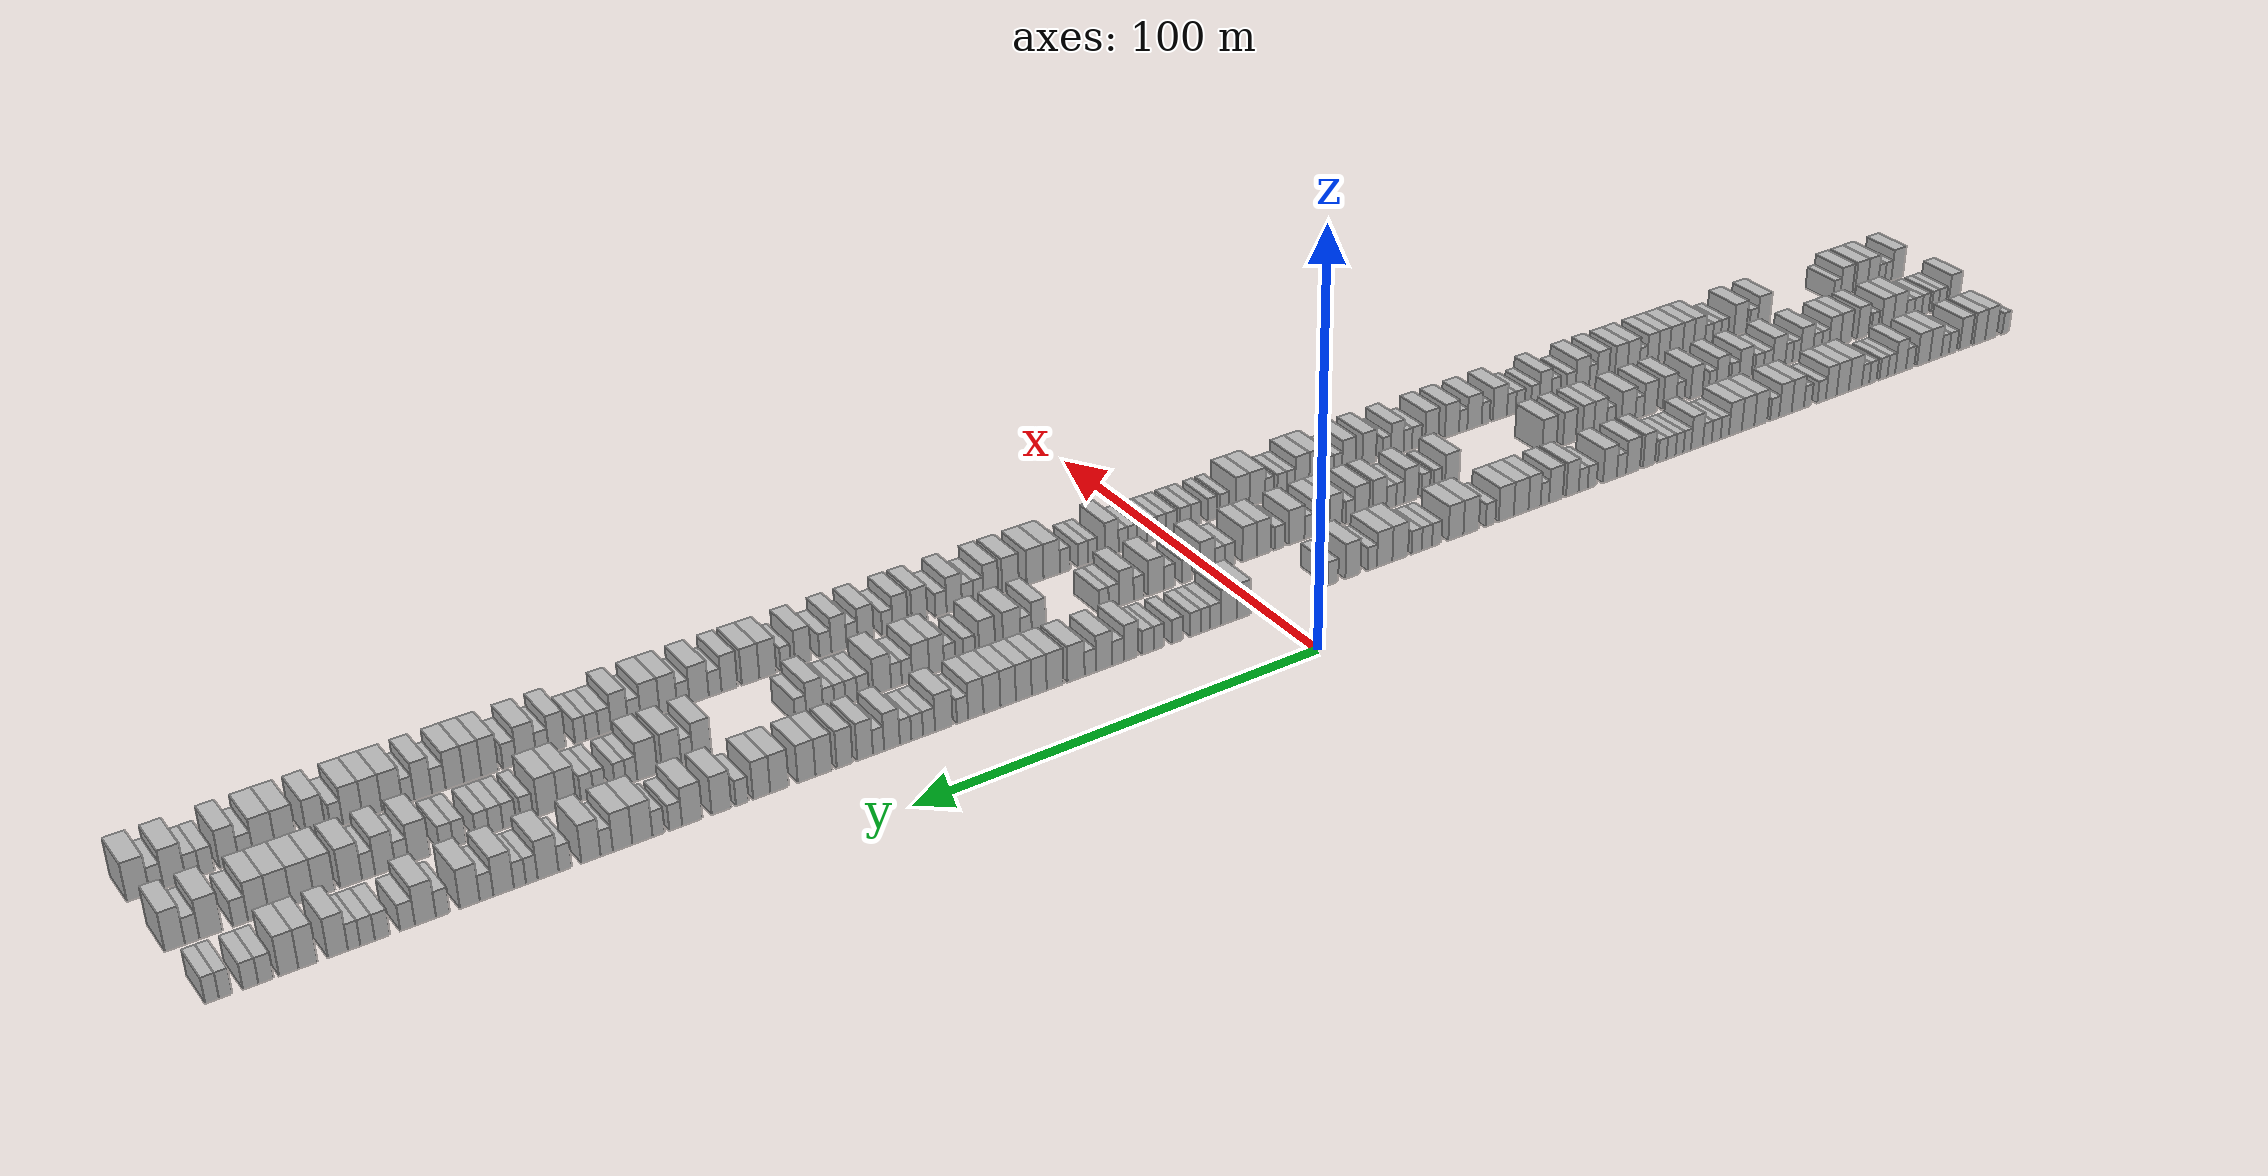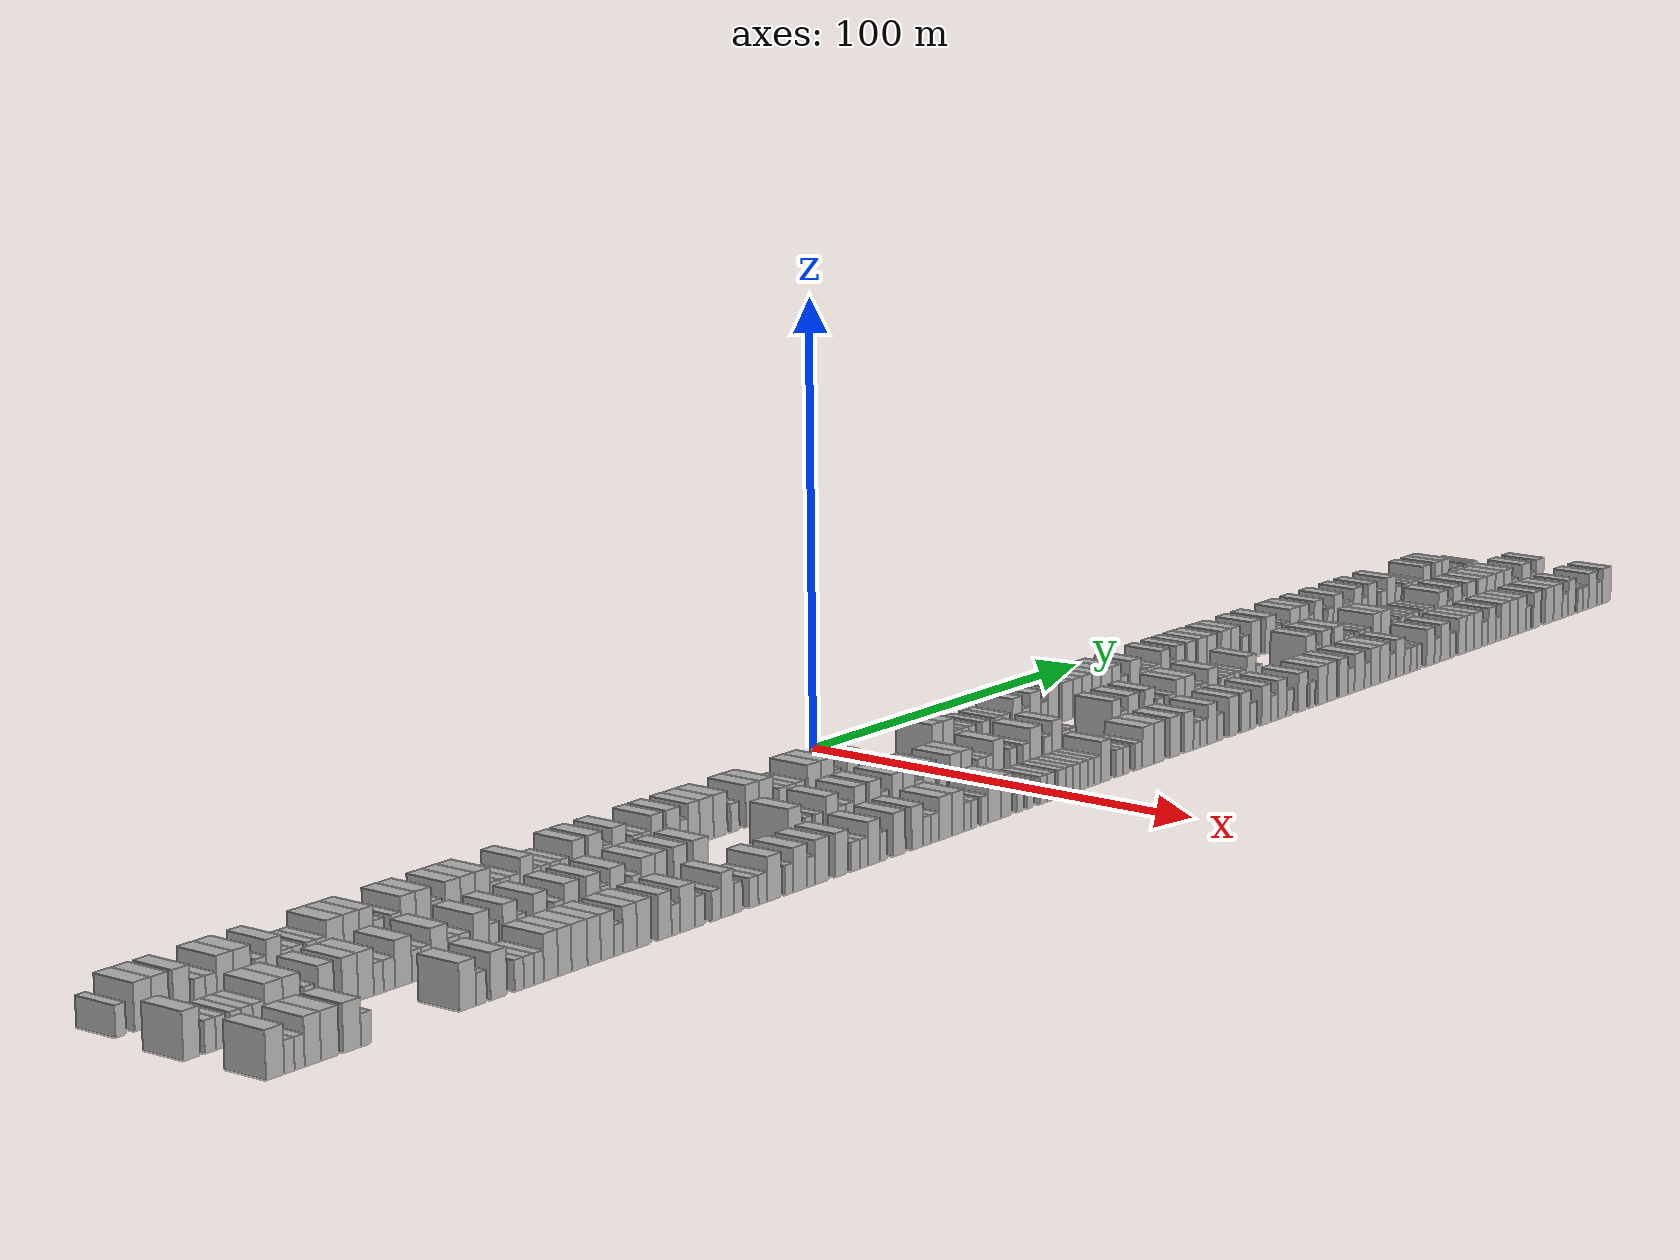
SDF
<sdf version="1.6">
 <world name="default">
  <scene>
   <sky><clouds><speed>12</speed></clouds></sky>
   <ambient>0.4 0.4 0.4 1</ambient>
   <background>0.7 0.7 0.7 1</background>
   <shadows>1</shadows>
  </scene>
  <gravity>0 0 -9.8066</gravity>
  <magnetic_field>6e-06 2.3e-05 -4.2e-05</magnetic_field>
  <physics default="0" name="default_physics" type="ode">
   <ode>
    <solver>
     <type>quick</type>
     <iters>10</iters>
     <sor>1.0</sor>
     <use_dynamic_moi_rescaling>0</use_dynamic_moi_rescaling>
    </solver>
    <constraints>
     <cfm>0</cfm>
     <erp>0.2</erp>
     <contact_max_correcting_vel>100</contact_max_correcting_vel>
     <contact_surface_layer>0.001</contact_surface_layer>
    </constraints>
   </ode>
   <max_step_size>0.004</max_step_size>
   <real_time_factor>1</real_time_factor>
   <real_time_update_rate>250</real_time_update_rate>
  </physics>
  <light name="sun" type="directional">
   <pose>0 0 10 0 0 0</pose>
   <diffuse>0.8 0.8 0.8 1</diffuse>
   <specular>0.2 0.2 0.2 1</specular>
   <attenuation>
    <range>1000</range>
    <constant>0.9</constant>
    <linear>0.01</linear>
    <quadratic>0.001</quadratic>
   </attenuation>
   <direction>-0.5 0.1 -0.9</direction>
  </light>
  <model name="building_1">
   <static>1</static>
   <pose>25.0000 -232.7464 0 0.000000 0.000000 0.000000</pose>
   <link name="link">
    <pose>0 0 3.00 0 0 0</pose>
    <collision name="collision"><geometry><box><size>10.0000 2.5072 6.0000</size></box></geometry></collision>
    <visual name="visual">
     <cast_shadows>0</cast_shadows>
     <geometry><box><size>10.0000 2.5072 6.0000</size></box></geometry>
     <material>
      <script>
       <uri>model://HANNAS_wall/materials/scripts</uri>
       <uri>model://HANNAS_wall/materials/textures</uri>
       <name>vrc/HANNAS_wall</name>
      </script>
     </material>
    </visual>
   </link>
  </model>
  <model name="building_2">
   <static>1</static>
   <pose>25.0000 -227.3734 0 0.000000 0.000000 0.000000</pose>
   <link name="link">
    <pose>0 0 4.50 0 0 0</pose>
    <collision name="collision"><geometry><box><size>10.0000 4.2387 9.0000</size></box></geometry></collision>
    <visual name="visual">
     <cast_shadows>0</cast_shadows>
     <geometry><box><size>10.0000 4.2387 9.0000</size></box></geometry>
     <material>
      <script>
       <uri>model://HANNAS_wall/materials/scripts</uri>
       <uri>model://HANNAS_wall/materials/textures</uri>
       <name>vrc/HANNAS_wall</name>
      </script>
     </material>
    </visual>
   </link>
  </model>
  <model name="building_3">
   <static>1</static>
   <pose>25.0000 -223.1973 0 0.000000 0.000000 0.000000</pose>
   <link name="link">
    <pose>0 0 4.50 0 0 0</pose>
    <collision name="collision"><geometry><box><size>10.0000 4.1135 9.0000</size></box></geometry></collision>
    <visual name="visual">
     <cast_shadows>0</cast_shadows>
     <geometry><box><size>10.0000 4.1135 9.0000</size></box></geometry>
     <material>
      <script>
       <uri>model://HANNAS_wall/materials/scripts</uri>
       <uri>model://HANNAS_wall/materials/textures</uri>
       <name>vrc/HANNAS_wall</name>
      </script>
     </material>
    </visual>
   </link>
  </model>
  <model name="building_4">
   <static>1</static>
   <pose>25.0000 -218.0938 0 0.000000 0.000000 0.000000</pose>
   <link name="link">
    <pose>0 0 4.50 0 0 0</pose>
    <collision name="collision"><geometry><box><size>10.0000 4.0936 9.0000</size></box></geometry></collision>
    <visual name="visual">
     <cast_shadows>0</cast_shadows>
     <geometry><box><size>10.0000 4.0936 9.0000</size></box></geometry>
     <material>
      <script>
       <uri>model://HANNAS_wall/materials/scripts</uri>
       <uri>model://HANNAS_wall/materials/textures</uri>
       <name>vrc/HANNAS_wall</name>
      </script>
     </material>
    </visual>
   </link>
  </model>
  <model name="building_5">
   <static>1</static>
   <pose>25.0000 -213.6600 0 0.000000 0.000000 0.000000</pose>
   <link name="link">
    <pose>0 0 3.00 0 0 0</pose>
    <collision name="collision"><geometry><box><size>10.0000 2.7739 6.0000</size></box></geometry></collision>
    <visual name="visual">
     <cast_shadows>0</cast_shadows>
     <geometry><box><size>10.0000 2.7739 6.0000</size></box></geometry>
     <material>
      <script>
       <uri>model://HANNAS_wall/materials/scripts</uri>
       <uri>model://HANNAS_wall/materials/textures</uri>
       <name>vrc/HANNAS_wall</name>
      </script>
     </material>
    </visual>
   </link>
  </model>
  <model name="building_6">
   <static>1</static>
   <pose>25.0000 -210.8924 0 0.000000 0.000000 0.000000</pose>
   <link name="link">
    <pose>0 0 3.00 0 0 0</pose>
    <collision name="collision"><geometry><box><size>10.0000 2.7613 6.0000</size></box></geometry></collision>
    <visual name="visual">
     <cast_shadows>0</cast_shadows>
     <geometry><box><size>10.0000 2.7613 6.0000</size></box></geometry>
     <material>
      <script>
       <uri>model://HANNAS_wall/materials/scripts</uri>
       <uri>model://HANNAS_wall/materials/textures</uri>
       <name>vrc/HANNAS_wall</name>
      </script>
     </material>
    </visual>
   </link>
  </model>
  <model name="building_7">
   <static>1</static>
   <pose>25.0000 -207.4235 0 0.000000 0.000000 0.000000</pose>
   <link name="link">
    <pose>0 0 4.50 0 0 0</pose>
    <collision name="collision"><geometry><box><size>10.0000 4.1765 9.0000</size></box></geometry></collision>
    <visual name="visual">
     <cast_shadows>0</cast_shadows>
     <geometry><box><size>10.0000 4.1765 9.0000</size></box></geometry>
     <material>
      <script>
       <uri>model://HANNAS_wall/materials/scripts</uri>
       <uri>model://HANNAS_wall/materials/textures</uri>
       <name>vrc/HANNAS_wall</name>
      </script>
     </material>
    </visual>
   </link>
  </model>
  <model name="building_8">
   <static>1</static>
   <pose>25.0000 -203.1562 0 0.000000 0.000000 0.000000</pose>
   <link name="link">
    <pose>0 0 4.50 0 0 0</pose>
    <collision name="collision"><geometry><box><size>10.0000 4.3580 9.0000</size></box></geometry></collision>
    <visual name="visual">
     <cast_shadows>0</cast_shadows>
     <geometry><box><size>10.0000 4.3580 9.0000</size></box></geometry>
     <material>
      <script>
       <uri>model://HANNAS_wall/materials/scripts</uri>
       <uri>model://HANNAS_wall/materials/textures</uri>
       <name>vrc/HANNAS_wall</name>
      </script>
     </material>
    </visual>
   </link>
  </model>
  <model name="building_9">
   <static>1</static>
   <pose>25.0000 -198.5310 0 0.000000 0.000000 0.000000</pose>
   <link name="link">
    <pose>0 0 3.00 0 0 0</pose>
    <collision name="collision"><geometry><box><size>10.0000 2.8926 6.0000</size></box></geometry></collision>
    <visual name="visual">
     <cast_shadows>0</cast_shadows>
     <geometry><box><size>10.0000 2.8926 6.0000</size></box></geometry>
     <material>
      <script>
       <uri>model://HANNAS_wall/materials/scripts</uri>
       <uri>model://HANNAS_wall/materials/textures</uri>
       <name>vrc/HANNAS_wall</name>
      </script>
     </material>
    </visual>
   </link>
  </model>
  <model name="building_10">
   <static>1</static>
   <pose>25.0000 -195.1847 0 0.000000 0.000000 0.000000</pose>
   <link name="link">
    <pose>0 0 4.50 0 0 0</pose>
    <collision name="collision"><geometry><box><size>10.0000 3.8000 9.0000</size></box></geometry></collision>
    <visual name="visual">
     <cast_shadows>0</cast_shadows>
     <geometry><box><size>10.0000 3.8000 9.0000</size></box></geometry>
     <material>
      <script>
       <uri>model://HANNAS_wall/materials/scripts</uri>
       <uri>model://HANNAS_wall/materials/textures</uri>
       <name>vrc/HANNAS_wall</name>
      </script>
     </material>
    </visual>
   </link>
  </model>
  <model name="building_11">
   <static>1</static>
   <pose>25.0000 -191.9634 0 0.000000 0.000000 0.000000</pose>
   <link name="link">
    <pose>0 0 3.00 0 0 0</pose>
    <collision name="collision"><geometry><box><size>10.0000 2.6426 6.0000</size></box></geometry></collision>
    <visual name="visual">
     <cast_shadows>0</cast_shadows>
     <geometry><box><size>10.0000 2.6426 6.0000</size></box></geometry>
     <material>
      <script>
       <uri>model://HANNAS_wall/materials/scripts</uri>
       <uri>model://HANNAS_wall/materials/textures</uri>
       <name>vrc/HANNAS_wall</name>
      </script>
     </material>
    </visual>
   </link>
  </model>
  <model name="building_12">
   <static>1</static>
   <pose>25.0000 -189.2580 0 0.000000 0.000000 0.000000</pose>
   <link name="link">
    <pose>0 0 3.00 0 0 0</pose>
    <collision name="collision"><geometry><box><size>10.0000 2.7681 6.0000</size></box></geometry></collision>
    <visual name="visual">
     <cast_shadows>0</cast_shadows>
     <geometry><box><size>10.0000 2.7681 6.0000</size></box></geometry>
     <material>
      <script>
       <uri>model://HANNAS_wall/materials/scripts</uri>
       <uri>model://HANNAS_wall/materials/textures</uri>
       <name>vrc/HANNAS_wall</name>
      </script>
     </material>
    </visual>
   </link>
  </model>
  <model name="building_13">
   <static>1</static>
   <pose>25.0000 -185.5941 0 0.000000 0.000000 0.000000</pose>
   <link name="link">
    <pose>0 0 3.00 0 0 0</pose>
    <collision name="collision"><geometry><box><size>10.0000 2.5597 6.0000</size></box></geometry></collision>
    <visual name="visual">
     <cast_shadows>0</cast_shadows>
     <geometry><box><size>10.0000 2.5597 6.0000</size></box></geometry>
     <material>
      <script>
       <uri>model://HANNAS_wall/materials/scripts</uri>
       <uri>model://HANNAS_wall/materials/textures</uri>
       <name>vrc/HANNAS_wall</name>
      </script>
     </material>
    </visual>
   </link>
  </model>
  <model name="building_14">
   <static>1</static>
   <pose>25.0000 -183.0411 0 0.000000 0.000000 0.000000</pose>
   <link name="link">
    <pose>0 0 3.00 0 0 0</pose>
    <collision name="collision"><geometry><box><size>10.0000 2.5462 6.0000</size></box></geometry></collision>
    <visual name="visual">
     <cast_shadows>0</cast_shadows>
     <geometry><box><size>10.0000 2.5462 6.0000</size></box></geometry>
     <material>
      <script>
       <uri>model://HANNAS_wall/materials/scripts</uri>
       <uri>model://HANNAS_wall/materials/textures</uri>
       <name>vrc/HANNAS_wall</name>
      </script>
     </material>
    </visual>
   </link>
  </model>
  <model name="building_15">
   <static>1</static>
   <pose>25.0000 -179.5298 0 0.000000 0.000000 0.000000</pose>
   <link name="link">
    <pose>0 0 4.50 0 0 0</pose>
    <collision name="collision"><geometry><box><size>10.0000 4.4765 9.0000</size></box></geometry></collision>
    <visual name="visual">
     <cast_shadows>0</cast_shadows>
     <geometry><box><size>10.0000 4.4765 9.0000</size></box></geometry>
     <material>
      <script>
       <uri>model://HANNAS_wall/materials/scripts</uri>
       <uri>model://HANNAS_wall/materials/textures</uri>
       <name>vrc/HANNAS_wall</name>
      </script>
     </material>
    </visual>
   </link>
  </model>
  <model name="building_16">
   <static>1</static>
   <pose>25.0000 -175.2244 0 0.000000 0.000000 0.000000</pose>
   <link name="link">
    <pose>0 0 4.50 0 0 0</pose>
    <collision name="collision"><geometry><box><size>10.0000 4.1342 9.0000</size></box></geometry></collision>
    <visual name="visual">
     <cast_shadows>0</cast_shadows>
     <geometry><box><size>10.0000 4.1342 9.0000</size></box></geometry>
     <material>
      <script>
       <uri>model://HANNAS_wall/materials/scripts</uri>
       <uri>model://HANNAS_wall/materials/textures</uri>
       <name>vrc/HANNAS_wall</name>
      </script>
     </material>
    </visual>
   </link>
  </model>
  <model name="building_17">
   <static>1</static>
   <pose>25.0000 -171.3254 0 0.000000 0.000000 0.000000</pose>
   <link name="link">
    <pose>0 0 4.50 0 0 0</pose>
    <collision name="collision"><geometry><box><size>10.0000 3.6637 9.0000</size></box></geometry></collision>
    <visual name="visual">
     <cast_shadows>0</cast_shadows>
     <geometry><box><size>10.0000 3.6637 9.0000</size></box></geometry>
     <material>
      <script>
       <uri>model://HANNAS_wall/materials/scripts</uri>
       <uri>model://HANNAS_wall/materials/textures</uri>
       <name>vrc/HANNAS_wall</name>
      </script>
     </material>
    </visual>
   </link>
  </model>
  <model name="building_18">
   <static>1</static>
   <pose>25.0000 -168.0835 0 0.000000 0.000000 0.000000</pose>
   <link name="link">
    <pose>0 0 3.00 0 0 0</pose>
    <collision name="collision"><geometry><box><size>10.0000 2.8201 6.0000</size></box></geometry></collision>
    <visual name="visual">
     <cast_shadows>0</cast_shadows>
     <geometry><box><size>10.0000 2.8201 6.0000</size></box></geometry>
     <material>
      <script>
       <uri>model://HANNAS_wall/materials/scripts</uri>
       <uri>model://HANNAS_wall/materials/textures</uri>
       <name>vrc/HANNAS_wall</name>
      </script>
     </material>
    </visual>
   </link>
  </model>
  <model name="building_19">
   <static>1</static>
   <pose>25.0000 -163.3988 0 0.000000 0.000000 0.000000</pose>
   <link name="link">
    <pose>0 0 3.00 0 0 0</pose>
    <collision name="collision"><geometry><box><size>10.0000 2.5493 6.0000</size></box></geometry></collision>
    <visual name="visual">
     <cast_shadows>0</cast_shadows>
     <geometry><box><size>10.0000 2.5493 6.0000</size></box></geometry>
     <material>
      <script>
       <uri>model://HANNAS_wall/materials/scripts</uri>
       <uri>model://HANNAS_wall/materials/textures</uri>
       <name>vrc/HANNAS_wall</name>
      </script>
     </material>
    </visual>
   </link>
  </model>
  <model name="building_20">
   <static>1</static>
   <pose>25.0000 -160.0751 0 0.000000 0.000000 0.000000</pose>
   <link name="link">
    <pose>0 0 4.50 0 0 0</pose>
    <collision name="collision"><geometry><box><size>10.0000 4.0981 9.0000</size></box></geometry></collision>
    <visual name="visual">
     <cast_shadows>0</cast_shadows>
     <geometry><box><size>10.0000 4.0981 9.0000</size></box></geometry>
     <material>
      <script>
       <uri>model://HANNAS_wall/materials/scripts</uri>
       <uri>model://HANNAS_wall/materials/textures</uri>
       <name>vrc/HANNAS_wall</name>
      </script>
     </material>
    </visual>
   </link>
  </model>
  <model name="building_21">
   <static>1</static>
   <pose>25.0000 -155.9558 0 0.000000 0.000000 0.000000</pose>
   <link name="link">
    <pose>0 0 4.50 0 0 0</pose>
    <collision name="collision"><geometry><box><size>10.0000 4.1404 9.0000</size></box></geometry></collision>
    <visual name="visual">
     <cast_shadows>0</cast_shadows>
     <geometry><box><size>10.0000 4.1404 9.0000</size></box></geometry>
     <material>
      <script>
       <uri>model://HANNAS_wall/materials/scripts</uri>
       <uri>model://HANNAS_wall/materials/textures</uri>
       <name>vrc/HANNAS_wall</name>
      </script>
     </material>
    </visual>
   </link>
  </model>
  <model name="building_22">
   <static>1</static>
   <pose>25.0000 -152.3985 0 0.000000 0.000000 0.000000</pose>
   <link name="link">
    <pose>0 0 3.00 0 0 0</pose>
    <collision name="collision"><geometry><box><size>10.0000 2.9743 6.0000</size></box></geometry></collision>
    <visual name="visual">
     <cast_shadows>0</cast_shadows>
     <geometry><box><size>10.0000 2.9743 6.0000</size></box></geometry>
     <material>
      <script>
       <uri>model://HANNAS_wall/materials/scripts</uri>
       <uri>model://HANNAS_wall/materials/textures</uri>
       <name>vrc/HANNAS_wall</name>
      </script>
     </material>
    </visual>
   </link>
  </model>
  <model name="building_23">
   <static>1</static>
   <pose>25.0000 -147.8059 0 0.000000 0.000000 0.000000</pose>
   <link name="link">
    <pose>0 0 4.50 0 0 0</pose>
    <collision name="collision"><geometry><box><size>10.0000 4.2109 9.0000</size></box></geometry></collision>
    <visual name="visual">
     <cast_shadows>0</cast_shadows>
     <geometry><box><size>10.0000 4.2109 9.0000</size></box></geometry>
     <material>
      <script>
       <uri>model://HANNAS_wall/materials/scripts</uri>
       <uri>model://HANNAS_wall/materials/textures</uri>
       <name>vrc/HANNAS_wall</name>
      </script>
     </material>
    </visual>
   </link>
  </model>
  <model name="building_24">
   <static>1</static>
   <pose>25.0000 -143.6487 0 0.000000 0.000000 0.000000</pose>
   <link name="link">
    <pose>0 0 4.50 0 0 0</pose>
    <collision name="collision"><geometry><box><size>10.0000 4.1034 9.0000</size></box></geometry></collision>
    <visual name="visual">
     <cast_shadows>0</cast_shadows>
     <geometry><box><size>10.0000 4.1034 9.0000</size></box></geometry>
     <material>
      <script>
       <uri>model://HANNAS_wall/materials/scripts</uri>
       <uri>model://HANNAS_wall/materials/textures</uri>
       <name>vrc/HANNAS_wall</name>
      </script>
     </material>
    </visual>
   </link>
  </model>
  <model name="building_25">
   <static>1</static>
   <pose>25.0000 -139.5028 0 0.000000 0.000000 0.000000</pose>
   <link name="link">
    <pose>0 0 4.50 0 0 0</pose>
    <collision name="collision"><geometry><box><size>10.0000 4.1885 9.0000</size></box></geometry></collision>
    <visual name="visual">
     <cast_shadows>0</cast_shadows>
     <geometry><box><size>10.0000 4.1885 9.0000</size></box></geometry>
     <material>
      <script>
       <uri>model://HANNAS_wall/materials/scripts</uri>
       <uri>model://HANNAS_wall/materials/textures</uri>
       <name>vrc/HANNAS_wall</name>
      </script>
     </material>
    </visual>
   </link>
  </model>
  <model name="building_26">
   <static>1</static>
   <pose>25.0000 -136.0570 0 0.000000 0.000000 0.000000</pose>
   <link name="link">
    <pose>0 0 3.00 0 0 0</pose>
    <collision name="collision"><geometry><box><size>10.0000 2.7031 6.0000</size></box></geometry></collision>
    <visual name="visual">
     <cast_shadows>0</cast_shadows>
     <geometry><box><size>10.0000 2.7031 6.0000</size></box></geometry>
     <material>
      <script>
       <uri>model://HANNAS_wall/materials/scripts</uri>
       <uri>model://HANNAS_wall/materials/textures</uri>
       <name>vrc/HANNAS_wall</name>
      </script>
     </material>
    </visual>
   </link>
  </model>
  <model name="building_27">
   <static>1</static>
   <pose>25.0000 -133.2723 0 0.000000 0.000000 0.000000</pose>
   <link name="link">
    <pose>0 0 3.00 0 0 0</pose>
    <collision name="collision"><geometry><box><size>10.0000 2.8663 6.0000</size></box></geometry></collision>
    <visual name="visual">
     <cast_shadows>0</cast_shadows>
     <geometry><box><size>10.0000 2.8663 6.0000</size></box></geometry>
     <material>
      <script>
       <uri>model://HANNAS_wall/materials/scripts</uri>
       <uri>model://HANNAS_wall/materials/textures</uri>
       <name>vrc/HANNAS_wall</name>
      </script>
     </material>
    </visual>
   </link>
  </model>
  <model name="building_28">
   <static>1</static>
   <pose>25.0000 -130.4204 0 0.000000 0.000000 0.000000</pose>
   <link name="link">
    <pose>0 0 3.00 0 0 0</pose>
    <collision name="collision"><geometry><box><size>10.0000 2.8375 6.0000</size></box></geometry></collision>
    <visual name="visual">
     <cast_shadows>0</cast_shadows>
     <geometry><box><size>10.0000 2.8375 6.0000</size></box></geometry>
     <material>
      <script>
       <uri>model://HANNAS_wall/materials/scripts</uri>
       <uri>model://HANNAS_wall/materials/textures</uri>
       <name>vrc/HANNAS_wall</name>
      </script>
     </material>
    </visual>
   </link>
  </model>
  <model name="building_29">
   <static>1</static>
   <pose>25.0000 -127.1035 0 0.000000 0.000000 0.000000</pose>
   <link name="link">
    <pose>0 0 4.50 0 0 0</pose>
    <collision name="collision"><geometry><box><size>10.0000 3.7964 9.0000</size></box></geometry></collision>
    <visual name="visual">
     <cast_shadows>0</cast_shadows>
     <geometry><box><size>10.0000 3.7964 9.0000</size></box></geometry>
     <material>
      <script>
       <uri>model://HANNAS_wall/materials/scripts</uri>
       <uri>model://HANNAS_wall/materials/textures</uri>
       <name>vrc/HANNAS_wall</name>
      </script>
     </material>
    </visual>
   </link>
  </model>
  <model name="building_30">
   <static>1</static>
   <pose>25.0000 -123.9987 0 0.000000 0.000000 0.000000</pose>
   <link name="link">
    <pose>0 0 3.00 0 0 0</pose>
    <collision name="collision"><geometry><box><size>10.0000 2.4132 6.0000</size></box></geometry></collision>
    <visual name="visual">
     <cast_shadows>0</cast_shadows>
     <geometry><box><size>10.0000 2.4132 6.0000</size></box></geometry>
     <material>
      <script>
       <uri>model://HANNAS_wall/materials/scripts</uri>
       <uri>model://HANNAS_wall/materials/textures</uri>
       <name>vrc/HANNAS_wall</name>
      </script>
     </material>
    </visual>
   </link>
  </model>
  <model name="building_31">
   <static>1</static>
   <pose>25.0000 -121.5376 0 0.000000 0.000000 0.000000</pose>
   <link name="link">
    <pose>0 0 3.00 0 0 0</pose>
    <collision name="collision"><geometry><box><size>10.0000 2.5090 6.0000</size></box></geometry></collision>
    <visual name="visual">
     <cast_shadows>0</cast_shadows>
     <geometry><box><size>10.0000 2.5090 6.0000</size></box></geometry>
     <material>
      <script>
       <uri>model://HANNAS_wall/materials/scripts</uri>
       <uri>model://HANNAS_wall/materials/textures</uri>
       <name>vrc/HANNAS_wall</name>
      </script>
     </material>
    </visual>
   </link>
  </model>
  <model name="building_32">
   <static>1</static>
   <pose>25.0000 -118.8527 0 0.000000 0.000000 0.000000</pose>
   <link name="link">
    <pose>0 0 3.00 0 0 0</pose>
    <collision name="collision"><geometry><box><size>10.0000 2.8610 6.0000</size></box></geometry></collision>
    <visual name="visual">
     <cast_shadows>0</cast_shadows>
     <geometry><box><size>10.0000 2.8610 6.0000</size></box></geometry>
     <material>
      <script>
       <uri>model://HANNAS_wall/materials/scripts</uri>
       <uri>model://HANNAS_wall/materials/textures</uri>
       <name>vrc/HANNAS_wall</name>
      </script>
     </material>
    </visual>
   </link>
  </model>
  <model name="building_33">
   <static>1</static>
   <pose>25.0000 -116.0911 0 0.000000 0.000000 0.000000</pose>
   <link name="link">
    <pose>0 0 3.00 0 0 0</pose>
    <collision name="collision"><geometry><box><size>10.0000 2.6621 6.0000</size></box></geometry></collision>
    <visual name="visual">
     <cast_shadows>0</cast_shadows>
     <geometry><box><size>10.0000 2.6621 6.0000</size></box></geometry>
     <material>
      <script>
       <uri>model://HANNAS_wall/materials/scripts</uri>
       <uri>model://HANNAS_wall/materials/textures</uri>
       <name>vrc/HANNAS_wall</name>
      </script>
     </material>
    </visual>
   </link>
  </model>
  <model name="building_34">
   <static>1</static>
   <pose>25.0000 -111.9034 0 0.000000 0.000000 0.000000</pose>
   <link name="link">
    <pose>0 0 4.50 0 0 0</pose>
    <collision name="collision"><geometry><box><size>10.0000 3.7135 9.0000</size></box></geometry></collision>
    <visual name="visual">
     <cast_shadows>0</cast_shadows>
     <geometry><box><size>10.0000 3.7135 9.0000</size></box></geometry>
     <material>
      <script>
       <uri>model://HANNAS_wall/materials/scripts</uri>
       <uri>model://HANNAS_wall/materials/textures</uri>
       <name>vrc/HANNAS_wall</name>
      </script>
     </material>
    </visual>
   </link>
  </model>
  <model name="building_35">
   <static>1</static>
   <pose>25.0000 -106.9085 0 0.000000 0.000000 0.000000</pose>
   <link name="link">
    <pose>0 0 4.50 0 0 0</pose>
    <collision name="collision"><geometry><box><size>10.0000 4.2762 9.0000</size></box></geometry></collision>
    <visual name="visual">
     <cast_shadows>0</cast_shadows>
     <geometry><box><size>10.0000 4.2762 9.0000</size></box></geometry>
     <material>
      <script>
       <uri>model://HANNAS_wall/materials/scripts</uri>
       <uri>model://HANNAS_wall/materials/textures</uri>
       <name>vrc/HANNAS_wall</name>
      </script>
     </material>
    </visual>
   </link>
  </model>
  <model name="building_36">
   <static>1</static>
   <pose>25.0000 -103.3278 0 0.000000 0.000000 0.000000</pose>
   <link name="link">
    <pose>0 0 3.00 0 0 0</pose>
    <collision name="collision"><geometry><box><size>10.0000 2.8852 6.0000</size></box></geometry></collision>
    <visual name="visual">
     <cast_shadows>0</cast_shadows>
     <geometry><box><size>10.0000 2.8852 6.0000</size></box></geometry>
     <material>
      <script>
       <uri>model://HANNAS_wall/materials/scripts</uri>
       <uri>model://HANNAS_wall/materials/textures</uri>
       <name>vrc/HANNAS_wall</name>
      </script>
     </material>
    </visual>
   </link>
  </model>
  <model name="building_37">
   <static>1</static>
   <pose>25.0000 -99.7571 0 0.000000 0.000000 0.000000</pose>
   <link name="link">
    <pose>0 0 4.50 0 0 0</pose>
    <collision name="collision"><geometry><box><size>10.0000 4.2564 9.0000</size></box></geometry></collision>
    <visual name="visual">
     <cast_shadows>0</cast_shadows>
     <geometry><box><size>10.0000 4.2564 9.0000</size></box></geometry>
     <material>
      <script>
       <uri>model://HANNAS_wall/materials/scripts</uri>
       <uri>model://HANNAS_wall/materials/textures</uri>
       <name>vrc/HANNAS_wall</name>
      </script>
     </material>
    </visual>
   </link>
  </model>
  <model name="building_38">
   <static>1</static>
   <pose>25.0000 -94.2569 0 0.000000 0.000000 0.000000</pose>
   <link name="link">
    <pose>0 0 3.00 0 0 0</pose>
    <collision name="collision"><geometry><box><size>10.0000 2.7440 6.0000</size></box></geometry></collision>
    <visual name="visual">
     <cast_shadows>0</cast_shadows>
     <geometry><box><size>10.0000 2.7440 6.0000</size></box></geometry>
     <material>
      <script>
       <uri>model://HANNAS_wall/materials/scripts</uri>
       <uri>model://HANNAS_wall/materials/textures</uri>
       <name>vrc/HANNAS_wall</name>
      </script>
     </material>
    </visual>
   </link>
  </model>
  <model name="building_39">
   <static>1</static>
   <pose>25.0000 -91.5107 0 0.000000 0.000000 0.000000</pose>
   <link name="link">
    <pose>0 0 3.00 0 0 0</pose>
    <collision name="collision"><geometry><box><size>10.0000 2.7484 6.0000</size></box></geometry></collision>
    <visual name="visual">
     <cast_shadows>0</cast_shadows>
     <geometry><box><size>10.0000 2.7484 6.0000</size></box></geometry>
     <material>
      <script>
       <uri>model://HANNAS_wall/materials/scripts</uri>
       <uri>model://HANNAS_wall/materials/textures</uri>
       <name>vrc/HANNAS_wall</name>
      </script>
     </material>
    </visual>
   </link>
  </model>
  <model name="building_40">
   <static>1</static>
   <pose>25.0000 -88.2342 0 0.000000 0.000000 0.000000</pose>
   <link name="link">
    <pose>0 0 4.50 0 0 0</pose>
    <collision name="collision"><geometry><box><size>10.0000 3.8046 9.0000</size></box></geometry></collision>
    <visual name="visual">
     <cast_shadows>0</cast_shadows>
     <geometry><box><size>10.0000 3.8046 9.0000</size></box></geometry>
     <material>
      <script>
       <uri>model://HANNAS_wall/materials/scripts</uri>
       <uri>model://HANNAS_wall/materials/textures</uri>
       <name>vrc/HANNAS_wall</name>
      </script>
     </material>
    </visual>
   </link>
  </model>
  <model name="building_41">
   <static>1</static>
   <pose>25.0000 -83.2466 0 0.000000 0.000000 0.000000</pose>
   <link name="link">
    <pose>0 0 4.50 0 0 0</pose>
    <collision name="collision"><geometry><box><size>10.0000 4.1706 9.0000</size></box></geometry></collision>
    <visual name="visual">
     <cast_shadows>0</cast_shadows>
     <geometry><box><size>10.0000 4.1706 9.0000</size></box></geometry>
     <material>
      <script>
       <uri>model://HANNAS_wall/materials/scripts</uri>
       <uri>model://HANNAS_wall/materials/textures</uri>
       <name>vrc/HANNAS_wall</name>
      </script>
     </material>
    </visual>
   </link>
  </model>
  <model name="building_42">
   <static>1</static>
   <pose>25.0000 -79.9005 0 0.000000 0.000000 0.000000</pose>
   <link name="link">
    <pose>0 0 3.00 0 0 0</pose>
    <collision name="collision"><geometry><box><size>10.0000 2.5216 6.0000</size></box></geometry></collision>
    <visual name="visual">
     <cast_shadows>0</cast_shadows>
     <geometry><box><size>10.0000 2.5216 6.0000</size></box></geometry>
     <material>
      <script>
       <uri>model://HANNAS_wall/materials/scripts</uri>
       <uri>model://HANNAS_wall/materials/textures</uri>
       <name>vrc/HANNAS_wall</name>
      </script>
     </material>
    </visual>
   </link>
  </model>
  <model name="building_43">
   <static>1</static>
   <pose>25.0000 -76.8281 0 0.000000 0.000000 0.000000</pose>
   <link name="link">
    <pose>0 0 4.50 0 0 0</pose>
    <collision name="collision"><geometry><box><size>10.0000 3.6231 9.0000</size></box></geometry></collision>
    <visual name="visual">
     <cast_shadows>0</cast_shadows>
     <geometry><box><size>10.0000 3.6231 9.0000</size></box></geometry>
     <material>
      <script>
       <uri>model://HANNAS_wall/materials/scripts</uri>
       <uri>model://HANNAS_wall/materials/textures</uri>
       <name>vrc/HANNAS_wall</name>
      </script>
     </material>
    </visual>
   </link>
  </model>
  <model name="building_44">
   <static>1</static>
   <pose>25.0000 -72.8285 0 0.000000 0.000000 0.000000</pose>
   <link name="link">
    <pose>0 0 4.50 0 0 0</pose>
    <collision name="collision"><geometry><box><size>10.0000 4.3761 9.0000</size></box></geometry></collision>
    <visual name="visual">
     <cast_shadows>0</cast_shadows>
     <geometry><box><size>10.0000 4.3761 9.0000</size></box></geometry>
     <material>
      <script>
       <uri>model://HANNAS_wall/materials/scripts</uri>
       <uri>model://HANNAS_wall/materials/textures</uri>
       <name>vrc/HANNAS_wall</name>
      </script>
     </material>
    </visual>
   </link>
  </model>
  <model name="building_45">
   <static>1</static>
   <pose>25.0000 -68.4169 0 0.000000 0.000000 0.000000</pose>
   <link name="link">
    <pose>0 0 4.50 0 0 0</pose>
    <collision name="collision"><geometry><box><size>10.0000 4.4471 9.0000</size></box></geometry></collision>
    <visual name="visual">
     <cast_shadows>0</cast_shadows>
     <geometry><box><size>10.0000 4.4471 9.0000</size></box></geometry>
     <material>
      <script>
       <uri>model://HANNAS_wall/materials/scripts</uri>
       <uri>model://HANNAS_wall/materials/textures</uri>
       <name>vrc/HANNAS_wall</name>
      </script>
     </material>
    </visual>
   </link>
  </model>
  <model name="building_46">
   <static>1</static>
   <pose>25.0000 -63.7694 0 0.000000 0.000000 0.000000</pose>
   <link name="link">
    <pose>0 0 3.00 0 0 0</pose>
    <collision name="collision"><geometry><box><size>10.0000 2.8479 6.0000</size></box></geometry></collision>
    <visual name="visual">
     <cast_shadows>0</cast_shadows>
     <geometry><box><size>10.0000 2.8479 6.0000</size></box></geometry>
     <material>
      <script>
       <uri>model://HANNAS_wall/materials/scripts</uri>
       <uri>model://HANNAS_wall/materials/textures</uri>
       <name>vrc/HANNAS_wall</name>
      </script>
     </material>
    </visual>
   </link>
  </model>
  <model name="building_47">
   <static>1</static>
   <pose>25.0000 -58.0968 0 0.000000 0.000000 0.000000</pose>
   <link name="link">
    <pose>0 0 4.50 0 0 0</pose>
    <collision name="collision"><geometry><box><size>10.0000 4.4973 9.0000</size></box></geometry></collision>
    <visual name="visual">
     <cast_shadows>0</cast_shadows>
     <geometry><box><size>10.0000 4.4973 9.0000</size></box></geometry>
     <material>
      <script>
       <uri>model://HANNAS_wall/materials/scripts</uri>
       <uri>model://HANNAS_wall/materials/textures</uri>
       <name>vrc/HANNAS_wall</name>
      </script>
     </material>
    </visual>
   </link>
  </model>
  <model name="building_48">
   <static>1</static>
   <pose>25.0000 -53.6677 0 0.000000 0.000000 0.000000</pose>
   <link name="link">
    <pose>0 0 4.50 0 0 0</pose>
    <collision name="collision"><geometry><box><size>10.0000 4.3608 9.0000</size></box></geometry></collision>
    <visual name="visual">
     <cast_shadows>0</cast_shadows>
     <geometry><box><size>10.0000 4.3608 9.0000</size></box></geometry>
     <material>
      <script>
       <uri>model://HANNAS_wall/materials/scripts</uri>
       <uri>model://HANNAS_wall/materials/textures</uri>
       <name>vrc/HANNAS_wall</name>
      </script>
     </material>
    </visual>
   </link>
  </model>
  <model name="building_49">
   <static>1</static>
   <pose>25.0000 -48.1346 0 0.000000 0.000000 0.000000</pose>
   <link name="link">
    <pose>0 0 3.00 0 0 0</pose>
    <collision name="collision"><geometry><box><size>10.0000 2.7054 6.0000</size></box></geometry></collision>
    <visual name="visual">
     <cast_shadows>0</cast_shadows>
     <geometry><box><size>10.0000 2.7054 6.0000</size></box></geometry>
     <material>
      <script>
       <uri>model://HANNAS_wall/materials/scripts</uri>
       <uri>model://HANNAS_wall/materials/textures</uri>
       <name>vrc/HANNAS_wall</name>
      </script>
     </material>
    </visual>
   </link>
  </model>
  <model name="building_50">
   <static>1</static>
   <pose>25.0000 -45.3167 0 0.000000 0.000000 0.000000</pose>
   <link name="link">
    <pose>0 0 3.00 0 0 0</pose>
    <collision name="collision"><geometry><box><size>10.0000 2.9302 6.0000</size></box></geometry></collision>
    <visual name="visual">
     <cast_shadows>0</cast_shadows>
     <geometry><box><size>10.0000 2.9302 6.0000</size></box></geometry>
     <material>
      <script>
       <uri>model://HANNAS_wall/materials/scripts</uri>
       <uri>model://HANNAS_wall/materials/textures</uri>
       <name>vrc/HANNAS_wall</name>
      </script>
     </material>
    </visual>
   </link>
  </model>
  <model name="building_51">
   <static>1</static>
   <pose>25.0000 -42.3913 0 0.000000 0.000000 0.000000</pose>
   <link name="link">
    <pose>0 0 3.00 0 0 0</pose>
    <collision name="collision"><geometry><box><size>10.0000 2.9207 6.0000</size></box></geometry></collision>
    <visual name="visual">
     <cast_shadows>0</cast_shadows>
     <geometry><box><size>10.0000 2.9207 6.0000</size></box></geometry>
     <material>
      <script>
       <uri>model://HANNAS_wall/materials/scripts</uri>
       <uri>model://HANNAS_wall/materials/textures</uri>
       <name>vrc/HANNAS_wall</name>
      </script>
     </material>
    </visual>
   </link>
  </model>
  <model name="building_52">
   <static>1</static>
   <pose>25.0000 -37.7059 0 0.000000 0.000000 0.000000</pose>
   <link name="link">
    <pose>0 0 4.50 0 0 0</pose>
    <collision name="collision"><geometry><box><size>10.0000 4.4499 9.0000</size></box></geometry></collision>
    <visual name="visual">
     <cast_shadows>0</cast_shadows>
     <geometry><box><size>10.0000 4.4499 9.0000</size></box></geometry>
     <material>
      <script>
       <uri>model://HANNAS_wall/materials/scripts</uri>
       <uri>model://HANNAS_wall/materials/textures</uri>
       <name>vrc/HANNAS_wall</name>
      </script>
     </material>
    </visual>
   </link>
  </model>
  <model name="building_53">
   <static>1</static>
   <pose>25.0000 -33.2970 0 0.000000 0.000000 0.000000</pose>
   <link name="link">
    <pose>0 0 4.50 0 0 0</pose>
    <collision name="collision"><geometry><box><size>10.0000 4.3680 9.0000</size></box></geometry></collision>
    <visual name="visual">
     <cast_shadows>0</cast_shadows>
     <geometry><box><size>10.0000 4.3680 9.0000</size></box></geometry>
     <material>
      <script>
       <uri>model://HANNAS_wall/materials/scripts</uri>
       <uri>model://HANNAS_wall/materials/textures</uri>
       <name>vrc/HANNAS_wall</name>
      </script>
     </material>
    </visual>
   </link>
  </model>
  <model name="building_54">
   <static>1</static>
   <pose>25.0000 -29.8048 0 0.000000 0.000000 0.000000</pose>
   <link name="link">
    <pose>0 0 3.00 0 0 0</pose>
    <collision name="collision"><geometry><box><size>10.0000 2.6163 6.0000</size></box></geometry></collision>
    <visual name="visual">
     <cast_shadows>0</cast_shadows>
     <geometry><box><size>10.0000 2.6163 6.0000</size></box></geometry>
     <material>
      <script>
       <uri>model://HANNAS_wall/materials/scripts</uri>
       <uri>model://HANNAS_wall/materials/textures</uri>
       <name>vrc/HANNAS_wall</name>
      </script>
     </material>
    </visual>
   </link>
  </model>
  <model name="building_55">
   <static>1</static>
   <pose>25.0000 -24.4021 0 0.000000 0.000000 0.000000</pose>
   <link name="link">
    <pose>0 0 4.50 0 0 0</pose>
    <collision name="collision"><geometry><box><size>10.0000 4.1892 9.0000</size></box></geometry></collision>
    <visual name="visual">
     <cast_shadows>0</cast_shadows>
     <geometry><box><size>10.0000 4.1892 9.0000</size></box></geometry>
     <material>
      <script>
       <uri>model://HANNAS_wall/materials/scripts</uri>
       <uri>model://HANNAS_wall/materials/textures</uri>
       <name>vrc/HANNAS_wall</name>
      </script>
     </material>
    </visual>
   </link>
  </model>
  <model name="building_56">
   <static>1</static>
   <pose>25.0000 -18.8573 0 0.000000 0.000000 0.000000</pose>
   <link name="link">
    <pose>0 0 3.00 0 0 0</pose>
    <collision name="collision"><geometry><box><size>10.0000 2.9004 6.0000</size></box></geometry></collision>
    <visual name="visual">
     <cast_shadows>0</cast_shadows>
     <geometry><box><size>10.0000 2.9004 6.0000</size></box></geometry>
     <material>
      <script>
       <uri>model://HANNAS_wall/materials/scripts</uri>
       <uri>model://HANNAS_wall/materials/textures</uri>
       <name>vrc/HANNAS_wall</name>
      </script>
     </material>
    </visual>
   </link>
  </model>
  <model name="building_57">
   <static>1</static>
   <pose>25.0000 5.3431 0 0.000000 0.000000 0.000000</pose>
   <link name="link">
    <pose>0 0 4.50 0 0 0</pose>
    <collision name="collision"><geometry><box><size>10.0000 3.8335 9.0000</size></box></geometry></collision>
    <visual name="visual">
     <cast_shadows>0</cast_shadows>
     <geometry><box><size>10.0000 3.8335 9.0000</size></box></geometry>
     <material>
      <script>
       <uri>model://HANNAS_wall/materials/scripts</uri>
       <uri>model://HANNAS_wall/materials/textures</uri>
       <name>vrc/HANNAS_wall</name>
      </script>
     </material>
    </visual>
   </link>
  </model>
  <model name="building_58">
   <static>1</static>
   <pose>25.0000 9.3319 0 0.000000 0.000000 0.000000</pose>
   <link name="link">
    <pose>0 0 4.50 0 0 0</pose>
    <collision name="collision"><geometry><box><size>10.0000 4.1440 9.0000</size></box></geometry></collision>
    <visual name="visual">
     <cast_shadows>0</cast_shadows>
     <geometry><box><size>10.0000 4.1440 9.0000</size></box></geometry>
     <material>
      <script>
       <uri>model://HANNAS_wall/materials/scripts</uri>
       <uri>model://HANNAS_wall/materials/textures</uri>
       <name>vrc/HANNAS_wall</name>
      </script>
     </material>
    </visual>
   </link>
  </model>
  <model name="building_59">
   <static>1</static>
   <pose>25.0000 12.8357 0 0.000000 0.000000 0.000000</pose>
   <link name="link">
    <pose>0 0 3.00 0 0 0</pose>
    <collision name="collision"><geometry><box><size>10.0000 2.8636 6.0000</size></box></geometry></collision>
    <visual name="visual">
     <cast_shadows>0</cast_shadows>
     <geometry><box><size>10.0000 2.8636 6.0000</size></box></geometry>
     <material>
      <script>
       <uri>model://HANNAS_wall/materials/scripts</uri>
       <uri>model://HANNAS_wall/materials/textures</uri>
       <name>vrc/HANNAS_wall</name>
      </script>
     </material>
    </visual>
   </link>
  </model>
  <model name="building_60">
   <static>1</static>
   <pose>25.0000 15.4938 0 0.000000 0.000000 0.000000</pose>
   <link name="link">
    <pose>0 0 3.00 0 0 0</pose>
    <collision name="collision"><geometry><box><size>10.0000 2.4527 6.0000</size></box></geometry></collision>
    <visual name="visual">
     <cast_shadows>0</cast_shadows>
     <geometry><box><size>10.0000 2.4527 6.0000</size></box></geometry>
     <material>
      <script>
       <uri>model://HANNAS_wall/materials/scripts</uri>
       <uri>model://HANNAS_wall/materials/textures</uri>
       <name>vrc/HANNAS_wall</name>
      </script>
     </material>
    </visual>
   </link>
  </model>
  <model name="building_61">
   <static>1</static>
   <pose>25.0000 18.0873 0 0.000000 0.000000 0.000000</pose>
   <link name="link">
    <pose>0 0 3.00 0 0 0</pose>
    <collision name="collision"><geometry><box><size>10.0000 2.7342 6.0000</size></box></geometry></collision>
    <visual name="visual">
     <cast_shadows>0</cast_shadows>
     <geometry><box><size>10.0000 2.7342 6.0000</size></box></geometry>
     <material>
      <script>
       <uri>model://HANNAS_wall/materials/scripts</uri>
       <uri>model://HANNAS_wall/materials/textures</uri>
       <name>vrc/HANNAS_wall</name>
      </script>
     </material>
    </visual>
   </link>
  </model>
  <model name="building_62">
   <static>1</static>
   <pose>25.0000 22.8977 0 0.000000 0.000000 0.000000</pose>
   <link name="link">
    <pose>0 0 3.00 0 0 0</pose>
    <collision name="collision"><geometry><box><size>10.0000 2.8866 6.0000</size></box></geometry></collision>
    <visual name="visual">
     <cast_shadows>0</cast_shadows>
     <geometry><box><size>10.0000 2.8866 6.0000</size></box></geometry>
     <material>
      <script>
       <uri>model://HANNAS_wall/materials/scripts</uri>
       <uri>model://HANNAS_wall/materials/textures</uri>
       <name>vrc/HANNAS_wall</name>
      </script>
     </material>
    </visual>
   </link>
  </model>
  <model name="building_63">
   <static>1</static>
   <pose>25.0000 27.6542 0 0.000000 0.000000 0.000000</pose>
   <link name="link">
    <pose>0 0 3.00 0 0 0</pose>
    <collision name="collision"><geometry><box><size>10.0000 2.6263 6.0000</size></box></geometry></collision>
    <visual name="visual">
     <cast_shadows>0</cast_shadows>
     <geometry><box><size>10.0000 2.6263 6.0000</size></box></geometry>
     <material>
      <script>
       <uri>model://HANNAS_wall/materials/scripts</uri>
       <uri>model://HANNAS_wall/materials/textures</uri>
       <name>vrc/HANNAS_wall</name>
      </script>
     </material>
    </visual>
   </link>
  </model>
  <model name="building_64">
   <static>1</static>
   <pose>25.0000 30.4473 0 0.000000 0.000000 0.000000</pose>
   <link name="link">
    <pose>0 0 3.00 0 0 0</pose>
    <collision name="collision"><geometry><box><size>10.0000 2.9599 6.0000</size></box></geometry></collision>
    <visual name="visual">
     <cast_shadows>0</cast_shadows>
     <geometry><box><size>10.0000 2.9599 6.0000</size></box></geometry>
     <material>
      <script>
       <uri>model://HANNAS_wall/materials/scripts</uri>
       <uri>model://HANNAS_wall/materials/textures</uri>
       <name>vrc/HANNAS_wall</name>
      </script>
     </material>
    </visual>
   </link>
  </model>
  <model name="building_65">
   <static>1</static>
   <pose>25.0000 34.7578 0 0.000000 0.000000 0.000000</pose>
   <link name="link">
    <pose>0 0 4.50 0 0 0</pose>
    <collision name="collision"><geometry><box><size>10.0000 3.6612 9.0000</size></box></geometry></collision>
    <visual name="visual">
     <cast_shadows>0</cast_shadows>
     <geometry><box><size>10.0000 3.6612 9.0000</size></box></geometry>
     <material>
      <script>
       <uri>model://HANNAS_wall/materials/scripts</uri>
       <uri>model://HANNAS_wall/materials/textures</uri>
       <name>vrc/HANNAS_wall</name>
      </script>
     </material>
    </visual>
   </link>
  </model>
  <model name="building_66">
   <static>1</static>
   <pose>25.0000 38.0858 0 0.000000 0.000000 0.000000</pose>
   <link name="link">
    <pose>0 0 3.00 0 0 0</pose>
    <collision name="collision"><geometry><box><size>10.0000 2.9948 6.0000</size></box></geometry></collision>
    <visual name="visual">
     <cast_shadows>0</cast_shadows>
     <geometry><box><size>10.0000 2.9948 6.0000</size></box></geometry>
     <material>
      <script>
       <uri>model://HANNAS_wall/materials/scripts</uri>
       <uri>model://HANNAS_wall/materials/textures</uri>
       <name>vrc/HANNAS_wall</name>
      </script>
     </material>
    </visual>
   </link>
  </model>
  <model name="building_67">
   <static>1</static>
   <pose>25.0000 41.6446 0 0.000000 0.000000 0.000000</pose>
   <link name="link">
    <pose>0 0 4.50 0 0 0</pose>
    <collision name="collision"><geometry><box><size>10.0000 4.1228 9.0000</size></box></geometry></collision>
    <visual name="visual">
     <cast_shadows>0</cast_shadows>
     <geometry><box><size>10.0000 4.1228 9.0000</size></box></geometry>
     <material>
      <script>
       <uri>model://HANNAS_wall/materials/scripts</uri>
       <uri>model://HANNAS_wall/materials/textures</uri>
       <name>vrc/HANNAS_wall</name>
      </script>
     </material>
    </visual>
   </link>
  </model>
  <model name="building_68">
   <static>1</static>
   <pose>25.0000 45.1408 0 0.000000 0.000000 0.000000</pose>
   <link name="link">
    <pose>0 0 3.00 0 0 0</pose>
    <collision name="collision"><geometry><box><size>10.0000 2.8695 6.0000</size></box></geometry></collision>
    <visual name="visual">
     <cast_shadows>0</cast_shadows>
     <geometry><box><size>10.0000 2.8695 6.0000</size></box></geometry>
     <material>
      <script>
       <uri>model://HANNAS_wall/materials/scripts</uri>
       <uri>model://HANNAS_wall/materials/textures</uri>
       <name>vrc/HANNAS_wall</name>
      </script>
     </material>
    </visual>
   </link>
  </model>
  <model name="building_69">
   <static>1</static>
   <pose>25.0000 48.7208 0 0.000000 0.000000 0.000000</pose>
   <link name="link">
    <pose>0 0 4.50 0 0 0</pose>
    <collision name="collision"><geometry><box><size>10.0000 4.2906 9.0000</size></box></geometry></collision>
    <visual name="visual">
     <cast_shadows>0</cast_shadows>
     <geometry><box><size>10.0000 4.2906 9.0000</size></box></geometry>
     <material>
      <script>
       <uri>model://HANNAS_wall/materials/scripts</uri>
       <uri>model://HANNAS_wall/materials/textures</uri>
       <name>vrc/HANNAS_wall</name>
      </script>
     </material>
    </visual>
   </link>
  </model>
  <model name="building_70">
   <static>1</static>
   <pose>25.0000 53.9550 0 0.000000 0.000000 0.000000</pose>
   <link name="link">
    <pose>0 0 4.50 0 0 0</pose>
    <collision name="collision"><geometry><box><size>10.0000 4.1778 9.0000</size></box></geometry></collision>
    <visual name="visual">
     <cast_shadows>0</cast_shadows>
     <geometry><box><size>10.0000 4.1778 9.0000</size></box></geometry>
     <material>
      <script>
       <uri>model://HANNAS_wall/materials/scripts</uri>
       <uri>model://HANNAS_wall/materials/textures</uri>
       <name>vrc/HANNAS_wall</name>
      </script>
     </material>
    </visual>
   </link>
  </model>
  <model name="building_71">
   <static>1</static>
   <pose>25.0000 57.8908 0 0.000000 0.000000 0.000000</pose>
   <link name="link">
    <pose>0 0 4.50 0 0 0</pose>
    <collision name="collision"><geometry><box><size>10.0000 3.6938 9.0000</size></box></geometry></collision>
    <visual name="visual">
     <cast_shadows>0</cast_shadows>
     <geometry><box><size>10.0000 3.6938 9.0000</size></box></geometry>
     <material>
      <script>
       <uri>model://HANNAS_wall/materials/scripts</uri>
       <uri>model://HANNAS_wall/materials/textures</uri>
       <name>vrc/HANNAS_wall</name>
      </script>
     </material>
    </visual>
   </link>
  </model>
  <model name="building_72">
   <static>1</static>
   <pose>25.0000 61.6819 0 0.000000 0.000000 0.000000</pose>
   <link name="link">
    <pose>0 0 4.50 0 0 0</pose>
    <collision name="collision"><geometry><box><size>10.0000 3.8883 9.0000</size></box></geometry></collision>
    <visual name="visual">
     <cast_shadows>0</cast_shadows>
     <geometry><box><size>10.0000 3.8883 9.0000</size></box></geometry>
     <material>
      <script>
       <uri>model://HANNAS_wall/materials/scripts</uri>
       <uri>model://HANNAS_wall/materials/textures</uri>
       <name>vrc/HANNAS_wall</name>
      </script>
     </material>
    </visual>
   </link>
  </model>
  <model name="building_73">
   <static>1</static>
   <pose>25.0000 65.5108 0 0.000000 0.000000 0.000000</pose>
   <link name="link">
    <pose>0 0 4.50 0 0 0</pose>
    <collision name="collision"><geometry><box><size>10.0000 3.7694 9.0000</size></box></geometry></collision>
    <visual name="visual">
     <cast_shadows>0</cast_shadows>
     <geometry><box><size>10.0000 3.7694 9.0000</size></box></geometry>
     <material>
      <script>
       <uri>model://HANNAS_wall/materials/scripts</uri>
       <uri>model://HANNAS_wall/materials/textures</uri>
       <name>vrc/HANNAS_wall</name>
      </script>
     </material>
    </visual>
   </link>
  </model>
  <model name="building_74">
   <static>1</static>
   <pose>25.0000 69.4506 0 0.000000 0.000000 0.000000</pose>
   <link name="link">
    <pose>0 0 4.50 0 0 0</pose>
    <collision name="collision"><geometry><box><size>10.0000 4.1102 9.0000</size></box></geometry></collision>
    <visual name="visual">
     <cast_shadows>0</cast_shadows>
     <geometry><box><size>10.0000 4.1102 9.0000</size></box></geometry>
     <material>
      <script>
       <uri>model://HANNAS_wall/materials/scripts</uri>
       <uri>model://HANNAS_wall/materials/textures</uri>
       <name>vrc/HANNAS_wall</name>
      </script>
     </material>
    </visual>
   </link>
  </model>
  <model name="building_75">
   <static>1</static>
   <pose>25.0000 73.3711 0 0.000000 0.000000 0.000000</pose>
   <link name="link">
    <pose>0 0 4.50 0 0 0</pose>
    <collision name="collision"><geometry><box><size>10.0000 3.7309 9.0000</size></box></geometry></collision>
    <visual name="visual">
     <cast_shadows>0</cast_shadows>
     <geometry><box><size>10.0000 3.7309 9.0000</size></box></geometry>
     <material>
      <script>
       <uri>model://HANNAS_wall/materials/scripts</uri>
       <uri>model://HANNAS_wall/materials/textures</uri>
       <name>vrc/HANNAS_wall</name>
      </script>
     </material>
    </visual>
   </link>
  </model>
  <model name="building_76">
   <static>1</static>
   <pose>25.0000 76.5821 0 0.000000 0.000000 0.000000</pose>
   <link name="link">
    <pose>0 0 3.00 0 0 0</pose>
    <collision name="collision"><geometry><box><size>10.0000 2.6911 6.0000</size></box></geometry></collision>
    <visual name="visual">
     <cast_shadows>0</cast_shadows>
     <geometry><box><size>10.0000 2.6911 6.0000</size></box></geometry>
     <material>
      <script>
       <uri>model://HANNAS_wall/materials/scripts</uri>
       <uri>model://HANNAS_wall/materials/textures</uri>
       <name>vrc/HANNAS_wall</name>
      </script>
     </material>
    </visual>
   </link>
  </model>
  <model name="building_77">
   <static>1</static>
   <pose>25.0000 81.0387 0 0.000000 0.000000 0.000000</pose>
   <link name="link">
    <pose>0 0 4.50 0 0 0</pose>
    <collision name="collision"><geometry><box><size>10.0000 4.2220 9.0000</size></box></geometry></collision>
    <visual name="visual">
     <cast_shadows>0</cast_shadows>
     <geometry><box><size>10.0000 4.2220 9.0000</size></box></geometry>
     <material>
      <script>
       <uri>model://HANNAS_wall/materials/scripts</uri>
       <uri>model://HANNAS_wall/materials/textures</uri>
       <name>vrc/HANNAS_wall</name>
      </script>
     </material>
    </visual>
   </link>
  </model>
  <model name="building_78">
   <static>1</static>
   <pose>25.0000 84.5726 0 0.000000 0.000000 0.000000</pose>
   <link name="link">
    <pose>0 0 3.00 0 0 0</pose>
    <collision name="collision"><geometry><box><size>10.0000 2.8459 6.0000</size></box></geometry></collision>
    <visual name="visual">
     <cast_shadows>0</cast_shadows>
     <geometry><box><size>10.0000 2.8459 6.0000</size></box></geometry>
     <material>
      <script>
       <uri>model://HANNAS_wall/materials/scripts</uri>
       <uri>model://HANNAS_wall/materials/textures</uri>
       <name>vrc/HANNAS_wall</name>
      </script>
     </material>
    </visual>
   </link>
  </model>
  <model name="building_79">
   <static>1</static>
   <pose>25.0000 87.3659 0 0.000000 0.000000 0.000000</pose>
   <link name="link">
    <pose>0 0 3.00 0 0 0</pose>
    <collision name="collision"><geometry><box><size>10.0000 2.7407 6.0000</size></box></geometry></collision>
    <visual name="visual">
     <cast_shadows>0</cast_shadows>
     <geometry><box><size>10.0000 2.7407 6.0000</size></box></geometry>
     <material>
      <script>
       <uri>model://HANNAS_wall/materials/scripts</uri>
       <uri>model://HANNAS_wall/materials/textures</uri>
       <name>vrc/HANNAS_wall</name>
      </script>
     </material>
    </visual>
   </link>
  </model>
  <model name="building_80">
   <static>1</static>
   <pose>25.0000 90.1047 0 0.000000 0.000000 0.000000</pose>
   <link name="link">
    <pose>0 0 3.00 0 0 0</pose>
    <collision name="collision"><geometry><box><size>10.0000 2.7368 6.0000</size></box></geometry></collision>
    <visual name="visual">
     <cast_shadows>0</cast_shadows>
     <geometry><box><size>10.0000 2.7368 6.0000</size></box></geometry>
     <material>
      <script>
       <uri>model://HANNAS_wall/materials/scripts</uri>
       <uri>model://HANNAS_wall/materials/textures</uri>
       <name>vrc/HANNAS_wall</name>
      </script>
     </material>
    </visual>
   </link>
  </model>
  <model name="building_81">
   <static>1</static>
   <pose>25.0000 93.3152 0 0.000000 0.000000 0.000000</pose>
   <link name="link">
    <pose>0 0 4.50 0 0 0</pose>
    <collision name="collision"><geometry><box><size>10.0000 3.6842 9.0000</size></box></geometry></collision>
    <visual name="visual">
     <cast_shadows>0</cast_shadows>
     <geometry><box><size>10.0000 3.6842 9.0000</size></box></geometry>
     <material>
      <script>
       <uri>model://HANNAS_wall/materials/scripts</uri>
       <uri>model://HANNAS_wall/materials/textures</uri>
       <name>vrc/HANNAS_wall</name>
      </script>
     </material>
    </visual>
   </link>
  </model>
  <model name="building_82">
   <static>1</static>
   <pose>25.0000 96.4642 0 0.000000 0.000000 0.000000</pose>
   <link name="link">
    <pose>0 0 3.00 0 0 0</pose>
    <collision name="collision"><geometry><box><size>10.0000 2.6138 6.0000</size></box></geometry></collision>
    <visual name="visual">
     <cast_shadows>0</cast_shadows>
     <geometry><box><size>10.0000 2.6138 6.0000</size></box></geometry>
     <material>
      <script>
       <uri>model://HANNAS_wall/materials/scripts</uri>
       <uri>model://HANNAS_wall/materials/textures</uri>
       <name>vrc/HANNAS_wall</name>
      </script>
     </material>
    </visual>
   </link>
  </model>
  <model name="building_83">
   <static>1</static>
   <pose>25.0000 99.6112 0 0.000000 0.000000 0.000000</pose>
   <link name="link">
    <pose>0 0 4.50 0 0 0</pose>
    <collision name="collision"><geometry><box><size>10.0000 3.6802 9.0000</size></box></geometry></collision>
    <visual name="visual">
     <cast_shadows>0</cast_shadows>
     <geometry><box><size>10.0000 3.6802 9.0000</size></box></geometry>
     <material>
      <script>
       <uri>model://HANNAS_wall/materials/scripts</uri>
       <uri>model://HANNAS_wall/materials/textures</uri>
       <name>vrc/HANNAS_wall</name>
      </script>
     </material>
    </visual>
   </link>
  </model>
  <model name="building_84">
   <static>1</static>
   <pose>25.0000 104.2968 0 0.000000 0.000000 0.000000</pose>
   <link name="link">
    <pose>0 0 4.50 0 0 0</pose>
    <collision name="collision"><geometry><box><size>10.0000 3.6910 9.0000</size></box></geometry></collision>
    <visual name="visual">
     <cast_shadows>0</cast_shadows>
     <geometry><box><size>10.0000 3.6910 9.0000</size></box></geometry>
     <material>
      <script>
       <uri>model://HANNAS_wall/materials/scripts</uri>
       <uri>model://HANNAS_wall/materials/textures</uri>
       <name>vrc/HANNAS_wall</name>
      </script>
     </material>
    </visual>
   </link>
  </model>
  <model name="building_85">
   <static>1</static>
   <pose>25.0000 109.0696 0 0.000000 0.000000 0.000000</pose>
   <link name="link">
    <pose>0 0 4.50 0 0 0</pose>
    <collision name="collision"><geometry><box><size>10.0000 3.8547 9.0000</size></box></geometry></collision>
    <visual name="visual">
     <cast_shadows>0</cast_shadows>
     <geometry><box><size>10.0000 3.8547 9.0000</size></box></geometry>
     <material>
      <script>
       <uri>model://HANNAS_wall/materials/scripts</uri>
       <uri>model://HANNAS_wall/materials/textures</uri>
       <name>vrc/HANNAS_wall</name>
      </script>
     </material>
    </visual>
   </link>
  </model>
  <model name="building_86">
   <static>1</static>
   <pose>25.0000 113.0264 0 0.000000 0.000000 0.000000</pose>
   <link name="link">
    <pose>0 0 4.50 0 0 0</pose>
    <collision name="collision"><geometry><box><size>10.0000 4.0589 9.0000</size></box></geometry></collision>
    <visual name="visual">
     <cast_shadows>0</cast_shadows>
     <geometry><box><size>10.0000 4.0589 9.0000</size></box></geometry>
     <material>
      <script>
       <uri>model://HANNAS_wall/materials/scripts</uri>
       <uri>model://HANNAS_wall/materials/textures</uri>
       <name>vrc/HANNAS_wall</name>
      </script>
     </material>
    </visual>
   </link>
  </model>
  <model name="building_87">
   <static>1</static>
   <pose>25.0000 119.1386 0 0.000000 0.000000 0.000000</pose>
   <link name="link">
    <pose>0 0 4.50 0 0 0</pose>
    <collision name="collision"><geometry><box><size>10.0000 4.1654 9.0000</size></box></geometry></collision>
    <visual name="visual">
     <cast_shadows>0</cast_shadows>
     <geometry><box><size>10.0000 4.1654 9.0000</size></box></geometry>
     <material>
      <script>
       <uri>model://HANNAS_wall/materials/scripts</uri>
       <uri>model://HANNAS_wall/materials/textures</uri>
       <name>vrc/HANNAS_wall</name>
      </script>
     </material>
    </visual>
   </link>
  </model>
  <model name="building_88">
   <static>1</static>
   <pose>25.0000 123.1504 0 0.000000 0.000000 0.000000</pose>
   <link name="link">
    <pose>0 0 4.50 0 0 0</pose>
    <collision name="collision"><geometry><box><size>10.0000 3.8581 9.0000</size></box></geometry></collision>
    <visual name="visual">
     <cast_shadows>0</cast_shadows>
     <geometry><box><size>10.0000 3.8581 9.0000</size></box></geometry>
     <material>
      <script>
       <uri>model://HANNAS_wall/materials/scripts</uri>
       <uri>model://HANNAS_wall/materials/textures</uri>
       <name>vrc/HANNAS_wall</name>
      </script>
     </material>
    </visual>
   </link>
  </model>
  <model name="building_89">
   <static>1</static>
   <pose>25.0000 127.4863 0 0.000000 0.000000 0.000000</pose>
   <link name="link">
    <pose>0 0 3.00 0 0 0</pose>
    <collision name="collision"><geometry><box><size>10.0000 2.8137 6.0000</size></box></geometry></collision>
    <visual name="visual">
     <cast_shadows>0</cast_shadows>
     <geometry><box><size>10.0000 2.8137 6.0000</size></box></geometry>
     <material>
      <script>
       <uri>model://HANNAS_wall/materials/scripts</uri>
       <uri>model://HANNAS_wall/materials/textures</uri>
       <name>vrc/HANNAS_wall</name>
      </script>
     </material>
    </visual>
   </link>
  </model>
  <model name="building_90">
   <static>1</static>
   <pose>25.0000 132.0710 0 0.000000 0.000000 0.000000</pose>
   <link name="link">
    <pose>0 0 4.50 0 0 0</pose>
    <collision name="collision"><geometry><box><size>10.0000 4.3558 9.0000</size></box></geometry></collision>
    <visual name="visual">
     <cast_shadows>0</cast_shadows>
     <geometry><box><size>10.0000 4.3558 9.0000</size></box></geometry>
     <material>
      <script>
       <uri>model://HANNAS_wall/materials/scripts</uri>
       <uri>model://HANNAS_wall/materials/textures</uri>
       <name>vrc/HANNAS_wall</name>
      </script>
     </material>
    </visual>
   </link>
  </model>
  <model name="building_91">
   <static>1</static>
   <pose>25.0000 138.4762 0 0.000000 0.000000 0.000000</pose>
   <link name="link">
    <pose>0 0 4.50 0 0 0</pose>
    <collision name="collision"><geometry><box><size>10.0000 4.4545 9.0000</size></box></geometry></collision>
    <visual name="visual">
     <cast_shadows>0</cast_shadows>
     <geometry><box><size>10.0000 4.4545 9.0000</size></box></geometry>
     <material>
      <script>
       <uri>model://HANNAS_wall/materials/scripts</uri>
       <uri>model://HANNAS_wall/materials/textures</uri>
       <name>vrc/HANNAS_wall</name>
      </script>
     </material>
    </visual>
   </link>
  </model>
  <model name="building_92">
   <static>1</static>
   <pose>25.0000 142.1031 0 0.000000 0.000000 0.000000</pose>
   <link name="link">
    <pose>0 0 3.00 0 0 0</pose>
    <collision name="collision"><geometry><box><size>10.0000 2.7995 6.0000</size></box></geometry></collision>
    <visual name="visual">
     <cast_shadows>0</cast_shadows>
     <geometry><box><size>10.0000 2.7995 6.0000</size></box></geometry>
     <material>
      <script>
       <uri>model://HANNAS_wall/materials/scripts</uri>
       <uri>model://HANNAS_wall/materials/textures</uri>
       <name>vrc/HANNAS_wall</name>
      </script>
     </material>
    </visual>
   </link>
  </model>
  <model name="building_93">
   <static>1</static>
   <pose>25.0000 145.8149 0 0.000000 0.000000 0.000000</pose>
   <link name="link">
    <pose>0 0 3.00 0 0 0</pose>
    <collision name="collision"><geometry><box><size>10.0000 2.6241 6.0000</size></box></geometry></collision>
    <visual name="visual">
     <cast_shadows>0</cast_shadows>
     <geometry><box><size>10.0000 2.6241 6.0000</size></box></geometry>
     <material>
      <script>
       <uri>model://HANNAS_wall/materials/scripts</uri>
       <uri>model://HANNAS_wall/materials/textures</uri>
       <name>vrc/HANNAS_wall</name>
      </script>
     </material>
    </visual>
   </link>
  </model>
  <model name="building_94">
   <static>1</static>
   <pose>25.0000 149.2840 0 0.000000 0.000000 0.000000</pose>
   <link name="link">
    <pose>0 0 4.50 0 0 0</pose>
    <collision name="collision"><geometry><box><size>10.0000 4.3140 9.0000</size></box></geometry></collision>
    <visual name="visual">
     <cast_shadows>0</cast_shadows>
     <geometry><box><size>10.0000 4.3140 9.0000</size></box></geometry>
     <material>
      <script>
       <uri>model://HANNAS_wall/materials/scripts</uri>
       <uri>model://HANNAS_wall/materials/textures</uri>
       <name>vrc/HANNAS_wall</name>
      </script>
     </material>
    </visual>
   </link>
  </model>
  <model name="building_95">
   <static>1</static>
   <pose>25.0000 153.5208 0 0.000000 0.000000 0.000000</pose>
   <link name="link">
    <pose>0 0 4.50 0 0 0</pose>
    <collision name="collision"><geometry><box><size>10.0000 4.1597 9.0000</size></box></geometry></collision>
    <visual name="visual">
     <cast_shadows>0</cast_shadows>
     <geometry><box><size>10.0000 4.1597 9.0000</size></box></geometry>
     <material>
      <script>
       <uri>model://HANNAS_wall/materials/scripts</uri>
       <uri>model://HANNAS_wall/materials/textures</uri>
       <name>vrc/HANNAS_wall</name>
      </script>
     </material>
    </visual>
   </link>
  </model>
  <model name="building_96">
   <static>1</static>
   <pose>25.0000 156.9031 0 0.000000 0.000000 0.000000</pose>
   <link name="link">
    <pose>0 0 3.00 0 0 0</pose>
    <collision name="collision"><geometry><box><size>10.0000 2.6050 6.0000</size></box></geometry></collision>
    <visual name="visual">
     <cast_shadows>0</cast_shadows>
     <geometry><box><size>10.0000 2.6050 6.0000</size></box></geometry>
     <material>
      <script>
       <uri>model://HANNAS_wall/materials/scripts</uri>
       <uri>model://HANNAS_wall/materials/textures</uri>
       <name>vrc/HANNAS_wall</name>
      </script>
     </material>
    </visual>
   </link>
  </model>
  <model name="building_97">
   <static>1</static>
   <pose>25.0000 160.2367 0 0.000000 0.000000 0.000000</pose>
   <link name="link">
    <pose>0 0 4.50 0 0 0</pose>
    <collision name="collision"><geometry><box><size>10.0000 4.0622 9.0000</size></box></geometry></collision>
    <visual name="visual">
     <cast_shadows>0</cast_shadows>
     <geometry><box><size>10.0000 4.0622 9.0000</size></box></geometry>
     <material>
      <script>
       <uri>model://HANNAS_wall/materials/scripts</uri>
       <uri>model://HANNAS_wall/materials/textures</uri>
       <name>vrc/HANNAS_wall</name>
      </script>
     </material>
    </visual>
   </link>
  </model>
  <model name="building_98">
   <static>1</static>
   <pose>25.0000 165.6447 0 0.000000 0.000000 0.000000</pose>
   <link name="link">
    <pose>0 0 3.00 0 0 0</pose>
    <collision name="collision"><geometry><box><size>10.0000 2.7539 6.0000</size></box></geometry></collision>
    <visual name="visual">
     <cast_shadows>0</cast_shadows>
     <geometry><box><size>10.0000 2.7539 6.0000</size></box></geometry>
     <material>
      <script>
       <uri>model://HANNAS_wall/materials/scripts</uri>
       <uri>model://HANNAS_wall/materials/textures</uri>
       <name>vrc/HANNAS_wall</name>
      </script>
     </material>
    </visual>
   </link>
  </model>
  <model name="building_99">
   <static>1</static>
   <pose>25.0000 169.2007 0 0.000000 0.000000 0.000000</pose>
   <link name="link">
    <pose>0 0 4.50 0 0 0</pose>
    <collision name="collision"><geometry><box><size>10.0000 4.3581 9.0000</size></box></geometry></collision>
    <visual name="visual">
     <cast_shadows>0</cast_shadows>
     <geometry><box><size>10.0000 4.3581 9.0000</size></box></geometry>
     <material>
      <script>
       <uri>model://HANNAS_wall/materials/scripts</uri>
       <uri>model://HANNAS_wall/materials/textures</uri>
       <name>vrc/HANNAS_wall</name>
      </script>
     </material>
    </visual>
   </link>
  </model>
  <model name="building_100">
   <static>1</static>
   <pose>25.0000 172.5883 0 0.000000 0.000000 0.000000</pose>
   <link name="link">
    <pose>0 0 3.00 0 0 0</pose>
    <collision name="collision"><geometry><box><size>10.0000 2.4170 6.0000</size></box></geometry></collision>
    <visual name="visual">
     <cast_shadows>0</cast_shadows>
     <geometry><box><size>10.0000 2.4170 6.0000</size></box></geometry>
     <material>
      <script>
       <uri>model://HANNAS_wall/materials/scripts</uri>
       <uri>model://HANNAS_wall/materials/textures</uri>
       <name>vrc/HANNAS_wall</name>
      </script>
     </material>
    </visual>
   </link>
  </model>
  <model name="building_101">
   <static>1</static>
   <pose>25.0000 175.0313 0 0.000000 0.000000 0.000000</pose>
   <link name="link">
    <pose>0 0 3.00 0 0 0</pose>
    <collision name="collision"><geometry><box><size>10.0000 2.4691 6.0000</size></box></geometry></collision>
    <visual name="visual">
     <cast_shadows>0</cast_shadows>
     <geometry><box><size>10.0000 2.4691 6.0000</size></box></geometry>
     <material>
      <script>
       <uri>model://HANNAS_wall/materials/scripts</uri>
       <uri>model://HANNAS_wall/materials/textures</uri>
       <name>vrc/HANNAS_wall</name>
      </script>
     </material>
    </visual>
   </link>
  </model>
  <model name="building_102">
   <static>1</static>
   <pose>25.0000 178.3652 0 0.000000 0.000000 0.000000</pose>
   <link name="link">
    <pose>0 0 4.50 0 0 0</pose>
    <collision name="collision"><geometry><box><size>10.0000 4.1987 9.0000</size></box></geometry></collision>
    <visual name="visual">
     <cast_shadows>0</cast_shadows>
     <geometry><box><size>10.0000 4.1987 9.0000</size></box></geometry>
     <material>
      <script>
       <uri>model://HANNAS_wall/materials/scripts</uri>
       <uri>model://HANNAS_wall/materials/textures</uri>
       <name>vrc/HANNAS_wall</name>
      </script>
     </material>
    </visual>
   </link>
  </model>
  <model name="building_103">
   <static>1</static>
   <pose>25.0000 181.8591 0 0.000000 0.000000 0.000000</pose>
   <link name="link">
    <pose>0 0 3.00 0 0 0</pose>
    <collision name="collision"><geometry><box><size>10.0000 2.7890 6.0000</size></box></geometry></collision>
    <visual name="visual">
     <cast_shadows>0</cast_shadows>
     <geometry><box><size>10.0000 2.7890 6.0000</size></box></geometry>
     <material>
      <script>
       <uri>model://HANNAS_wall/materials/scripts</uri>
       <uri>model://HANNAS_wall/materials/textures</uri>
       <name>vrc/HANNAS_wall</name>
      </script>
     </material>
    </visual>
   </link>
  </model>
  <model name="building_104">
   <static>1</static>
   <pose>25.0000 185.2773 0 0.000000 0.000000 0.000000</pose>
   <link name="link">
    <pose>0 0 4.50 0 0 0</pose>
    <collision name="collision"><geometry><box><size>10.0000 4.0475 9.0000</size></box></geometry></collision>
    <visual name="visual">
     <cast_shadows>0</cast_shadows>
     <geometry><box><size>10.0000 4.0475 9.0000</size></box></geometry>
     <material>
      <script>
       <uri>model://HANNAS_wall/materials/scripts</uri>
       <uri>model://HANNAS_wall/materials/textures</uri>
       <name>vrc/HANNAS_wall</name>
      </script>
     </material>
    </visual>
   </link>
  </model>
  <model name="building_105">
   <static>1</static>
   <pose>25.0000 190.6964 0 0.000000 0.000000 0.000000</pose>
   <link name="link">
    <pose>0 0 3.00 0 0 0</pose>
    <collision name="collision"><geometry><box><size>10.0000 2.7906 6.0000</size></box></geometry></collision>
    <visual name="visual">
     <cast_shadows>0</cast_shadows>
     <geometry><box><size>10.0000 2.7906 6.0000</size></box></geometry>
     <material>
      <script>
       <uri>model://HANNAS_wall/materials/scripts</uri>
       <uri>model://HANNAS_wall/materials/textures</uri>
       <name>vrc/HANNAS_wall</name>
      </script>
     </material>
    </visual>
   </link>
  </model>
  <model name="building_106">
   <static>1</static>
   <pose>25.0000 194.1855 0 0.000000 0.000000 0.000000</pose>
   <link name="link">
    <pose>0 0 4.50 0 0 0</pose>
    <collision name="collision"><geometry><box><size>10.0000 4.1876 9.0000</size></box></geometry></collision>
    <visual name="visual">
     <cast_shadows>0</cast_shadows>
     <geometry><box><size>10.0000 4.1876 9.0000</size></box></geometry>
     <material>
      <script>
       <uri>model://HANNAS_wall/materials/scripts</uri>
       <uri>model://HANNAS_wall/materials/textures</uri>
       <name>vrc/HANNAS_wall</name>
      </script>
     </material>
    </visual>
   </link>
  </model>
  <model name="building_107">
   <static>1</static>
   <pose>25.0000 197.7550 0 0.000000 0.000000 0.000000</pose>
   <link name="link">
    <pose>0 0 3.00 0 0 0</pose>
    <collision name="collision"><geometry><box><size>10.0000 2.9514 6.0000</size></box></geometry></collision>
    <visual name="visual">
     <cast_shadows>0</cast_shadows>
     <geometry><box><size>10.0000 2.9514 6.0000</size></box></geometry>
     <material>
      <script>
       <uri>model://HANNAS_wall/materials/scripts</uri>
       <uri>model://HANNAS_wall/materials/textures</uri>
       <name>vrc/HANNAS_wall</name>
      </script>
     </material>
    </visual>
   </link>
  </model>
  <model name="building_108">
   <static>1</static>
   <pose>25.0000 202.7143 0 0.000000 0.000000 0.000000</pose>
   <link name="link">
    <pose>0 0 3.00 0 0 0</pose>
    <collision name="collision"><geometry><box><size>10.0000 2.9672 6.0000</size></box></geometry></collision>
    <visual name="visual">
     <cast_shadows>0</cast_shadows>
     <geometry><box><size>10.0000 2.9672 6.0000</size></box></geometry>
     <material>
      <script>
       <uri>model://HANNAS_wall/materials/scripts</uri>
       <uri>model://HANNAS_wall/materials/textures</uri>
       <name>vrc/HANNAS_wall</name>
      </script>
     </material>
    </visual>
   </link>
  </model>
  <model name="building_109">
   <static>1</static>
   <pose>25.0000 205.6277 0 0.000000 0.000000 0.000000</pose>
   <link name="link">
    <pose>0 0 3.00 0 0 0</pose>
    <collision name="collision"><geometry><box><size>10.0000 2.8596 6.0000</size></box></geometry></collision>
    <visual name="visual">
     <cast_shadows>0</cast_shadows>
     <geometry><box><size>10.0000 2.8596 6.0000</size></box></geometry>
     <material>
      <script>
       <uri>model://HANNAS_wall/materials/scripts</uri>
       <uri>model://HANNAS_wall/materials/textures</uri>
       <name>vrc/HANNAS_wall</name>
      </script>
     </material>
    </visual>
   </link>
  </model>
  <model name="building_110">
   <static>1</static>
   <pose>25.0000 208.2605 0 0.000000 0.000000 0.000000</pose>
   <link name="link">
    <pose>0 0 3.00 0 0 0</pose>
    <collision name="collision"><geometry><box><size>10.0000 2.4061 6.0000</size></box></geometry></collision>
    <visual name="visual">
     <cast_shadows>0</cast_shadows>
     <geometry><box><size>10.0000 2.4061 6.0000</size></box></geometry>
     <material>
      <script>
       <uri>model://HANNAS_wall/materials/scripts</uri>
       <uri>model://HANNAS_wall/materials/textures</uri>
       <name>vrc/HANNAS_wall</name>
      </script>
     </material>
    </visual>
   </link>
  </model>
  <model name="building_111">
   <static>1</static>
   <pose>25.0000 211.4178 0 0.000000 0.000000 0.000000</pose>
   <link name="link">
    <pose>0 0 4.50 0 0 0</pose>
    <collision name="collision"><geometry><box><size>10.0000 3.9084 9.0000</size></box></geometry></collision>
    <visual name="visual">
     <cast_shadows>0</cast_shadows>
     <geometry><box><size>10.0000 3.9084 9.0000</size></box></geometry>
     <material>
      <script>
       <uri>model://HANNAS_wall/materials/scripts</uri>
       <uri>model://HANNAS_wall/materials/textures</uri>
       <name>vrc/HANNAS_wall</name>
      </script>
     </material>
    </visual>
   </link>
  </model>
  <model name="building_112">
   <static>1</static>
   <pose>25.0000 217.1968 0 0.000000 0.000000 0.000000</pose>
   <link name="link">
    <pose>0 0 4.50 0 0 0</pose>
    <collision name="collision"><geometry><box><size>10.0000 3.6496 9.0000</size></box></geometry></collision>
    <visual name="visual">
     <cast_shadows>0</cast_shadows>
     <geometry><box><size>10.0000 3.6496 9.0000</size></box></geometry>
     <material>
      <script>
       <uri>model://HANNAS_wall/materials/scripts</uri>
       <uri>model://HANNAS_wall/materials/textures</uri>
       <name>vrc/HANNAS_wall</name>
      </script>
     </material>
    </visual>
   </link>
  </model>
  <model name="building_113">
   <static>1</static>
   <pose>25.0000 220.8780 0 0.000000 0.000000 0.000000</pose>
   <link name="link">
    <pose>0 0 4.50 0 0 0</pose>
    <collision name="collision"><geometry><box><size>10.0000 3.7128 9.0000</size></box></geometry></collision>
    <visual name="visual">
     <cast_shadows>0</cast_shadows>
     <geometry><box><size>10.0000 3.7128 9.0000</size></box></geometry>
     <material>
      <script>
       <uri>model://HANNAS_wall/materials/scripts</uri>
       <uri>model://HANNAS_wall/materials/textures</uri>
       <name>vrc/HANNAS_wall</name>
      </script>
     </material>
    </visual>
   </link>
  </model>
  <model name="building_114">
   <static>1</static>
   <pose>25.0000 225.1934 0 0.000000 0.000000 0.000000</pose>
   <link name="link">
    <pose>0 0 3.00 0 0 0</pose>
    <collision name="collision"><geometry><box><size>10.0000 2.9181 6.0000</size></box></geometry></collision>
    <visual name="visual">
     <cast_shadows>0</cast_shadows>
     <geometry><box><size>10.0000 2.9181 6.0000</size></box></geometry>
     <material>
      <script>
       <uri>model://HANNAS_wall/materials/scripts</uri>
       <uri>model://HANNAS_wall/materials/textures</uri>
       <name>vrc/HANNAS_wall</name>
      </script>
     </material>
    </visual>
   </link>
  </model>
  <model name="building_115">
   <static>1</static>
   <pose>25.0000 228.1130 0 0.000000 0.000000 0.000000</pose>
   <link name="link">
    <pose>0 0 3.00 0 0 0</pose>
    <collision name="collision"><geometry><box><size>10.0000 2.9211 6.0000</size></box></geometry></collision>
    <visual name="visual">
     <cast_shadows>0</cast_shadows>
     <geometry><box><size>10.0000 2.9211 6.0000</size></box></geometry>
     <material>
      <script>
       <uri>model://HANNAS_wall/materials/scripts</uri>
       <uri>model://HANNAS_wall/materials/textures</uri>
       <name>vrc/HANNAS_wall</name>
      </script>
     </material>
    </visual>
   </link>
  </model>
  <model name="building_116">
   <static>1</static>
   <pose>25.0000 232.8184 0 0.000000 0.000000 0.000000</pose>
   <link name="link">
    <pose>0 0 3.00 0 0 0</pose>
    <collision name="collision"><geometry><box><size>10.0000 2.4897 6.0000</size></box></geometry></collision>
    <visual name="visual">
     <cast_shadows>0</cast_shadows>
     <geometry><box><size>10.0000 2.4897 6.0000</size></box></geometry>
     <material>
      <script>
       <uri>model://HANNAS_wall/materials/scripts</uri>
       <uri>model://HANNAS_wall/materials/textures</uri>
       <name>vrc/HANNAS_wall</name>
      </script>
     </material>
    </visual>
   </link>
  </model>
  <model name="building_117">
   <static>1</static>
   <pose>25.0000 235.3485 0 0.000000 0.000000 0.000000</pose>
   <link name="link">
    <pose>0 0 3.00 0 0 0</pose>
    <collision name="collision"><geometry><box><size>10.0000 2.5706 6.0000</size></box></geometry></collision>
    <visual name="visual">
     <cast_shadows>0</cast_shadows>
     <geometry><box><size>10.0000 2.5706 6.0000</size></box></geometry>
     <material>
      <script>
       <uri>model://HANNAS_wall/materials/scripts</uri>
       <uri>model://HANNAS_wall/materials/textures</uri>
       <name>vrc/HANNAS_wall</name>
      </script>
     </material>
    </visual>
   </link>
  </model>
  <model name="building_118">
   <static>1</static>
   <pose>44.0000 -233.9726 0 0.000000 0.000000 0.000000</pose>
   <link name="link">
    <pose>0 0 4.50 0 0 0</pose>
    <collision name="collision"><geometry><box><size>10.0000 4.0548 9.0000</size></box></geometry></collision>
    <visual name="visual">
     <cast_shadows>0</cast_shadows>
     <geometry><box><size>10.0000 4.0548 9.0000</size></box></geometry>
     <material>
      <script>
       <uri>model://HANNAS_wall/materials/scripts</uri>
       <uri>model://HANNAS_wall/materials/textures</uri>
       <name>vrc/HANNAS_wall</name>
      </script>
     </material>
    </visual>
   </link>
  </model>
  <model name="building_119">
   <static>1</static>
   <pose>44.0000 -229.5728 0 0.000000 0.000000 0.000000</pose>
   <link name="link">
    <pose>0 0 3.00 0 0 0</pose>
    <collision name="collision"><geometry><box><size>10.0000 2.7450 6.0000</size></box></geometry></collision>
    <visual name="visual">
     <cast_shadows>0</cast_shadows>
     <geometry><box><size>10.0000 2.7450 6.0000</size></box></geometry>
     <material>
      <script>
       <uri>model://HANNAS_wall/materials/scripts</uri>
       <uri>model://HANNAS_wall/materials/textures</uri>
       <name>vrc/HANNAS_wall</name>
      </script>
     </material>
    </visual>
   </link>
  </model>
  <model name="building_120">
   <static>1</static>
   <pose>44.0000 -226.9808 0 0.000000 0.000000 0.000000</pose>
   <link name="link">
    <pose>0 0 3.00 0 0 0</pose>
    <collision name="collision"><geometry><box><size>10.0000 2.4390 6.0000</size></box></geometry></collision>
    <visual name="visual">
     <cast_shadows>0</cast_shadows>
     <geometry><box><size>10.0000 2.4390 6.0000</size></box></geometry>
     <material>
      <script>
       <uri>model://HANNAS_wall/materials/scripts</uri>
       <uri>model://HANNAS_wall/materials/textures</uri>
       <name>vrc/HANNAS_wall</name>
      </script>
     </material>
    </visual>
   </link>
  </model>
  <model name="building_121">
   <static>1</static>
   <pose>44.0000 -223.4520 0 0.000000 0.000000 0.000000</pose>
   <link name="link">
    <pose>0 0 3.00 0 0 0</pose>
    <collision name="collision"><geometry><box><size>10.0000 2.6184 6.0000</size></box></geometry></collision>
    <visual name="visual">
     <cast_shadows>0</cast_shadows>
     <geometry><box><size>10.0000 2.6184 6.0000</size></box></geometry>
     <material>
      <script>
       <uri>model://HANNAS_wall/materials/scripts</uri>
       <uri>model://HANNAS_wall/materials/textures</uri>
       <name>vrc/HANNAS_wall</name>
      </script>
     </material>
    </visual>
   </link>
  </model>
  <model name="building_122">
   <static>1</static>
   <pose>44.0000 -220.7077 0 0.000000 0.000000 0.000000</pose>
   <link name="link">
    <pose>0 0 3.00 0 0 0</pose>
    <collision name="collision"><geometry><box><size>10.0000 2.8704 6.0000</size></box></geometry></collision>
    <visual name="visual">
     <cast_shadows>0</cast_shadows>
     <geometry><box><size>10.0000 2.8704 6.0000</size></box></geometry>
     <material>
      <script>
       <uri>model://HANNAS_wall/materials/scripts</uri>
       <uri>model://HANNAS_wall/materials/textures</uri>
       <name>vrc/HANNAS_wall</name>
      </script>
     </material>
    </visual>
   </link>
  </model>
  <model name="building_123">
   <static>1</static>
   <pose>44.0000 -217.8065 0 0.000000 0.000000 0.000000</pose>
   <link name="link">
    <pose>0 0 3.00 0 0 0</pose>
    <collision name="collision"><geometry><box><size>10.0000 2.9318 6.0000</size></box></geometry></collision>
    <visual name="visual">
     <cast_shadows>0</cast_shadows>
     <geometry><box><size>10.0000 2.9318 6.0000</size></box></geometry>
     <material>
      <script>
       <uri>model://HANNAS_wall/materials/scripts</uri>
       <uri>model://HANNAS_wall/materials/textures</uri>
       <name>vrc/HANNAS_wall</name>
      </script>
     </material>
    </visual>
   </link>
  </model>
  <model name="building_124">
   <static>1</static>
   <pose>44.0000 -214.0979 0 0.000000 0.000000 0.000000</pose>
   <link name="link">
    <pose>0 0 4.50 0 0 0</pose>
    <collision name="collision"><geometry><box><size>10.0000 4.4855 9.0000</size></box></geometry></collision>
    <visual name="visual">
     <cast_shadows>0</cast_shadows>
     <geometry><box><size>10.0000 4.4855 9.0000</size></box></geometry>
     <material>
      <script>
       <uri>model://HANNAS_wall/materials/scripts</uri>
       <uri>model://HANNAS_wall/materials/textures</uri>
       <name>vrc/HANNAS_wall</name>
      </script>
     </material>
    </visual>
   </link>
  </model>
  <model name="building_125">
   <static>1</static>
   <pose>44.0000 -209.7274 0 0.000000 0.000000 0.000000</pose>
   <link name="link">
    <pose>0 0 4.50 0 0 0</pose>
    <collision name="collision"><geometry><box><size>10.0000 4.2554 9.0000</size></box></geometry></collision>
    <visual name="visual">
     <cast_shadows>0</cast_shadows>
     <geometry><box><size>10.0000 4.2554 9.0000</size></box></geometry>
     <material>
      <script>
       <uri>model://HANNAS_wall/materials/scripts</uri>
       <uri>model://HANNAS_wall/materials/textures</uri>
       <name>vrc/HANNAS_wall</name>
      </script>
     </material>
    </visual>
   </link>
  </model>
  <model name="building_126">
   <static>1</static>
   <pose>44.0000 -205.3624 0 0.000000 0.000000 0.000000</pose>
   <link name="link">
    <pose>0 0 3.00 0 0 0</pose>
    <collision name="collision"><geometry><box><size>10.0000 2.4745 6.0000</size></box></geometry></collision>
    <visual name="visual">
     <cast_shadows>0</cast_shadows>
     <geometry><box><size>10.0000 2.4745 6.0000</size></box></geometry>
     <material>
      <script>
       <uri>model://HANNAS_wall/materials/scripts</uri>
       <uri>model://HANNAS_wall/materials/textures</uri>
       <name>vrc/HANNAS_wall</name>
      </script>
     </material>
    </visual>
   </link>
  </model>
  <model name="building_127">
   <static>1</static>
   <pose>44.0000 -201.1518 0 0.000000 0.000000 0.000000</pose>
   <link name="link">
    <pose>0 0 4.50 0 0 0</pose>
    <collision name="collision"><geometry><box><size>10.0000 3.9467 9.0000</size></box></geometry></collision>
    <visual name="visual">
     <cast_shadows>0</cast_shadows>
     <geometry><box><size>10.0000 3.9467 9.0000</size></box></geometry>
     <material>
      <script>
       <uri>model://HANNAS_wall/materials/scripts</uri>
       <uri>model://HANNAS_wall/materials/textures</uri>
       <name>vrc/HANNAS_wall</name>
      </script>
     </material>
    </visual>
   </link>
  </model>
  <model name="building_128">
   <static>1</static>
   <pose>44.0000 -195.1767 0 0.000000 0.000000 0.000000</pose>
   <link name="link">
    <pose>0 0 4.50 0 0 0</pose>
    <collision name="collision"><geometry><box><size>10.0000 4.0035 9.0000</size></box></geometry></collision>
    <visual name="visual">
     <cast_shadows>0</cast_shadows>
     <geometry><box><size>10.0000 4.0035 9.0000</size></box></geometry>
     <material>
      <script>
       <uri>model://HANNAS_wall/materials/scripts</uri>
       <uri>model://HANNAS_wall/materials/textures</uri>
       <name>vrc/HANNAS_wall</name>
      </script>
     </material>
    </visual>
   </link>
  </model>
  <model name="building_129">
   <static>1</static>
   <pose>44.0000 -191.1647 0 0.000000 0.000000 0.000000</pose>
   <link name="link">
    <pose>0 0 4.50 0 0 0</pose>
    <collision name="collision"><geometry><box><size>10.0000 4.0205 9.0000</size></box></geometry></collision>
    <visual name="visual">
     <cast_shadows>0</cast_shadows>
     <geometry><box><size>10.0000 4.0205 9.0000</size></box></geometry>
     <material>
      <script>
       <uri>model://HANNAS_wall/materials/scripts</uri>
       <uri>model://HANNAS_wall/materials/textures</uri>
       <name>vrc/HANNAS_wall</name>
      </script>
     </material>
    </visual>
   </link>
  </model>
  <model name="building_130">
   <static>1</static>
   <pose>44.0000 -187.8832 0 0.000000 0.000000 0.000000</pose>
   <link name="link">
    <pose>0 0 3.00 0 0 0</pose>
    <collision name="collision"><geometry><box><size>10.0000 2.5426 6.0000</size></box></geometry></collision>
    <visual name="visual">
     <cast_shadows>0</cast_shadows>
     <geometry><box><size>10.0000 2.5426 6.0000</size></box></geometry>
     <material>
      <script>
       <uri>model://HANNAS_wall/materials/scripts</uri>
       <uri>model://HANNAS_wall/materials/textures</uri>
       <name>vrc/HANNAS_wall</name>
      </script>
     </material>
    </visual>
   </link>
  </model>
  <model name="building_131">
   <static>1</static>
   <pose>44.0000 -185.1264 0 0.000000 0.000000 0.000000</pose>
   <link name="link">
    <pose>0 0 3.00 0 0 0</pose>
    <collision name="collision"><geometry><box><size>10.0000 2.9709 6.0000</size></box></geometry></collision>
    <visual name="visual">
     <cast_shadows>0</cast_shadows>
     <geometry><box><size>10.0000 2.9709 6.0000</size></box></geometry>
     <material>
      <script>
       <uri>model://HANNAS_wall/materials/scripts</uri>
       <uri>model://HANNAS_wall/materials/textures</uri>
       <name>vrc/HANNAS_wall</name>
      </script>
     </material>
    </visual>
   </link>
  </model>
  <model name="building_132">
   <static>1</static>
   <pose>44.0000 -181.4288 0 0.000000 0.000000 0.000000</pose>
   <link name="link">
    <pose>0 0 4.50 0 0 0</pose>
    <collision name="collision"><geometry><box><size>10.0000 4.4243 9.0000</size></box></geometry></collision>
    <visual name="visual">
     <cast_shadows>0</cast_shadows>
     <geometry><box><size>10.0000 4.4243 9.0000</size></box></geometry>
     <material>
      <script>
       <uri>model://HANNAS_wall/materials/scripts</uri>
       <uri>model://HANNAS_wall/materials/textures</uri>
       <name>vrc/HANNAS_wall</name>
      </script>
     </material>
    </visual>
   </link>
  </model>
  <model name="building_133">
   <static>1</static>
   <pose>44.0000 -177.9277 0 0.000000 0.000000 0.000000</pose>
   <link name="link">
    <pose>0 0 3.00 0 0 0</pose>
    <collision name="collision"><geometry><box><size>10.0000 2.5779 6.0000</size></box></geometry></collision>
    <visual name="visual">
     <cast_shadows>0</cast_shadows>
     <geometry><box><size>10.0000 2.5779 6.0000</size></box></geometry>
     <material>
      <script>
       <uri>model://HANNAS_wall/materials/scripts</uri>
       <uri>model://HANNAS_wall/materials/textures</uri>
       <name>vrc/HANNAS_wall</name>
      </script>
     </material>
    </visual>
   </link>
  </model>
  <model name="building_134">
   <static>1</static>
   <pose>44.0000 -175.3887 0 0.000000 0.000000 0.000000</pose>
   <link name="link">
    <pose>0 0 3.00 0 0 0</pose>
    <collision name="collision"><geometry><box><size>10.0000 2.5001 6.0000</size></box></geometry></collision>
    <visual name="visual">
     <cast_shadows>0</cast_shadows>
     <geometry><box><size>10.0000 2.5001 6.0000</size></box></geometry>
     <material>
      <script>
       <uri>model://HANNAS_wall/materials/scripts</uri>
       <uri>model://HANNAS_wall/materials/textures</uri>
       <name>vrc/HANNAS_wall</name>
      </script>
     </material>
    </visual>
   </link>
  </model>
  <model name="building_135">
   <static>1</static>
   <pose>44.0000 -171.9021 0 0.000000 0.000000 0.000000</pose>
   <link name="link">
    <pose>0 0 4.50 0 0 0</pose>
    <collision name="collision"><geometry><box><size>10.0000 4.4732 9.0000</size></box></geometry></collision>
    <visual name="visual">
     <cast_shadows>0</cast_shadows>
     <geometry><box><size>10.0000 4.4732 9.0000</size></box></geometry>
     <material>
      <script>
       <uri>model://HANNAS_wall/materials/scripts</uri>
       <uri>model://HANNAS_wall/materials/textures</uri>
       <name>vrc/HANNAS_wall</name>
      </script>
     </material>
    </visual>
   </link>
  </model>
  <model name="building_136">
   <static>1</static>
   <pose>44.0000 -168.1779 0 0.000000 0.000000 0.000000</pose>
   <link name="link">
    <pose>0 0 3.00 0 0 0</pose>
    <collision name="collision"><geometry><box><size>10.0000 2.9751 6.0000</size></box></geometry></collision>
    <visual name="visual">
     <cast_shadows>0</cast_shadows>
     <geometry><box><size>10.0000 2.9751 6.0000</size></box></geometry>
     <material>
      <script>
       <uri>model://HANNAS_wall/materials/scripts</uri>
       <uri>model://HANNAS_wall/materials/textures</uri>
       <name>vrc/HANNAS_wall</name>
      </script>
     </material>
    </visual>
   </link>
  </model>
  <model name="building_137">
   <static>1</static>
   <pose>44.0000 -165.2219 0 0.000000 0.000000 0.000000</pose>
   <link name="link">
    <pose>0 0 3.00 0 0 0</pose>
    <collision name="collision"><geometry><box><size>10.0000 2.9371 6.0000</size></box></geometry></collision>
    <visual name="visual">
     <cast_shadows>0</cast_shadows>
     <geometry><box><size>10.0000 2.9371 6.0000</size></box></geometry>
     <material>
      <script>
       <uri>model://HANNAS_wall/materials/scripts</uri>
       <uri>model://HANNAS_wall/materials/textures</uri>
       <name>vrc/HANNAS_wall</name>
      </script>
     </material>
    </visual>
   </link>
  </model>
  <model name="building_138">
   <static>1</static>
   <pose>44.0000 -160.5919 0 0.000000 0.000000 0.000000</pose>
   <link name="link">
    <pose>0 0 4.50 0 0 0</pose>
    <collision name="collision"><geometry><box><size>10.0000 4.3229 9.0000</size></box></geometry></collision>
    <visual name="visual">
     <cast_shadows>0</cast_shadows>
     <geometry><box><size>10.0000 4.3229 9.0000</size></box></geometry>
     <material>
      <script>
       <uri>model://HANNAS_wall/materials/scripts</uri>
       <uri>model://HANNAS_wall/materials/textures</uri>
       <name>vrc/HANNAS_wall</name>
      </script>
     </material>
    </visual>
   </link>
  </model>
  <model name="building_139">
   <static>1</static>
   <pose>44.0000 -157.0853 0 0.000000 0.000000 0.000000</pose>
   <link name="link">
    <pose>0 0 3.00 0 0 0</pose>
    <collision name="collision"><geometry><box><size>10.0000 2.6902 6.0000</size></box></geometry></collision>
    <visual name="visual">
     <cast_shadows>0</cast_shadows>
     <geometry><box><size>10.0000 2.6902 6.0000</size></box></geometry>
     <material>
      <script>
       <uri>model://HANNAS_wall/materials/scripts</uri>
       <uri>model://HANNAS_wall/materials/textures</uri>
       <name>vrc/HANNAS_wall</name>
      </script>
     </material>
    </visual>
   </link>
  </model>
  <model name="building_140">
   <static>1</static>
   <pose>44.0000 -152.7510 0 0.000000 0.000000 0.000000</pose>
   <link name="link">
    <pose>0 0 4.50 0 0 0</pose>
    <collision name="collision"><geometry><box><size>10.0000 3.9785 9.0000</size></box></geometry></collision>
    <visual name="visual">
     <cast_shadows>0</cast_shadows>
     <geometry><box><size>10.0000 3.9785 9.0000</size></box></geometry>
     <material>
      <script>
       <uri>model://HANNAS_wall/materials/scripts</uri>
       <uri>model://HANNAS_wall/materials/textures</uri>
       <name>vrc/HANNAS_wall</name>
      </script>
     </material>
    </visual>
   </link>
  </model>
  <model name="building_141">
   <static>1</static>
   <pose>44.0000 -149.5529 0 0.000000 0.000000 0.000000</pose>
   <link name="link">
    <pose>0 0 3.00 0 0 0</pose>
    <collision name="collision"><geometry><box><size>10.0000 2.4176 6.0000</size></box></geometry></collision>
    <visual name="visual">
     <cast_shadows>0</cast_shadows>
     <geometry><box><size>10.0000 2.4176 6.0000</size></box></geometry>
     <material>
      <script>
       <uri>model://HANNAS_wall/materials/scripts</uri>
       <uri>model://HANNAS_wall/materials/textures</uri>
       <name>vrc/HANNAS_wall</name>
      </script>
     </material>
    </visual>
   </link>
  </model>
  <model name="building_142">
   <static>1</static>
   <pose>44.0000 -144.3605 0 0.000000 0.000000 0.000000</pose>
   <link name="link">
    <pose>0 0 4.50 0 0 0</pose>
    <collision name="collision"><geometry><box><size>10.0000 3.9673 9.0000</size></box></geometry></collision>
    <visual name="visual">
     <cast_shadows>0</cast_shadows>
     <geometry><box><size>10.0000 3.9673 9.0000</size></box></geometry>
     <material>
      <script>
       <uri>model://HANNAS_wall/materials/scripts</uri>
       <uri>model://HANNAS_wall/materials/textures</uri>
       <name>vrc/HANNAS_wall</name>
      </script>
     </material>
    </visual>
   </link>
  </model>
  <model name="building_143">
   <static>1</static>
   <pose>44.0000 -139.0162 0 0.000000 0.000000 0.000000</pose>
   <link name="link">
    <pose>0 0 3.00 0 0 0</pose>
    <collision name="collision"><geometry><box><size>10.0000 2.7213 6.0000</size></box></geometry></collision>
    <visual name="visual">
     <cast_shadows>0</cast_shadows>
     <geometry><box><size>10.0000 2.7213 6.0000</size></box></geometry>
     <material>
      <script>
       <uri>model://HANNAS_wall/materials/scripts</uri>
       <uri>model://HANNAS_wall/materials/textures</uri>
       <name>vrc/HANNAS_wall</name>
      </script>
     </material>
    </visual>
   </link>
  </model>
  <model name="building_144">
   <static>1</static>
   <pose>44.0000 -135.5123 0 0.000000 0.000000 0.000000</pose>
   <link name="link">
    <pose>0 0 4.50 0 0 0</pose>
    <collision name="collision"><geometry><box><size>10.0000 4.2864 9.0000</size></box></geometry></collision>
    <visual name="visual">
     <cast_shadows>0</cast_shadows>
     <geometry><box><size>10.0000 4.2864 9.0000</size></box></geometry>
     <material>
      <script>
       <uri>model://HANNAS_wall/materials/scripts</uri>
       <uri>model://HANNAS_wall/materials/textures</uri>
       <name>vrc/HANNAS_wall</name>
      </script>
     </material>
    </visual>
   </link>
  </model>
  <model name="building_145">
   <static>1</static>
   <pose>44.0000 -129.2592 0 0.000000 0.000000 0.000000</pose>
   <link name="link">
    <pose>0 0 4.50 0 0 0</pose>
    <collision name="collision"><geometry><box><size>10.0000 4.2198 9.0000</size></box></geometry></collision>
    <visual name="visual">
     <cast_shadows>0</cast_shadows>
     <geometry><box><size>10.0000 4.2198 9.0000</size></box></geometry>
     <material>
      <script>
       <uri>model://HANNAS_wall/materials/scripts</uri>
       <uri>model://HANNAS_wall/materials/textures</uri>
       <name>vrc/HANNAS_wall</name>
      </script>
     </material>
    </visual>
   </link>
  </model>
  <model name="building_146">
   <static>1</static>
   <pose>44.0000 -125.7992 0 0.000000 0.000000 0.000000</pose>
   <link name="link">
    <pose>0 0 3.00 0 0 0</pose>
    <collision name="collision"><geometry><box><size>10.0000 2.7002 6.0000</size></box></geometry></collision>
    <visual name="visual">
     <cast_shadows>0</cast_shadows>
     <geometry><box><size>10.0000 2.7002 6.0000</size></box></geometry>
     <material>
      <script>
       <uri>model://HANNAS_wall/materials/scripts</uri>
       <uri>model://HANNAS_wall/materials/textures</uri>
       <name>vrc/HANNAS_wall</name>
      </script>
     </material>
    </visual>
   </link>
  </model>
  <model name="building_147">
   <static>1</static>
   <pose>44.0000 -122.2067 0 0.000000 0.000000 0.000000</pose>
   <link name="link">
    <pose>0 0 4.50 0 0 0</pose>
    <collision name="collision"><geometry><box><size>10.0000 4.4847 9.0000</size></box></geometry></collision>
    <visual name="visual">
     <cast_shadows>0</cast_shadows>
     <geometry><box><size>10.0000 4.4847 9.0000</size></box></geometry>
     <material>
      <script>
       <uri>model://HANNAS_wall/materials/scripts</uri>
       <uri>model://HANNAS_wall/materials/textures</uri>
       <name>vrc/HANNAS_wall</name>
      </script>
     </material>
    </visual>
   </link>
  </model>
  <model name="building_148">
   <static>1</static>
   <pose>44.0000 -116.6008 0 0.000000 0.000000 0.000000</pose>
   <link name="link">
    <pose>0 0 3.00 0 0 0</pose>
    <collision name="collision"><geometry><box><size>10.0000 2.7271 6.0000</size></box></geometry></collision>
    <visual name="visual">
     <cast_shadows>0</cast_shadows>
     <geometry><box><size>10.0000 2.7271 6.0000</size></box></geometry>
     <material>
      <script>
       <uri>model://HANNAS_wall/materials/scripts</uri>
       <uri>model://HANNAS_wall/materials/textures</uri>
       <name>vrc/HANNAS_wall</name>
      </script>
     </material>
    </visual>
   </link>
  </model>
  <model name="building_149">
   <static>1</static>
   <pose>44.0000 -113.2214 0 0.000000 0.000000 0.000000</pose>
   <link name="link">
    <pose>0 0 4.50 0 0 0</pose>
    <collision name="collision"><geometry><box><size>10.0000 4.0317 9.0000</size></box></geometry></collision>
    <visual name="visual">
     <cast_shadows>0</cast_shadows>
     <geometry><box><size>10.0000 4.0317 9.0000</size></box></geometry>
     <material>
      <script>
       <uri>model://HANNAS_wall/materials/scripts</uri>
       <uri>model://HANNAS_wall/materials/textures</uri>
       <name>vrc/HANNAS_wall</name>
      </script>
     </material>
    </visual>
   </link>
  </model>
  <model name="building_150">
   <static>1</static>
   <pose>44.0000 -109.4038 0 0.000000 0.000000 0.000000</pose>
   <link name="link">
    <pose>0 0 4.50 0 0 0</pose>
    <collision name="collision"><geometry><box><size>10.0000 3.6035 9.0000</size></box></geometry></collision>
    <visual name="visual">
     <cast_shadows>0</cast_shadows>
     <geometry><box><size>10.0000 3.6035 9.0000</size></box></geometry>
     <material>
      <script>
       <uri>model://HANNAS_wall/materials/scripts</uri>
       <uri>model://HANNAS_wall/materials/textures</uri>
       <name>vrc/HANNAS_wall</name>
      </script>
     </material>
    </visual>
   </link>
  </model>
  <model name="building_151">
   <static>1</static>
   <pose>44.0000 -103.5868 0 0.000000 0.000000 0.000000</pose>
   <link name="link">
    <pose>0 0 4.50 0 0 0</pose>
    <collision name="collision"><geometry><box><size>10.0000 4.0306 9.0000</size></box></geometry></collision>
    <visual name="visual">
     <cast_shadows>0</cast_shadows>
     <geometry><box><size>10.0000 4.0306 9.0000</size></box></geometry>
     <material>
      <script>
       <uri>model://HANNAS_wall/materials/scripts</uri>
       <uri>model://HANNAS_wall/materials/textures</uri>
       <name>vrc/HANNAS_wall</name>
      </script>
     </material>
    </visual>
   </link>
  </model>
  <model name="building_152">
   <static>1</static>
   <pose>44.0000 -97.3454 0 0.000000 0.000000 0.000000</pose>
   <link name="link">
    <pose>0 0 4.50 0 0 0</pose>
    <collision name="collision"><geometry><box><size>10.0000 4.4521 9.0000</size></box></geometry></collision>
    <visual name="visual">
     <cast_shadows>0</cast_shadows>
     <geometry><box><size>10.0000 4.4521 9.0000</size></box></geometry>
     <material>
      <script>
       <uri>model://HANNAS_wall/materials/scripts</uri>
       <uri>model://HANNAS_wall/materials/textures</uri>
       <name>vrc/HANNAS_wall</name>
      </script>
     </material>
    </visual>
   </link>
  </model>
  <model name="building_153">
   <static>1</static>
   <pose>44.0000 -67.7896 0 0.000000 0.000000 0.000000</pose>
   <link name="link">
    <pose>0 0 4.50 0 0 0</pose>
    <collision name="collision"><geometry><box><size>10.0000 4.2199 9.0000</size></box></geometry></collision>
    <visual name="visual">
     <cast_shadows>0</cast_shadows>
     <geometry><box><size>10.0000 4.2199 9.0000</size></box></geometry>
     <material>
      <script>
       <uri>model://HANNAS_wall/materials/scripts</uri>
       <uri>model://HANNAS_wall/materials/textures</uri>
       <name>vrc/HANNAS_wall</name>
      </script>
     </material>
    </visual>
   </link>
  </model>
  <model name="building_154">
   <static>1</static>
   <pose>44.0000 -63.4613 0 0.000000 0.000000 0.000000</pose>
   <link name="link">
    <pose>0 0 3.00 0 0 0</pose>
    <collision name="collision"><geometry><box><size>10.0000 2.4366 6.0000</size></box></geometry></collision>
    <visual name="visual">
     <cast_shadows>0</cast_shadows>
     <geometry><box><size>10.0000 2.4366 6.0000</size></box></geometry>
     <material>
      <script>
       <uri>model://HANNAS_wall/materials/scripts</uri>
       <uri>model://HANNAS_wall/materials/textures</uri>
       <name>vrc/HANNAS_wall</name>
      </script>
     </material>
    </visual>
   </link>
  </model>
  <model name="building_155">
   <static>1</static>
   <pose>44.0000 -60.0086 0 0.000000 0.000000 0.000000</pose>
   <link name="link">
    <pose>0 0 3.00 0 0 0</pose>
    <collision name="collision"><geometry><box><size>10.0000 2.4688 6.0000</size></box></geometry></collision>
    <visual name="visual">
     <cast_shadows>0</cast_shadows>
     <geometry><box><size>10.0000 2.4688 6.0000</size></box></geometry>
     <material>
      <script>
       <uri>model://HANNAS_wall/materials/scripts</uri>
       <uri>model://HANNAS_wall/materials/textures</uri>
       <name>vrc/HANNAS_wall</name>
      </script>
     </material>
    </visual>
   </link>
  </model>
  <model name="building_156">
   <static>1</static>
   <pose>44.0000 -55.7415 0 0.000000 0.000000 0.000000</pose>
   <link name="link">
    <pose>0 0 4.50 0 0 0</pose>
    <collision name="collision"><geometry><box><size>10.0000 4.0653 9.0000</size></box></geometry></collision>
    <visual name="visual">
     <cast_shadows>0</cast_shadows>
     <geometry><box><size>10.0000 4.0653 9.0000</size></box></geometry>
     <material>
      <script>
       <uri>model://HANNAS_wall/materials/scripts</uri>
       <uri>model://HANNAS_wall/materials/textures</uri>
       <name>vrc/HANNAS_wall</name>
      </script>
     </material>
    </visual>
   </link>
  </model>
  <model name="building_157">
   <static>1</static>
   <pose>44.0000 -52.5065 0 0.000000 0.000000 0.000000</pose>
   <link name="link">
    <pose>0 0 3.00 0 0 0</pose>
    <collision name="collision"><geometry><box><size>10.0000 2.4047 6.0000</size></box></geometry></collision>
    <visual name="visual">
     <cast_shadows>0</cast_shadows>
     <geometry><box><size>10.0000 2.4047 6.0000</size></box></geometry>
     <material>
      <script>
       <uri>model://HANNAS_wall/materials/scripts</uri>
       <uri>model://HANNAS_wall/materials/textures</uri>
       <name>vrc/HANNAS_wall</name>
      </script>
     </material>
    </visual>
   </link>
  </model>
  <model name="building_158">
   <static>1</static>
   <pose>44.0000 -49.8809 0 0.000000 0.000000 0.000000</pose>
   <link name="link">
    <pose>0 0 3.00 0 0 0</pose>
    <collision name="collision"><geometry><box><size>10.0000 2.8467 6.0000</size></box></geometry></collision>
    <visual name="visual">
     <cast_shadows>0</cast_shadows>
     <geometry><box><size>10.0000 2.8467 6.0000</size></box></geometry>
     <material>
      <script>
       <uri>model://HANNAS_wall/materials/scripts</uri>
       <uri>model://HANNAS_wall/materials/textures</uri>
       <name>vrc/HANNAS_wall</name>
      </script>
     </material>
    </visual>
   </link>
  </model>
  <model name="building_159">
   <static>1</static>
   <pose>44.0000 -46.4565 0 0.000000 0.000000 0.000000</pose>
   <link name="link">
    <pose>0 0 4.50 0 0 0</pose>
    <collision name="collision"><geometry><box><size>10.0000 4.0021 9.0000</size></box></geometry></collision>
    <visual name="visual">
     <cast_shadows>0</cast_shadows>
     <geometry><box><size>10.0000 4.0021 9.0000</size></box></geometry>
     <material>
      <script>
       <uri>model://HANNAS_wall/materials/scripts</uri>
       <uri>model://HANNAS_wall/materials/textures</uri>
       <name>vrc/HANNAS_wall</name>
      </script>
     </material>
    </visual>
   </link>
  </model>
  <model name="building_160">
   <static>1</static>
   <pose>44.0000 -41.3735 0 0.000000 0.000000 0.000000</pose>
   <link name="link">
    <pose>0 0 4.50 0 0 0</pose>
    <collision name="collision"><geometry><box><size>10.0000 4.1638 9.0000</size></box></geometry></collision>
    <visual name="visual">
     <cast_shadows>0</cast_shadows>
     <geometry><box><size>10.0000 4.1638 9.0000</size></box></geometry>
     <material>
      <script>
       <uri>model://HANNAS_wall/materials/scripts</uri>
       <uri>model://HANNAS_wall/materials/textures</uri>
       <name>vrc/HANNAS_wall</name>
      </script>
     </material>
    </visual>
   </link>
  </model>
  <model name="building_161">
   <static>1</static>
   <pose>44.0000 -38.0112 0 0.000000 0.000000 0.000000</pose>
   <link name="link">
    <pose>0 0 3.00 0 0 0</pose>
    <collision name="collision"><geometry><box><size>10.0000 2.5609 6.0000</size></box></geometry></collision>
    <visual name="visual">
     <cast_shadows>0</cast_shadows>
     <geometry><box><size>10.0000 2.5609 6.0000</size></box></geometry>
     <material>
      <script>
       <uri>model://HANNAS_wall/materials/scripts</uri>
       <uri>model://HANNAS_wall/materials/textures</uri>
       <name>vrc/HANNAS_wall</name>
      </script>
     </material>
    </visual>
   </link>
  </model>
  <model name="building_162">
   <static>1</static>
   <pose>44.0000 -33.9057 0 0.000000 0.000000 0.000000</pose>
   <link name="link">
    <pose>0 0 4.50 0 0 0</pose>
    <collision name="collision"><geometry><box><size>10.0000 3.6501 9.0000</size></box></geometry></collision>
    <visual name="visual">
     <cast_shadows>0</cast_shadows>
     <geometry><box><size>10.0000 3.6501 9.0000</size></box></geometry>
     <material>
      <script>
       <uri>model://HANNAS_wall/materials/scripts</uri>
       <uri>model://HANNAS_wall/materials/textures</uri>
       <name>vrc/HANNAS_wall</name>
      </script>
     </material>
    </visual>
   </link>
  </model>
  <model name="building_163">
   <static>1</static>
   <pose>44.0000 -29.8996 0 0.000000 0.000000 0.000000</pose>
   <link name="link">
    <pose>0 0 4.50 0 0 0</pose>
    <collision name="collision"><geometry><box><size>10.0000 4.3619 9.0000</size></box></geometry></collision>
    <visual name="visual">
     <cast_shadows>0</cast_shadows>
     <geometry><box><size>10.0000 4.3619 9.0000</size></box></geometry>
     <material>
      <script>
       <uri>model://HANNAS_wall/materials/scripts</uri>
       <uri>model://HANNAS_wall/materials/textures</uri>
       <name>vrc/HANNAS_wall</name>
      </script>
     </material>
    </visual>
   </link>
  </model>
  <model name="building_164">
   <static>1</static>
   <pose>44.0000 -26.3938 0 0.000000 0.000000 0.000000</pose>
   <link name="link">
    <pose>0 0 3.00 0 0 0</pose>
    <collision name="collision"><geometry><box><size>10.0000 2.6497 6.0000</size></box></geometry></collision>
    <visual name="visual">
     <cast_shadows>0</cast_shadows>
     <geometry><box><size>10.0000 2.6497 6.0000</size></box></geometry>
     <material>
      <script>
       <uri>model://HANNAS_wall/materials/scripts</uri>
       <uri>model://HANNAS_wall/materials/textures</uri>
       <name>vrc/HANNAS_wall</name>
      </script>
     </material>
    </visual>
   </link>
  </model>
  <model name="building_165">
   <static>1</static>
   <pose>44.0000 -22.8585 0 0.000000 0.000000 0.000000</pose>
   <link name="link">
    <pose>0 0 4.50 0 0 0</pose>
    <collision name="collision"><geometry><box><size>10.0000 4.4208 9.0000</size></box></geometry></collision>
    <visual name="visual">
     <cast_shadows>0</cast_shadows>
     <geometry><box><size>10.0000 4.4208 9.0000</size></box></geometry>
     <material>
      <script>
       <uri>model://HANNAS_wall/materials/scripts</uri>
       <uri>model://HANNAS_wall/materials/textures</uri>
       <name>vrc/HANNAS_wall</name>
      </script>
     </material>
    </visual>
   </link>
  </model>
  <model name="building_166">
   <static>1</static>
   <pose>44.0000 -18.1821 0 0.000000 0.000000 0.000000</pose>
   <link name="link">
    <pose>0 0 3.00 0 0 0</pose>
    <collision name="collision"><geometry><box><size>10.0000 2.9320 6.0000</size></box></geometry></collision>
    <visual name="visual">
     <cast_shadows>0</cast_shadows>
     <geometry><box><size>10.0000 2.9320 6.0000</size></box></geometry>
     <material>
      <script>
       <uri>model://HANNAS_wall/materials/scripts</uri>
       <uri>model://HANNAS_wall/materials/textures</uri>
       <name>vrc/HANNAS_wall</name>
      </script>
     </material>
    </visual>
   </link>
  </model>
  <model name="building_167">
   <static>1</static>
   <pose>44.0000 -13.7350 0 0.000000 0.000000 0.000000</pose>
   <link name="link">
    <pose>0 0 4.50 0 0 0</pose>
    <collision name="collision"><geometry><box><size>10.0000 3.9623 9.0000</size></box></geometry></collision>
    <visual name="visual">
     <cast_shadows>0</cast_shadows>
     <geometry><box><size>10.0000 3.9623 9.0000</size></box></geometry>
     <material>
      <script>
       <uri>model://HANNAS_wall/materials/scripts</uri>
       <uri>model://HANNAS_wall/materials/textures</uri>
       <name>vrc/HANNAS_wall</name>
      </script>
     </material>
    </visual>
   </link>
  </model>
  <model name="building_168">
   <static>1</static>
   <pose>44.0000 -9.7840 0 0.000000 0.000000 0.000000</pose>
   <link name="link">
    <pose>0 0 4.50 0 0 0</pose>
    <collision name="collision"><geometry><box><size>10.0000 3.9397 9.0000</size></box></geometry></collision>
    <visual name="visual">
     <cast_shadows>0</cast_shadows>
     <geometry><box><size>10.0000 3.9397 9.0000</size></box></geometry>
     <material>
      <script>
       <uri>model://HANNAS_wall/materials/scripts</uri>
       <uri>model://HANNAS_wall/materials/textures</uri>
       <name>vrc/HANNAS_wall</name>
      </script>
     </material>
    </visual>
   </link>
  </model>
  <model name="building_169">
   <static>1</static>
   <pose>44.0000 -4.4063 0 0.000000 0.000000 0.000000</pose>
   <link name="link">
    <pose>0 0 3.00 0 0 0</pose>
    <collision name="collision"><geometry><box><size>10.0000 2.8156 6.0000</size></box></geometry></collision>
    <visual name="visual">
     <cast_shadows>0</cast_shadows>
     <geometry><box><size>10.0000 2.8156 6.0000</size></box></geometry>
     <material>
      <script>
       <uri>model://HANNAS_wall/materials/scripts</uri>
       <uri>model://HANNAS_wall/materials/textures</uri>
       <name>vrc/HANNAS_wall</name>
      </script>
     </material>
    </visual>
   </link>
  </model>
  <model name="building_170">
   <static>1</static>
   <pose>44.0000 -1.6657 0 0.000000 0.000000 0.000000</pose>
   <link name="link">
    <pose>0 0 3.00 0 0 0</pose>
    <collision name="collision"><geometry><box><size>10.0000 2.6657 6.0000</size></box></geometry></collision>
    <visual name="visual">
     <cast_shadows>0</cast_shadows>
     <geometry><box><size>10.0000 2.6657 6.0000</size></box></geometry>
     <material>
      <script>
       <uri>model://HANNAS_wall/materials/scripts</uri>
       <uri>model://HANNAS_wall/materials/textures</uri>
       <name>vrc/HANNAS_wall</name>
      </script>
     </material>
    </visual>
   </link>
  </model>
  <model name="building_171">
   <static>1</static>
   <pose>44.0000 1.7491 0 0.000000 0.000000 0.000000</pose>
   <link name="link">
    <pose>0 0 4.50 0 0 0</pose>
    <collision name="collision"><geometry><box><size>10.0000 4.1638 9.0000</size></box></geometry></collision>
    <visual name="visual">
     <cast_shadows>0</cast_shadows>
     <geometry><box><size>10.0000 4.1638 9.0000</size></box></geometry>
     <material>
      <script>
       <uri>model://HANNAS_wall/materials/scripts</uri>
       <uri>model://HANNAS_wall/materials/textures</uri>
       <name>vrc/HANNAS_wall</name>
      </script>
     </material>
    </visual>
   </link>
  </model>
  <model name="building_172">
   <static>1</static>
   <pose>44.0000 7.1527 0 0.000000 0.000000 0.000000</pose>
   <link name="link">
    <pose>0 0 3.00 0 0 0</pose>
    <collision name="collision"><geometry><box><size>10.0000 2.6434 6.0000</size></box></geometry></collision>
    <visual name="visual">
     <cast_shadows>0</cast_shadows>
     <geometry><box><size>10.0000 2.6434 6.0000</size></box></geometry>
     <material>
      <script>
       <uri>model://HANNAS_wall/materials/scripts</uri>
       <uri>model://HANNAS_wall/materials/textures</uri>
       <name>vrc/HANNAS_wall</name>
      </script>
     </material>
    </visual>
   </link>
  </model>
  <model name="building_173">
   <static>1</static>
   <pose>44.0000 11.9162 0 0.000000 0.000000 0.000000</pose>
   <link name="link">
    <pose>0 0 3.00 0 0 0</pose>
    <collision name="collision"><geometry><box><size>10.0000 2.8835 6.0000</size></box></geometry></collision>
    <visual name="visual">
     <cast_shadows>0</cast_shadows>
     <geometry><box><size>10.0000 2.8835 6.0000</size></box></geometry>
     <material>
      <script>
       <uri>model://HANNAS_wall/materials/scripts</uri>
       <uri>model://HANNAS_wall/materials/textures</uri>
       <name>vrc/HANNAS_wall</name>
      </script>
     </material>
    </visual>
   </link>
  </model>
  <model name="building_174">
   <static>1</static>
   <pose>44.0000 15.4622 0 0.000000 0.000000 0.000000</pose>
   <link name="link">
    <pose>0 0 4.50 0 0 0</pose>
    <collision name="collision"><geometry><box><size>10.0000 4.2085 9.0000</size></box></geometry></collision>
    <visual name="visual">
     <cast_shadows>0</cast_shadows>
     <geometry><box><size>10.0000 4.2085 9.0000</size></box></geometry>
     <material>
      <script>
       <uri>model://HANNAS_wall/materials/scripts</uri>
       <uri>model://HANNAS_wall/materials/textures</uri>
       <name>vrc/HANNAS_wall</name>
      </script>
     </material>
    </visual>
   </link>
  </model>
  <model name="building_175">
   <static>1</static>
   <pose>44.0000 19.9967 0 0.000000 0.000000 0.000000</pose>
   <link name="link">
    <pose>0 0 3.00 0 0 0</pose>
    <collision name="collision"><geometry><box><size>10.0000 2.8606 6.0000</size></box></geometry></collision>
    <visual name="visual">
     <cast_shadows>0</cast_shadows>
     <geometry><box><size>10.0000 2.8606 6.0000</size></box></geometry>
     <material>
      <script>
       <uri>model://HANNAS_wall/materials/scripts</uri>
       <uri>model://HANNAS_wall/materials/textures</uri>
       <name>vrc/HANNAS_wall</name>
      </script>
     </material>
    </visual>
   </link>
  </model>
  <model name="building_176">
   <static>1</static>
   <pose>44.0000 23.3450 0 0.000000 0.000000 0.000000</pose>
   <link name="link">
    <pose>0 0 4.50 0 0 0</pose>
    <collision name="collision"><geometry><box><size>10.0000 3.8359 9.0000</size></box></geometry></collision>
    <visual name="visual">
     <cast_shadows>0</cast_shadows>
     <geometry><box><size>10.0000 3.8359 9.0000</size></box></geometry>
     <material>
      <script>
       <uri>model://HANNAS_wall/materials/scripts</uri>
       <uri>model://HANNAS_wall/materials/textures</uri>
       <name>vrc/HANNAS_wall</name>
      </script>
     </material>
    </visual>
   </link>
  </model>
  <model name="building_177">
   <static>1</static>
   <pose>44.0000 26.6130 0 0.000000 0.000000 0.000000</pose>
   <link name="link">
    <pose>0 0 3.00 0 0 0</pose>
    <collision name="collision"><geometry><box><size>10.0000 2.7003 6.0000</size></box></geometry></collision>
    <visual name="visual">
     <cast_shadows>0</cast_shadows>
     <geometry><box><size>10.0000 2.7003 6.0000</size></box></geometry>
     <material>
      <script>
       <uri>model://HANNAS_wall/materials/scripts</uri>
       <uri>model://HANNAS_wall/materials/textures</uri>
       <name>vrc/HANNAS_wall</name>
      </script>
     </material>
    </visual>
   </link>
  </model>
  <model name="building_178">
   <static>1</static>
   <pose>44.0000 29.2371 0 0.000000 0.000000 0.000000</pose>
   <link name="link">
    <pose>0 0 3.00 0 0 0</pose>
    <collision name="collision"><geometry><box><size>10.0000 2.5479 6.0000</size></box></geometry></collision>
    <visual name="visual">
     <cast_shadows>0</cast_shadows>
     <geometry><box><size>10.0000 2.5479 6.0000</size></box></geometry>
     <material>
      <script>
       <uri>model://HANNAS_wall/materials/scripts</uri>
       <uri>model://HANNAS_wall/materials/textures</uri>
       <name>vrc/HANNAS_wall</name>
      </script>
     </material>
    </visual>
   </link>
  </model>
  <model name="building_179">
   <static>1</static>
   <pose>44.0000 45.9286 0 0.000000 0.000000 0.000000</pose>
   <link name="link">
    <pose>0 0 4.50 0 0 0</pose>
    <collision name="collision"><geometry><box><size>10.0000 3.6117 9.0000</size></box></geometry></collision>
    <visual name="visual">
     <cast_shadows>0</cast_shadows>
     <geometry><box><size>10.0000 3.6117 9.0000</size></box></geometry>
     <material>
      <script>
       <uri>model://HANNAS_wall/materials/scripts</uri>
       <uri>model://HANNAS_wall/materials/textures</uri>
       <name>vrc/HANNAS_wall</name>
      </script>
     </material>
    </visual>
   </link>
  </model>
  <model name="building_180">
   <static>1</static>
   <pose>44.0000 49.1493 0 0.000000 0.000000 0.000000</pose>
   <link name="link">
    <pose>0 0 3.00 0 0 0</pose>
    <collision name="collision"><geometry><box><size>10.0000 2.8298 6.0000</size></box></geometry></collision>
    <visual name="visual">
     <cast_shadows>0</cast_shadows>
     <geometry><box><size>10.0000 2.8298 6.0000</size></box></geometry>
     <material>
      <script>
       <uri>model://HANNAS_wall/materials/scripts</uri>
       <uri>model://HANNAS_wall/materials/textures</uri>
       <name>vrc/HANNAS_wall</name>
      </script>
     </material>
    </visual>
   </link>
  </model>
  <model name="building_181">
   <static>1</static>
   <pose>44.0000 52.7676 0 0.000000 0.000000 0.000000</pose>
   <link name="link">
    <pose>0 0 4.50 0 0 0</pose>
    <collision name="collision"><geometry><box><size>10.0000 4.4067 9.0000</size></box></geometry></collision>
    <visual name="visual">
     <cast_shadows>0</cast_shadows>
     <geometry><box><size>10.0000 4.4067 9.0000</size></box></geometry>
     <material>
      <script>
       <uri>model://HANNAS_wall/materials/scripts</uri>
       <uri>model://HANNAS_wall/materials/textures</uri>
       <name>vrc/HANNAS_wall</name>
      </script>
     </material>
    </visual>
   </link>
  </model>
  <model name="building_182">
   <static>1</static>
   <pose>44.0000 58.9594 0 0.000000 0.000000 0.000000</pose>
   <link name="link">
    <pose>0 0 4.50 0 0 0</pose>
    <collision name="collision"><geometry><box><size>10.0000 3.9770 9.0000</size></box></geometry></collision>
    <visual name="visual">
     <cast_shadows>0</cast_shadows>
     <geometry><box><size>10.0000 3.9770 9.0000</size></box></geometry>
     <material>
      <script>
       <uri>model://HANNAS_wall/materials/scripts</uri>
       <uri>model://HANNAS_wall/materials/textures</uri>
       <name>vrc/HANNAS_wall</name>
      </script>
     </material>
    </visual>
   </link>
  </model>
  <model name="building_183">
   <static>1</static>
   <pose>44.0000 63.3999 0 0.000000 0.000000 0.000000</pose>
   <link name="link">
    <pose>0 0 3.00 0 0 0</pose>
    <collision name="collision"><geometry><box><size>10.0000 2.9041 6.0000</size></box></geometry></collision>
    <visual name="visual">
     <cast_shadows>0</cast_shadows>
     <geometry><box><size>10.0000 2.9041 6.0000</size></box></geometry>
     <material>
      <script>
       <uri>model://HANNAS_wall/materials/scripts</uri>
       <uri>model://HANNAS_wall/materials/textures</uri>
       <name>vrc/HANNAS_wall</name>
      </script>
     </material>
    </visual>
   </link>
  </model>
  <model name="building_184">
   <static>1</static>
   <pose>44.0000 68.2413 0 0.000000 0.000000 0.000000</pose>
   <link name="link">
    <pose>0 0 3.00 0 0 0</pose>
    <collision name="collision"><geometry><box><size>10.0000 2.7786 6.0000</size></box></geometry></collision>
    <visual name="visual">
     <cast_shadows>0</cast_shadows>
     <geometry><box><size>10.0000 2.7786 6.0000</size></box></geometry>
     <material>
      <script>
       <uri>model://HANNAS_wall/materials/scripts</uri>
       <uri>model://HANNAS_wall/materials/textures</uri>
       <name>vrc/HANNAS_wall</name>
      </script>
     </material>
    </visual>
   </link>
  </model>
  <model name="building_185">
   <static>1</static>
   <pose>44.0000 71.4363 0 0.000000 0.000000 0.000000</pose>
   <link name="link">
    <pose>0 0 4.50 0 0 0</pose>
    <collision name="collision"><geometry><box><size>10.0000 3.6115 9.0000</size></box></geometry></collision>
    <visual name="visual">
     <cast_shadows>0</cast_shadows>
     <geometry><box><size>10.0000 3.6115 9.0000</size></box></geometry>
     <material>
      <script>
       <uri>model://HANNAS_wall/materials/scripts</uri>
       <uri>model://HANNAS_wall/materials/textures</uri>
       <name>vrc/HANNAS_wall</name>
      </script>
     </material>
    </visual>
   </link>
  </model>
  <model name="building_186">
   <static>1</static>
   <pose>44.0000 75.3368 0 0.000000 0.000000 0.000000</pose>
   <link name="link">
    <pose>0 0 4.50 0 0 0</pose>
    <collision name="collision"><geometry><box><size>10.0000 4.1895 9.0000</size></box></geometry></collision>
    <visual name="visual">
     <cast_shadows>0</cast_shadows>
     <geometry><box><size>10.0000 4.1895 9.0000</size></box></geometry>
     <material>
      <script>
       <uri>model://HANNAS_wall/materials/scripts</uri>
       <uri>model://HANNAS_wall/materials/textures</uri>
       <name>vrc/HANNAS_wall</name>
      </script>
     </material>
    </visual>
   </link>
  </model>
  <model name="building_187">
   <static>1</static>
   <pose>44.0000 78.6893 0 0.000000 0.000000 0.000000</pose>
   <link name="link">
    <pose>0 0 3.00 0 0 0</pose>
    <collision name="collision"><geometry><box><size>10.0000 2.5155 6.0000</size></box></geometry></collision>
    <visual name="visual">
     <cast_shadows>0</cast_shadows>
     <geometry><box><size>10.0000 2.5155 6.0000</size></box></geometry>
     <material>
      <script>
       <uri>model://HANNAS_wall/materials/scripts</uri>
       <uri>model://HANNAS_wall/materials/textures</uri>
       <name>vrc/HANNAS_wall</name>
      </script>
     </material>
    </visual>
   </link>
  </model>
  <model name="building_188">
   <static>1</static>
   <pose>44.0000 81.2371 0 0.000000 0.000000 0.000000</pose>
   <link name="link">
    <pose>0 0 3.00 0 0 0</pose>
    <collision name="collision"><geometry><box><size>10.0000 2.5800 6.0000</size></box></geometry></collision>
    <visual name="visual">
     <cast_shadows>0</cast_shadows>
     <geometry><box><size>10.0000 2.5800 6.0000</size></box></geometry>
     <material>
      <script>
       <uri>model://HANNAS_wall/materials/scripts</uri>
       <uri>model://HANNAS_wall/materials/textures</uri>
       <name>vrc/HANNAS_wall</name>
      </script>
     </material>
    </visual>
   </link>
  </model>
  <model name="building_189">
   <static>1</static>
   <pose>44.0000 84.6793 0 0.000000 0.000000 0.000000</pose>
   <link name="link">
    <pose>0 0 4.50 0 0 0</pose>
    <collision name="collision"><geometry><box><size>10.0000 4.3045 9.0000</size></box></geometry></collision>
    <visual name="visual">
     <cast_shadows>0</cast_shadows>
     <geometry><box><size>10.0000 4.3045 9.0000</size></box></geometry>
     <material>
      <script>
       <uri>model://HANNAS_wall/materials/scripts</uri>
       <uri>model://HANNAS_wall/materials/textures</uri>
       <name>vrc/HANNAS_wall</name>
      </script>
     </material>
    </visual>
   </link>
  </model>
  <model name="building_190">
   <static>1</static>
   <pose>44.0000 89.2193 0 0.000000 0.000000 0.000000</pose>
   <link name="link">
    <pose>0 0 3.00 0 0 0</pose>
    <collision name="collision"><geometry><box><size>10.0000 2.7755 6.0000</size></box></geometry></collision>
    <visual name="visual">
     <cast_shadows>0</cast_shadows>
     <geometry><box><size>10.0000 2.7755 6.0000</size></box></geometry>
     <material>
      <script>
       <uri>model://HANNAS_wall/materials/scripts</uri>
       <uri>model://HANNAS_wall/materials/textures</uri>
       <name>vrc/HANNAS_wall</name>
      </script>
     </material>
    </visual>
   </link>
  </model>
  <model name="building_191">
   <static>1</static>
   <pose>44.0000 92.0087 0 0.000000 0.000000 0.000000</pose>
   <link name="link">
    <pose>0 0 3.00 0 0 0</pose>
    <collision name="collision"><geometry><box><size>10.0000 2.8034 6.0000</size></box></geometry></collision>
    <visual name="visual">
     <cast_shadows>0</cast_shadows>
     <geometry><box><size>10.0000 2.8034 6.0000</size></box></geometry>
     <material>
      <script>
       <uri>model://HANNAS_wall/materials/scripts</uri>
       <uri>model://HANNAS_wall/materials/textures</uri>
       <name>vrc/HANNAS_wall</name>
      </script>
     </material>
    </visual>
   </link>
  </model>
  <model name="building_192">
   <static>1</static>
   <pose>44.0000 94.7046 0 0.000000 0.000000 0.000000</pose>
   <link name="link">
    <pose>0 0 3.00 0 0 0</pose>
    <collision name="collision"><geometry><box><size>10.0000 2.5883 6.0000</size></box></geometry></collision>
    <visual name="visual">
     <cast_shadows>0</cast_shadows>
     <geometry><box><size>10.0000 2.5883 6.0000</size></box></geometry>
     <material>
      <script>
       <uri>model://HANNAS_wall/materials/scripts</uri>
       <uri>model://HANNAS_wall/materials/textures</uri>
       <name>vrc/HANNAS_wall</name>
      </script>
     </material>
    </visual>
   </link>
  </model>
  <model name="building_193">
   <static>1</static>
   <pose>44.0000 97.3481 0 0.000000 0.000000 0.000000</pose>
   <link name="link">
    <pose>0 0 3.00 0 0 0</pose>
    <collision name="collision"><geometry><box><size>10.0000 2.6987 6.0000</size></box></geometry></collision>
    <visual name="visual">
     <cast_shadows>0</cast_shadows>
     <geometry><box><size>10.0000 2.6987 6.0000</size></box></geometry>
     <material>
      <script>
       <uri>model://HANNAS_wall/materials/scripts</uri>
       <uri>model://HANNAS_wall/materials/textures</uri>
       <name>vrc/HANNAS_wall</name>
      </script>
     </material>
    </visual>
   </link>
  </model>
  <model name="building_194">
   <static>1</static>
   <pose>44.0000 100.6463 0 0.000000 0.000000 0.000000</pose>
   <link name="link">
    <pose>0 0 4.50 0 0 0</pose>
    <collision name="collision"><geometry><box><size>10.0000 3.8978 9.0000</size></box></geometry></collision>
    <visual name="visual">
     <cast_shadows>0</cast_shadows>
     <geometry><box><size>10.0000 3.8978 9.0000</size></box></geometry>
     <material>
      <script>
       <uri>model://HANNAS_wall/materials/scripts</uri>
       <uri>model://HANNAS_wall/materials/textures</uri>
       <name>vrc/HANNAS_wall</name>
      </script>
     </material>
    </visual>
   </link>
  </model>
  <model name="building_195">
   <static>1</static>
   <pose>44.0000 103.9340 0 0.000000 0.000000 0.000000</pose>
   <link name="link">
    <pose>0 0 3.00 0 0 0</pose>
    <collision name="collision"><geometry><box><size>10.0000 2.6776 6.0000</size></box></geometry></collision>
    <visual name="visual">
     <cast_shadows>0</cast_shadows>
     <geometry><box><size>10.0000 2.6776 6.0000</size></box></geometry>
     <material>
      <script>
       <uri>model://HANNAS_wall/materials/scripts</uri>
       <uri>model://HANNAS_wall/materials/textures</uri>
       <name>vrc/HANNAS_wall</name>
      </script>
     </material>
    </visual>
   </link>
  </model>
  <model name="building_196">
   <static>1</static>
   <pose>44.0000 126.5527 0 0.000000 0.000000 0.000000</pose>
   <link name="link">
    <pose>0 0 4.50 0 0 0</pose>
    <collision name="collision"><geometry><box><size>10.0000 4.1866 9.0000</size></box></geometry></collision>
    <visual name="visual">
     <cast_shadows>0</cast_shadows>
     <geometry><box><size>10.0000 4.1866 9.0000</size></box></geometry>
     <material>
      <script>
       <uri>model://HANNAS_wall/materials/scripts</uri>
       <uri>model://HANNAS_wall/materials/textures</uri>
       <name>vrc/HANNAS_wall</name>
      </script>
     </material>
    </visual>
   </link>
  </model>
  <model name="building_197">
   <static>1</static>
   <pose>44.0000 129.9693 0 0.000000 0.000000 0.000000</pose>
   <link name="link">
    <pose>0 0 3.00 0 0 0</pose>
    <collision name="collision"><geometry><box><size>10.0000 2.6466 6.0000</size></box></geometry></collision>
    <visual name="visual">
     <cast_shadows>0</cast_shadows>
     <geometry><box><size>10.0000 2.6466 6.0000</size></box></geometry>
     <material>
      <script>
       <uri>model://HANNAS_wall/materials/scripts</uri>
       <uri>model://HANNAS_wall/materials/textures</uri>
       <name>vrc/HANNAS_wall</name>
      </script>
     </material>
    </visual>
   </link>
  </model>
  <model name="building_198">
   <static>1</static>
   <pose>44.0000 133.4371 0 0.000000 0.000000 0.000000</pose>
   <link name="link">
    <pose>0 0 4.50 0 0 0</pose>
    <collision name="collision"><geometry><box><size>10.0000 4.2891 9.0000</size></box></geometry></collision>
    <visual name="visual">
     <cast_shadows>0</cast_shadows>
     <geometry><box><size>10.0000 4.2891 9.0000</size></box></geometry>
     <material>
      <script>
       <uri>model://HANNAS_wall/materials/scripts</uri>
       <uri>model://HANNAS_wall/materials/textures</uri>
       <name>vrc/HANNAS_wall</name>
      </script>
     </material>
    </visual>
   </link>
  </model>
  <model name="building_199">
   <static>1</static>
   <pose>44.0000 138.8221 0 0.000000 0.000000 0.000000</pose>
   <link name="link">
    <pose>0 0 4.50 0 0 0</pose>
    <collision name="collision"><geometry><box><size>10.0000 4.4808 9.0000</size></box></geometry></collision>
    <visual name="visual">
     <cast_shadows>0</cast_shadows>
     <geometry><box><size>10.0000 4.4808 9.0000</size></box></geometry>
     <material>
      <script>
       <uri>model://HANNAS_wall/materials/scripts</uri>
       <uri>model://HANNAS_wall/materials/textures</uri>
       <name>vrc/HANNAS_wall</name>
      </script>
     </material>
    </visual>
   </link>
  </model>
  <model name="building_200">
   <static>1</static>
   <pose>44.0000 142.2736 0 0.000000 0.000000 0.000000</pose>
   <link name="link">
    <pose>0 0 3.00 0 0 0</pose>
    <collision name="collision"><geometry><box><size>10.0000 2.4222 6.0000</size></box></geometry></collision>
    <visual name="visual">
     <cast_shadows>0</cast_shadows>
     <geometry><box><size>10.0000 2.4222 6.0000</size></box></geometry>
     <material>
      <script>
       <uri>model://HANNAS_wall/materials/scripts</uri>
       <uri>model://HANNAS_wall/materials/textures</uri>
       <name>vrc/HANNAS_wall</name>
      </script>
     </material>
    </visual>
   </link>
  </model>
  <model name="building_201">
   <static>1</static>
   <pose>44.0000 144.7290 0 0.000000 0.000000 0.000000</pose>
   <link name="link">
    <pose>0 0 3.00 0 0 0</pose>
    <collision name="collision"><geometry><box><size>10.0000 2.4887 6.0000</size></box></geometry></collision>
    <visual name="visual">
     <cast_shadows>0</cast_shadows>
     <geometry><box><size>10.0000 2.4887 6.0000</size></box></geometry>
     <material>
      <script>
       <uri>model://HANNAS_wall/materials/scripts</uri>
       <uri>model://HANNAS_wall/materials/textures</uri>
       <name>vrc/HANNAS_wall</name>
      </script>
     </material>
    </visual>
   </link>
  </model>
  <model name="building_202">
   <static>1</static>
   <pose>44.0000 149.2966 0 0.000000 0.000000 0.000000</pose>
   <link name="link">
    <pose>0 0 3.00 0 0 0</pose>
    <collision name="collision"><geometry><box><size>10.0000 2.6465 6.0000</size></box></geometry></collision>
    <visual name="visual">
     <cast_shadows>0</cast_shadows>
     <geometry><box><size>10.0000 2.6465 6.0000</size></box></geometry>
     <material>
      <script>
       <uri>model://HANNAS_wall/materials/scripts</uri>
       <uri>model://HANNAS_wall/materials/textures</uri>
       <name>vrc/HANNAS_wall</name>
      </script>
     </material>
    </visual>
   </link>
  </model>
  <model name="building_203">
   <static>1</static>
   <pose>44.0000 152.0149 0 0.000000 0.000000 0.000000</pose>
   <link name="link">
    <pose>0 0 3.00 0 0 0</pose>
    <collision name="collision"><geometry><box><size>10.0000 2.7900 6.0000</size></box></geometry></collision>
    <visual name="visual">
     <cast_shadows>0</cast_shadows>
     <geometry><box><size>10.0000 2.7900 6.0000</size></box></geometry>
     <material>
      <script>
       <uri>model://HANNAS_wall/materials/scripts</uri>
       <uri>model://HANNAS_wall/materials/textures</uri>
       <name>vrc/HANNAS_wall</name>
      </script>
     </material>
    </visual>
   </link>
  </model>
  <model name="building_204">
   <static>1</static>
   <pose>44.0000 156.3422 0 0.000000 0.000000 0.000000</pose>
   <link name="link">
    <pose>0 0 4.50 0 0 0</pose>
    <collision name="collision"><geometry><box><size>10.0000 3.8646 9.0000</size></box></geometry></collision>
    <visual name="visual">
     <cast_shadows>0</cast_shadows>
     <geometry><box><size>10.0000 3.8646 9.0000</size></box></geometry>
     <material>
      <script>
       <uri>model://HANNAS_wall/materials/scripts</uri>
       <uri>model://HANNAS_wall/materials/textures</uri>
       <name>vrc/HANNAS_wall</name>
      </script>
     </material>
    </visual>
   </link>
  </model>
  <model name="building_205">
   <static>1</static>
   <pose>44.0000 160.4270 0 0.000000 0.000000 0.000000</pose>
   <link name="link">
    <pose>0 0 4.50 0 0 0</pose>
    <collision name="collision"><geometry><box><size>10.0000 4.3051 9.0000</size></box></geometry></collision>
    <visual name="visual">
     <cast_shadows>0</cast_shadows>
     <geometry><box><size>10.0000 4.3051 9.0000</size></box></geometry>
     <material>
      <script>
       <uri>model://HANNAS_wall/materials/scripts</uri>
       <uri>model://HANNAS_wall/materials/textures</uri>
       <name>vrc/HANNAS_wall</name>
      </script>
     </material>
    </visual>
   </link>
  </model>
  <model name="building_206">
   <static>1</static>
   <pose>44.0000 164.9012 0 0.000000 0.000000 0.000000</pose>
   <link name="link">
    <pose>0 0 3.00 0 0 0</pose>
    <collision name="collision"><geometry><box><size>10.0000 2.6433 6.0000</size></box></geometry></collision>
    <visual name="visual">
     <cast_shadows>0</cast_shadows>
     <geometry><box><size>10.0000 2.6433 6.0000</size></box></geometry>
     <material>
      <script>
       <uri>model://HANNAS_wall/materials/scripts</uri>
       <uri>model://HANNAS_wall/materials/textures</uri>
       <name>vrc/HANNAS_wall</name>
      </script>
     </material>
    </visual>
   </link>
  </model>
  <model name="building_207">
   <static>1</static>
   <pose>44.0000 168.6026 0 0.000000 0.000000 0.000000</pose>
   <link name="link">
    <pose>0 0 3.00 0 0 0</pose>
    <collision name="collision"><geometry><box><size>10.0000 2.7595 6.0000</size></box></geometry></collision>
    <visual name="visual">
     <cast_shadows>0</cast_shadows>
     <geometry><box><size>10.0000 2.7595 6.0000</size></box></geometry>
     <material>
      <script>
       <uri>model://HANNAS_wall/materials/scripts</uri>
       <uri>model://HANNAS_wall/materials/textures</uri>
       <name>vrc/HANNAS_wall</name>
      </script>
     </material>
    </visual>
   </link>
  </model>
  <model name="building_208">
   <static>1</static>
   <pose>44.0000 171.4312 0 0.000000 0.000000 0.000000</pose>
   <link name="link">
    <pose>0 0 3.00 0 0 0</pose>
    <collision name="collision"><geometry><box><size>10.0000 2.8979 6.0000</size></box></geometry></collision>
    <visual name="visual">
     <cast_shadows>0</cast_shadows>
     <geometry><box><size>10.0000 2.8979 6.0000</size></box></geometry>
     <material>
      <script>
       <uri>model://HANNAS_wall/materials/scripts</uri>
       <uri>model://HANNAS_wall/materials/textures</uri>
       <name>vrc/HANNAS_wall</name>
      </script>
     </material>
    </visual>
   </link>
  </model>
  <model name="building_209">
   <static>1</static>
   <pose>44.0000 174.3005 0 0.000000 0.000000 0.000000</pose>
   <link name="link">
    <pose>0 0 3.00 0 0 0</pose>
    <collision name="collision"><geometry><box><size>10.0000 2.8406 6.0000</size></box></geometry></collision>
    <visual name="visual">
     <cast_shadows>0</cast_shadows>
     <geometry><box><size>10.0000 2.8406 6.0000</size></box></geometry>
     <material>
      <script>
       <uri>model://HANNAS_wall/materials/scripts</uri>
       <uri>model://HANNAS_wall/materials/textures</uri>
       <name>vrc/HANNAS_wall</name>
      </script>
     </material>
    </visual>
   </link>
  </model>
  <model name="building_210">
   <static>1</static>
   <pose>44.0000 179.0337 0 0.000000 0.000000 0.000000</pose>
   <link name="link">
    <pose>0 0 3.00 0 0 0</pose>
    <collision name="collision"><geometry><box><size>10.0000 2.6259 6.0000</size></box></geometry></collision>
    <visual name="visual">
     <cast_shadows>0</cast_shadows>
     <geometry><box><size>10.0000 2.6259 6.0000</size></box></geometry>
     <material>
      <script>
       <uri>model://HANNAS_wall/materials/scripts</uri>
       <uri>model://HANNAS_wall/materials/textures</uri>
       <name>vrc/HANNAS_wall</name>
      </script>
     </material>
    </visual>
   </link>
  </model>
  <model name="building_211">
   <static>1</static>
   <pose>44.0000 181.7617 0 0.000000 0.000000 0.000000</pose>
   <link name="link">
    <pose>0 0 3.00 0 0 0</pose>
    <collision name="collision"><geometry><box><size>10.0000 2.8300 6.0000</size></box></geometry></collision>
    <visual name="visual">
     <cast_shadows>0</cast_shadows>
     <geometry><box><size>10.0000 2.8300 6.0000</size></box></geometry>
     <material>
      <script>
       <uri>model://HANNAS_wall/materials/scripts</uri>
       <uri>model://HANNAS_wall/materials/textures</uri>
       <name>vrc/HANNAS_wall</name>
      </script>
     </material>
    </visual>
   </link>
  </model>
  <model name="building_212">
   <static>1</static>
   <pose>44.0000 187.3529 0 0.000000 0.000000 0.000000</pose>
   <link name="link">
    <pose>0 0 4.50 0 0 0</pose>
    <collision name="collision"><geometry><box><size>10.0000 4.3524 9.0000</size></box></geometry></collision>
    <visual name="visual">
     <cast_shadows>0</cast_shadows>
     <geometry><box><size>10.0000 4.3524 9.0000</size></box></geometry>
     <material>
      <script>
       <uri>model://HANNAS_wall/materials/scripts</uri>
       <uri>model://HANNAS_wall/materials/textures</uri>
       <name>vrc/HANNAS_wall</name>
      </script>
     </material>
    </visual>
   </link>
  </model>
  <model name="building_213">
   <static>1</static>
   <pose>44.0000 190.9093 0 0.000000 0.000000 0.000000</pose>
   <link name="link">
    <pose>0 0 3.00 0 0 0</pose>
    <collision name="collision"><geometry><box><size>10.0000 2.7603 6.0000</size></box></geometry></collision>
    <visual name="visual">
     <cast_shadows>0</cast_shadows>
     <geometry><box><size>10.0000 2.7603 6.0000</size></box></geometry>
     <material>
      <script>
       <uri>model://HANNAS_wall/materials/scripts</uri>
       <uri>model://HANNAS_wall/materials/textures</uri>
       <name>vrc/HANNAS_wall</name>
      </script>
     </material>
    </visual>
   </link>
  </model>
  <model name="building_214">
   <static>1</static>
   <pose>44.0000 194.3371 0 0.000000 0.000000 0.000000</pose>
   <link name="link">
    <pose>0 0 4.50 0 0 0</pose>
    <collision name="collision"><geometry><box><size>10.0000 4.0954 9.0000</size></box></geometry></collision>
    <visual name="visual">
     <cast_shadows>0</cast_shadows>
     <geometry><box><size>10.0000 4.0954 9.0000</size></box></geometry>
     <material>
      <script>
       <uri>model://HANNAS_wall/materials/scripts</uri>
       <uri>model://HANNAS_wall/materials/textures</uri>
       <name>vrc/HANNAS_wall</name>
      </script>
     </material>
    </visual>
   </link>
  </model>
  <model name="building_215">
   <static>1</static>
   <pose>44.0000 197.7190 0 0.000000 0.000000 0.000000</pose>
   <link name="link">
    <pose>0 0 3.00 0 0 0</pose>
    <collision name="collision"><geometry><box><size>10.0000 2.6684 6.0000</size></box></geometry></collision>
    <visual name="visual">
     <cast_shadows>0</cast_shadows>
     <geometry><box><size>10.0000 2.6684 6.0000</size></box></geometry>
     <material>
      <script>
       <uri>model://HANNAS_wall/materials/scripts</uri>
       <uri>model://HANNAS_wall/materials/textures</uri>
       <name>vrc/HANNAS_wall</name>
      </script>
     </material>
    </visual>
   </link>
  </model>
  <model name="building_216">
   <static>1</static>
   <pose>44.0000 201.2500 0 0.000000 0.000000 0.000000</pose>
   <link name="link">
    <pose>0 0 4.50 0 0 0</pose>
    <collision name="collision"><geometry><box><size>10.0000 4.3935 9.0000</size></box></geometry></collision>
    <visual name="visual">
     <cast_shadows>0</cast_shadows>
     <geometry><box><size>10.0000 4.3935 9.0000</size></box></geometry>
     <material>
      <script>
       <uri>model://HANNAS_wall/materials/scripts</uri>
       <uri>model://HANNAS_wall/materials/textures</uri>
       <name>vrc/HANNAS_wall</name>
      </script>
     </material>
    </visual>
   </link>
  </model>
  <model name="building_217">
   <static>1</static>
   <pose>44.0000 206.5353 0 0.000000 0.000000 0.000000</pose>
   <link name="link">
    <pose>0 0 4.50 0 0 0</pose>
    <collision name="collision"><geometry><box><size>10.0000 4.1770 9.0000</size></box></geometry></collision>
    <visual name="visual">
     <cast_shadows>0</cast_shadows>
     <geometry><box><size>10.0000 4.1770 9.0000</size></box></geometry>
     <material>
      <script>
       <uri>model://HANNAS_wall/materials/scripts</uri>
       <uri>model://HANNAS_wall/materials/textures</uri>
       <name>vrc/HANNAS_wall</name>
      </script>
     </material>
    </visual>
   </link>
  </model>
  <model name="building_218">
   <static>1</static>
   <pose>44.0000 210.8484 0 0.000000 0.000000 0.000000</pose>
   <link name="link">
    <pose>0 0 4.50 0 0 0</pose>
    <collision name="collision"><geometry><box><size>10.0000 4.4492 9.0000</size></box></geometry></collision>
    <visual name="visual">
     <cast_shadows>0</cast_shadows>
     <geometry><box><size>10.0000 4.4492 9.0000</size></box></geometry>
     <material>
      <script>
       <uri>model://HANNAS_wall/materials/scripts</uri>
       <uri>model://HANNAS_wall/materials/textures</uri>
       <name>vrc/HANNAS_wall</name>
      </script>
     </material>
    </visual>
   </link>
  </model>
  <model name="building_219">
   <static>1</static>
   <pose>44.0000 215.2892 0 0.000000 0.000000 0.000000</pose>
   <link name="link">
    <pose>0 0 4.50 0 0 0</pose>
    <collision name="collision"><geometry><box><size>10.0000 4.4325 9.0000</size></box></geometry></collision>
    <visual name="visual">
     <cast_shadows>0</cast_shadows>
     <geometry><box><size>10.0000 4.4325 9.0000</size></box></geometry>
     <material>
      <script>
       <uri>model://HANNAS_wall/materials/scripts</uri>
       <uri>model://HANNAS_wall/materials/textures</uri>
       <name>vrc/HANNAS_wall</name>
      </script>
     </material>
    </visual>
   </link>
  </model>
  <model name="building_220">
   <static>1</static>
   <pose>44.0000 219.5357 0 0.000000 0.000000 0.000000</pose>
   <link name="link">
    <pose>0 0 4.50 0 0 0</pose>
    <collision name="collision"><geometry><box><size>10.0000 4.0604 9.0000</size></box></geometry></collision>
    <visual name="visual">
     <cast_shadows>0</cast_shadows>
     <geometry><box><size>10.0000 4.0604 9.0000</size></box></geometry>
     <material>
      <script>
       <uri>model://HANNAS_wall/materials/scripts</uri>
       <uri>model://HANNAS_wall/materials/textures</uri>
       <name>vrc/HANNAS_wall</name>
      </script>
     </material>
    </visual>
   </link>
  </model>
  <model name="building_221">
   <static>1</static>
   <pose>44.0000 223.0277 0 0.000000 0.000000 0.000000</pose>
   <link name="link">
    <pose>0 0 3.00 0 0 0</pose>
    <collision name="collision"><geometry><box><size>10.0000 2.9235 6.0000</size></box></geometry></collision>
    <visual name="visual">
     <cast_shadows>0</cast_shadows>
     <geometry><box><size>10.0000 2.9235 6.0000</size></box></geometry>
     <material>
      <script>
       <uri>model://HANNAS_wall/materials/scripts</uri>
       <uri>model://HANNAS_wall/materials/textures</uri>
       <name>vrc/HANNAS_wall</name>
      </script>
     </material>
    </visual>
   </link>
  </model>
  <model name="building_222">
   <static>1</static>
   <pose>44.0000 228.6987 0 0.000000 0.000000 0.000000</pose>
   <link name="link">
    <pose>0 0 4.50 0 0 0</pose>
    <collision name="collision"><geometry><box><size>10.0000 4.4185 9.0000</size></box></geometry></collision>
    <visual name="visual">
     <cast_shadows>0</cast_shadows>
     <geometry><box><size>10.0000 4.4185 9.0000</size></box></geometry>
     <material>
      <script>
       <uri>model://HANNAS_wall/materials/scripts</uri>
       <uri>model://HANNAS_wall/materials/textures</uri>
       <name>vrc/HANNAS_wall</name>
      </script>
     </material>
    </visual>
   </link>
  </model>
  <model name="building_223">
   <static>1</static>
   <pose>44.0000 232.3027 0 0.000000 0.000000 0.000000</pose>
   <link name="link">
    <pose>0 0 3.00 0 0 0</pose>
    <collision name="collision"><geometry><box><size>10.0000 2.7896 6.0000</size></box></geometry></collision>
    <visual name="visual">
     <cast_shadows>0</cast_shadows>
     <geometry><box><size>10.0000 2.7896 6.0000</size></box></geometry>
     <material>
      <script>
       <uri>model://HANNAS_wall/materials/scripts</uri>
       <uri>model://HANNAS_wall/materials/textures</uri>
       <name>vrc/HANNAS_wall</name>
      </script>
     </material>
    </visual>
   </link>
  </model>
  <model name="building_224">
   <static>1</static>
   <pose>44.0000 235.6227 0 0.000000 0.000000 0.000000</pose>
   <link name="link">
    <pose>0 0 4.50 0 0 0</pose>
    <collision name="collision"><geometry><box><size>10.0000 3.8504 9.0000</size></box></geometry></collision>
    <visual name="visual">
     <cast_shadows>0</cast_shadows>
     <geometry><box><size>10.0000 3.8504 9.0000</size></box></geometry>
     <material>
      <script>
       <uri>model://HANNAS_wall/materials/scripts</uri>
       <uri>model://HANNAS_wall/materials/textures</uri>
       <name>vrc/HANNAS_wall</name>
      </script>
     </material>
    </visual>
   </link>
  </model>
  <model name="building_225">
   <static>1</static>
   <pose>63.0000 -232.8249 0 0.000000 0.000000 0.000000</pose>
   <link name="link">
    <pose>0 0 4.50 0 0 0</pose>
    <collision name="collision"><geometry><box><size>10.0000 4.3501 9.0000</size></box></geometry></collision>
    <visual name="visual">
     <cast_shadows>0</cast_shadows>
     <geometry><box><size>10.0000 4.3501 9.0000</size></box></geometry>
     <material>
      <script>
       <uri>model://HANNAS_wall/materials/scripts</uri>
       <uri>model://HANNAS_wall/materials/textures</uri>
       <name>vrc/HANNAS_wall</name>
      </script>
     </material>
    </visual>
   </link>
  </model>
  <model name="building_226">
   <static>1</static>
   <pose>63.0000 -229.4228 0 0.000000 0.000000 0.000000</pose>
   <link name="link">
    <pose>0 0 3.00 0 0 0</pose>
    <collision name="collision"><geometry><box><size>10.0000 2.4542 6.0000</size></box></geometry></collision>
    <visual name="visual">
     <cast_shadows>0</cast_shadows>
     <geometry><box><size>10.0000 2.4542 6.0000</size></box></geometry>
     <material>
      <script>
       <uri>model://HANNAS_wall/materials/scripts</uri>
       <uri>model://HANNAS_wall/materials/textures</uri>
       <name>vrc/HANNAS_wall</name>
      </script>
     </material>
    </visual>
   </link>
  </model>
  <model name="building_227">
   <static>1</static>
   <pose>63.0000 -226.9845 0 0.000000 0.000000 0.000000</pose>
   <link name="link">
    <pose>0 0 3.00 0 0 0</pose>
    <collision name="collision"><geometry><box><size>10.0000 2.4224 6.0000</size></box></geometry></collision>
    <visual name="visual">
     <cast_shadows>0</cast_shadows>
     <geometry><box><size>10.0000 2.4224 6.0000</size></box></geometry>
     <material>
      <script>
       <uri>model://HANNAS_wall/materials/scripts</uri>
       <uri>model://HANNAS_wall/materials/textures</uri>
       <name>vrc/HANNAS_wall</name>
      </script>
     </material>
    </visual>
   </link>
  </model>
  <model name="building_228">
   <static>1</static>
   <pose>63.0000 -223.8008 0 0.000000 0.000000 0.000000</pose>
   <link name="link">
    <pose>0 0 4.50 0 0 0</pose>
    <collision name="collision"><geometry><box><size>10.0000 3.9449 9.0000</size></box></geometry></collision>
    <visual name="visual">
     <cast_shadows>0</cast_shadows>
     <geometry><box><size>10.0000 3.9449 9.0000</size></box></geometry>
     <material>
      <script>
       <uri>model://HANNAS_wall/materials/scripts</uri>
       <uri>model://HANNAS_wall/materials/textures</uri>
       <name>vrc/HANNAS_wall</name>
      </script>
     </material>
    </visual>
   </link>
  </model>
  <model name="building_229">
   <static>1</static>
   <pose>63.0000 -219.6258 0 0.000000 0.000000 0.000000</pose>
   <link name="link">
    <pose>0 0 4.50 0 0 0</pose>
    <collision name="collision"><geometry><box><size>10.0000 4.4051 9.0000</size></box></geometry></collision>
    <visual name="visual">
     <cast_shadows>0</cast_shadows>
     <geometry><box><size>10.0000 4.4051 9.0000</size></box></geometry>
     <material>
      <script>
       <uri>model://HANNAS_wall/materials/scripts</uri>
       <uri>model://HANNAS_wall/materials/textures</uri>
       <name>vrc/HANNAS_wall</name>
      </script>
     </material>
    </visual>
   </link>
  </model>
  <model name="building_230">
   <static>1</static>
   <pose>63.0000 -214.2207 0 0.000000 0.000000 0.000000</pose>
   <link name="link">
    <pose>0 0 4.50 0 0 0</pose>
    <collision name="collision"><geometry><box><size>10.0000 4.4051 9.0000</size></box></geometry></collision>
    <visual name="visual">
     <cast_shadows>0</cast_shadows>
     <geometry><box><size>10.0000 4.4051 9.0000</size></box></geometry>
     <material>
      <script>
       <uri>model://HANNAS_wall/materials/scripts</uri>
       <uri>model://HANNAS_wall/materials/textures</uri>
       <name>vrc/HANNAS_wall</name>
      </script>
     </material>
    </visual>
   </link>
  </model>
  <model name="building_231">
   <static>1</static>
   <pose>63.0000 -210.7447 0 0.000000 0.000000 0.000000</pose>
   <link name="link">
    <pose>0 0 3.00 0 0 0</pose>
    <collision name="collision"><geometry><box><size>10.0000 2.5469 6.0000</size></box></geometry></collision>
    <visual name="visual">
     <cast_shadows>0</cast_shadows>
     <geometry><box><size>10.0000 2.5469 6.0000</size></box></geometry>
     <material>
      <script>
       <uri>model://HANNAS_wall/materials/scripts</uri>
       <uri>model://HANNAS_wall/materials/textures</uri>
       <name>vrc/HANNAS_wall</name>
      </script>
     </material>
    </visual>
   </link>
  </model>
  <model name="building_232">
   <static>1</static>
   <pose>63.0000 -184.8783 0 0.000000 0.000000 0.000000</pose>
   <link name="link">
    <pose>0 0 4.50 0 0 0</pose>
    <collision name="collision"><geometry><box><size>10.0000 4.3953 9.0000</size></box></geometry></collision>
    <visual name="visual">
     <cast_shadows>0</cast_shadows>
     <geometry><box><size>10.0000 4.3953 9.0000</size></box></geometry>
     <material>
      <script>
       <uri>model://HANNAS_wall/materials/scripts</uri>
       <uri>model://HANNAS_wall/materials/textures</uri>
       <name>vrc/HANNAS_wall</name>
      </script>
     </material>
    </visual>
   </link>
  </model>
  <model name="building_233">
   <static>1</static>
   <pose>63.0000 -181.2931 0 0.000000 0.000000 0.000000</pose>
   <link name="link">
    <pose>0 0 3.00 0 0 0</pose>
    <collision name="collision"><geometry><box><size>10.0000 2.7751 6.0000</size></box></geometry></collision>
    <visual name="visual">
     <cast_shadows>0</cast_shadows>
     <geometry><box><size>10.0000 2.7751 6.0000</size></box></geometry>
     <material>
      <script>
       <uri>model://HANNAS_wall/materials/scripts</uri>
       <uri>model://HANNAS_wall/materials/textures</uri>
       <name>vrc/HANNAS_wall</name>
      </script>
     </material>
    </visual>
   </link>
  </model>
  <model name="building_234">
   <static>1</static>
   <pose>63.0000 -176.7057 0 0.000000 0.000000 0.000000</pose>
   <link name="link">
    <pose>0 0 4.50 0 0 0</pose>
    <collision name="collision"><geometry><box><size>10.0000 4.3997 9.0000</size></box></geometry></collision>
    <visual name="visual">
     <cast_shadows>0</cast_shadows>
     <geometry><box><size>10.0000 4.3997 9.0000</size></box></geometry>
     <material>
      <script>
       <uri>model://HANNAS_wall/materials/scripts</uri>
       <uri>model://HANNAS_wall/materials/textures</uri>
       <name>vrc/HANNAS_wall</name>
      </script>
     </material>
    </visual>
   </link>
  </model>
  <model name="building_235">
   <static>1</static>
   <pose>63.0000 -171.2601 0 0.000000 0.000000 0.000000</pose>
   <link name="link">
    <pose>0 0 3.00 0 0 0</pose>
    <collision name="collision"><geometry><box><size>10.0000 2.4914 6.0000</size></box></geometry></collision>
    <visual name="visual">
     <cast_shadows>0</cast_shadows>
     <geometry><box><size>10.0000 2.4914 6.0000</size></box></geometry>
     <material>
      <script>
       <uri>model://HANNAS_wall/materials/scripts</uri>
       <uri>model://HANNAS_wall/materials/textures</uri>
       <name>vrc/HANNAS_wall</name>
      </script>
     </material>
    </visual>
   </link>
  </model>
  <model name="building_236">
   <static>1</static>
   <pose>63.0000 -168.6277 0 0.000000 0.000000 0.000000</pose>
   <link name="link">
    <pose>0 0 3.00 0 0 0</pose>
    <collision name="collision"><geometry><box><size>10.0000 2.7734 6.0000</size></box></geometry></collision>
    <visual name="visual">
     <cast_shadows>0</cast_shadows>
     <geometry><box><size>10.0000 2.7734 6.0000</size></box></geometry>
     <material>
      <script>
       <uri>model://HANNAS_wall/materials/scripts</uri>
       <uri>model://HANNAS_wall/materials/textures</uri>
       <name>vrc/HANNAS_wall</name>
      </script>
     </material>
    </visual>
   </link>
  </model>
  <model name="building_237">
   <static>1</static>
   <pose>63.0000 -165.9324 0 0.000000 0.000000 0.000000</pose>
   <link name="link">
    <pose>0 0 3.00 0 0 0</pose>
    <collision name="collision"><geometry><box><size>10.0000 2.6173 6.0000</size></box></geometry></collision>
    <visual name="visual">
     <cast_shadows>0</cast_shadows>
     <geometry><box><size>10.0000 2.6173 6.0000</size></box></geometry>
     <material>
      <script>
       <uri>model://HANNAS_wall/materials/scripts</uri>
       <uri>model://HANNAS_wall/materials/textures</uri>
       <name>vrc/HANNAS_wall</name>
      </script>
     </material>
    </visual>
   </link>
  </model>
  <model name="building_238">
   <static>1</static>
   <pose>63.0000 -162.6934 0 0.000000 0.000000 0.000000</pose>
   <link name="link">
    <pose>0 0 4.50 0 0 0</pose>
    <collision name="collision"><geometry><box><size>10.0000 3.8607 9.0000</size></box></geometry></collision>
    <visual name="visual">
     <cast_shadows>0</cast_shadows>
     <geometry><box><size>10.0000 3.8607 9.0000</size></box></geometry>
     <material>
      <script>
       <uri>model://HANNAS_wall/materials/scripts</uri>
       <uri>model://HANNAS_wall/materials/textures</uri>
       <name>vrc/HANNAS_wall</name>
      </script>
     </material>
    </visual>
   </link>
  </model>
  <model name="building_239">
   <static>1</static>
   <pose>63.0000 -158.8956 0 0.000000 0.000000 0.000000</pose>
   <link name="link">
    <pose>0 0 4.50 0 0 0</pose>
    <collision name="collision"><geometry><box><size>10.0000 3.7348 9.0000</size></box></geometry></collision>
    <visual name="visual">
     <cast_shadows>0</cast_shadows>
     <geometry><box><size>10.0000 3.7348 9.0000</size></box></geometry>
     <material>
      <script>
       <uri>model://HANNAS_wall/materials/scripts</uri>
       <uri>model://HANNAS_wall/materials/textures</uri>
       <name>vrc/HANNAS_wall</name>
      </script>
     </material>
    </visual>
   </link>
  </model>
  <model name="building_240">
   <static>1</static>
   <pose>63.0000 -154.8293 0 0.000000 0.000000 0.000000</pose>
   <link name="link">
    <pose>0 0 4.50 0 0 0</pose>
    <collision name="collision"><geometry><box><size>10.0000 4.3978 9.0000</size></box></geometry></collision>
    <visual name="visual">
     <cast_shadows>0</cast_shadows>
     <geometry><box><size>10.0000 4.3978 9.0000</size></box></geometry>
     <material>
      <script>
       <uri>model://HANNAS_wall/materials/scripts</uri>
       <uri>model://HANNAS_wall/materials/textures</uri>
       <name>vrc/HANNAS_wall</name>
      </script>
     </material>
    </visual>
   </link>
  </model>
  <model name="building_241">
   <static>1</static>
   <pose>63.0000 -150.7740 0 0.000000 0.000000 0.000000</pose>
   <link name="link">
    <pose>0 0 4.50 0 0 0</pose>
    <collision name="collision"><geometry><box><size>10.0000 3.7129 9.0000</size></box></geometry></collision>
    <visual name="visual">
     <cast_shadows>0</cast_shadows>
     <geometry><box><size>10.0000 3.7129 9.0000</size></box></geometry>
     <material>
      <script>
       <uri>model://HANNAS_wall/materials/scripts</uri>
       <uri>model://HANNAS_wall/materials/textures</uri>
       <name>vrc/HANNAS_wall</name>
      </script>
     </material>
    </visual>
   </link>
  </model>
  <model name="building_242">
   <static>1</static>
   <pose>63.0000 -147.0316 0 0.000000 0.000000 0.000000</pose>
   <link name="link">
    <pose>0 0 4.50 0 0 0</pose>
    <collision name="collision"><geometry><box><size>10.0000 3.7718 9.0000</size></box></geometry></collision>
    <visual name="visual">
     <cast_shadows>0</cast_shadows>
     <geometry><box><size>10.0000 3.7718 9.0000</size></box></geometry>
     <material>
      <script>
       <uri>model://HANNAS_wall/materials/scripts</uri>
       <uri>model://HANNAS_wall/materials/textures</uri>
       <name>vrc/HANNAS_wall</name>
      </script>
     </material>
    </visual>
   </link>
  </model>
  <model name="building_243">
   <static>1</static>
   <pose>63.0000 -143.9053 0 0.000000 0.000000 0.000000</pose>
   <link name="link">
    <pose>0 0 3.00 0 0 0</pose>
    <collision name="collision"><geometry><box><size>10.0000 2.4808 6.0000</size></box></geometry></collision>
    <visual name="visual">
     <cast_shadows>0</cast_shadows>
     <geometry><box><size>10.0000 2.4808 6.0000</size></box></geometry>
     <material>
      <script>
       <uri>model://HANNAS_wall/materials/scripts</uri>
       <uri>model://HANNAS_wall/materials/textures</uri>
       <name>vrc/HANNAS_wall</name>
      </script>
     </material>
    </visual>
   </link>
  </model>
  <model name="building_244">
   <static>1</static>
   <pose>63.0000 -140.6760 0 0.000000 0.000000 0.000000</pose>
   <link name="link">
    <pose>0 0 4.50 0 0 0</pose>
    <collision name="collision"><geometry><box><size>10.0000 3.9778 9.0000</size></box></geometry></collision>
    <visual name="visual">
     <cast_shadows>0</cast_shadows>
     <geometry><box><size>10.0000 3.9778 9.0000</size></box></geometry>
     <material>
      <script>
       <uri>model://HANNAS_wall/materials/scripts</uri>
       <uri>model://HANNAS_wall/materials/textures</uri>
       <name>vrc/HANNAS_wall</name>
      </script>
     </material>
    </visual>
   </link>
  </model>
  <model name="building_245">
   <static>1</static>
   <pose>63.0000 -136.6420 0 0.000000 0.000000 0.000000</pose>
   <link name="link">
    <pose>0 0 4.50 0 0 0</pose>
    <collision name="collision"><geometry><box><size>10.0000 4.0904 9.0000</size></box></geometry></collision>
    <visual name="visual">
     <cast_shadows>0</cast_shadows>
     <geometry><box><size>10.0000 4.0904 9.0000</size></box></geometry>
     <material>
      <script>
       <uri>model://HANNAS_wall/materials/scripts</uri>
       <uri>model://HANNAS_wall/materials/textures</uri>
       <name>vrc/HANNAS_wall</name>
      </script>
     </material>
    </visual>
   </link>
  </model>
  <model name="building_246">
   <static>1</static>
   <pose>63.0000 -130.6461 0 0.000000 0.000000 0.000000</pose>
   <link name="link">
    <pose>0 0 4.50 0 0 0</pose>
    <collision name="collision"><geometry><box><size>10.0000 3.9014 9.0000</size></box></geometry></collision>
    <visual name="visual">
     <cast_shadows>0</cast_shadows>
     <geometry><box><size>10.0000 3.9014 9.0000</size></box></geometry>
     <material>
      <script>
       <uri>model://HANNAS_wall/materials/scripts</uri>
       <uri>model://HANNAS_wall/materials/textures</uri>
       <name>vrc/HANNAS_wall</name>
      </script>
     </material>
    </visual>
   </link>
  </model>
  <model name="building_247">
   <static>1</static>
   <pose>63.0000 -127.4869 0 0.000000 0.000000 0.000000</pose>
   <link name="link">
    <pose>0 0 3.00 0 0 0</pose>
    <collision name="collision"><geometry><box><size>10.0000 2.4169 6.0000</size></box></geometry></collision>
    <visual name="visual">
     <cast_shadows>0</cast_shadows>
     <geometry><box><size>10.0000 2.4169 6.0000</size></box></geometry>
     <material>
      <script>
       <uri>model://HANNAS_wall/materials/scripts</uri>
       <uri>model://HANNAS_wall/materials/textures</uri>
       <name>vrc/HANNAS_wall</name>
      </script>
     </material>
    </visual>
   </link>
  </model>
  <model name="building_248">
   <static>1</static>
   <pose>63.0000 -124.0559 0 0.000000 0.000000 0.000000</pose>
   <link name="link">
    <pose>0 0 4.50 0 0 0</pose>
    <collision name="collision"><geometry><box><size>10.0000 4.4452 9.0000</size></box></geometry></collision>
    <visual name="visual">
     <cast_shadows>0</cast_shadows>
     <geometry><box><size>10.0000 4.4452 9.0000</size></box></geometry>
     <material>
      <script>
       <uri>model://HANNAS_wall/materials/scripts</uri>
       <uri>model://HANNAS_wall/materials/textures</uri>
       <name>vrc/HANNAS_wall</name>
      </script>
     </material>
    </visual>
   </link>
  </model>
  <model name="building_249">
   <static>1</static>
   <pose>63.0000 -120.3676 0 0.000000 0.000000 0.000000</pose>
   <link name="link">
    <pose>0 0 3.00 0 0 0</pose>
    <collision name="collision"><geometry><box><size>10.0000 2.9314 6.0000</size></box></geometry></collision>
    <visual name="visual">
     <cast_shadows>0</cast_shadows>
     <geometry><box><size>10.0000 2.9314 6.0000</size></box></geometry>
     <material>
      <script>
       <uri>model://HANNAS_wall/materials/scripts</uri>
       <uri>model://HANNAS_wall/materials/textures</uri>
       <name>vrc/HANNAS_wall</name>
      </script>
     </material>
    </visual>
   </link>
  </model>
  <model name="building_250">
   <static>1</static>
   <pose>63.0000 -115.4717 0 0.000000 0.000000 0.000000</pose>
   <link name="link">
    <pose>0 0 3.00 0 0 0</pose>
    <collision name="collision"><geometry><box><size>10.0000 2.8604 6.0000</size></box></geometry></collision>
    <visual name="visual">
     <cast_shadows>0</cast_shadows>
     <geometry><box><size>10.0000 2.8604 6.0000</size></box></geometry>
     <material>
      <script>
       <uri>model://HANNAS_wall/materials/scripts</uri>
       <uri>model://HANNAS_wall/materials/textures</uri>
       <name>vrc/HANNAS_wall</name>
      </script>
     </material>
    </visual>
   </link>
  </model>
  <model name="building_251">
   <static>1</static>
   <pose>63.0000 -112.1652 0 0.000000 0.000000 0.000000</pose>
   <link name="link">
    <pose>0 0 4.50 0 0 0</pose>
    <collision name="collision"><geometry><box><size>10.0000 3.7526 9.0000</size></box></geometry></collision>
    <visual name="visual">
     <cast_shadows>0</cast_shadows>
     <geometry><box><size>10.0000 3.7526 9.0000</size></box></geometry>
     <material>
      <script>
       <uri>model://HANNAS_wall/materials/scripts</uri>
       <uri>model://HANNAS_wall/materials/textures</uri>
       <name>vrc/HANNAS_wall</name>
      </script>
     </material>
    </visual>
   </link>
  </model>
  <model name="building_252">
   <static>1</static>
   <pose>63.0000 -108.9478 0 0.000000 0.000000 0.000000</pose>
   <link name="link">
    <pose>0 0 3.00 0 0 0</pose>
    <collision name="collision"><geometry><box><size>10.0000 2.6822 6.0000</size></box></geometry></collision>
    <visual name="visual">
     <cast_shadows>0</cast_shadows>
     <geometry><box><size>10.0000 2.6822 6.0000</size></box></geometry>
     <material>
      <script>
       <uri>model://HANNAS_wall/materials/scripts</uri>
       <uri>model://HANNAS_wall/materials/textures</uri>
       <name>vrc/HANNAS_wall</name>
      </script>
     </material>
    </visual>
   </link>
  </model>
  <model name="building_253">
   <static>1</static>
   <pose>63.0000 -104.2089 0 0.000000 0.000000 0.000000</pose>
   <link name="link">
    <pose>0 0 3.00 0 0 0</pose>
    <collision name="collision"><geometry><box><size>10.0000 2.7957 6.0000</size></box></geometry></collision>
    <visual name="visual">
     <cast_shadows>0</cast_shadows>
     <geometry><box><size>10.0000 2.7957 6.0000</size></box></geometry>
     <material>
      <script>
       <uri>model://HANNAS_wall/materials/scripts</uri>
       <uri>model://HANNAS_wall/materials/textures</uri>
       <name>vrc/HANNAS_wall</name>
      </script>
     </material>
    </visual>
   </link>
  </model>
  <model name="building_254">
   <static>1</static>
   <pose>63.0000 -101.4446 0 0.000000 0.000000 0.000000</pose>
   <link name="link">
    <pose>0 0 3.00 0 0 0</pose>
    <collision name="collision"><geometry><box><size>10.0000 2.7329 6.0000</size></box></geometry></collision>
    <visual name="visual">
     <cast_shadows>0</cast_shadows>
     <geometry><box><size>10.0000 2.7329 6.0000</size></box></geometry>
     <material>
      <script>
       <uri>model://HANNAS_wall/materials/scripts</uri>
       <uri>model://HANNAS_wall/materials/textures</uri>
       <name>vrc/HANNAS_wall</name>
      </script>
     </material>
    </visual>
   </link>
  </model>
  <model name="building_255">
   <static>1</static>
   <pose>63.0000 -97.8754 0 0.000000 0.000000 0.000000</pose>
   <link name="link">
    <pose>0 0 4.50 0 0 0</pose>
    <collision name="collision"><geometry><box><size>10.0000 4.4054 9.0000</size></box></geometry></collision>
    <visual name="visual">
     <cast_shadows>0</cast_shadows>
     <geometry><box><size>10.0000 4.4054 9.0000</size></box></geometry>
     <material>
      <script>
       <uri>model://HANNAS_wall/materials/scripts</uri>
       <uri>model://HANNAS_wall/materials/textures</uri>
       <name>vrc/HANNAS_wall</name>
      </script>
     </material>
    </visual>
   </link>
  </model>
  <model name="building_256">
   <static>1</static>
   <pose>63.0000 -93.4266 0 0.000000 0.000000 0.000000</pose>
   <link name="link">
    <pose>0 0 3.00 0 0 0</pose>
    <collision name="collision"><geometry><box><size>10.0000 2.4922 6.0000</size></box></geometry></collision>
    <visual name="visual">
     <cast_shadows>0</cast_shadows>
     <geometry><box><size>10.0000 2.4922 6.0000</size></box></geometry>
     <material>
      <script>
       <uri>model://HANNAS_wall/materials/scripts</uri>
       <uri>model://HANNAS_wall/materials/textures</uri>
       <name>vrc/HANNAS_wall</name>
      </script>
     </material>
    </visual>
   </link>
  </model>
  <model name="building_257">
   <static>1</static>
   <pose>63.0000 -89.9670 0 0.000000 0.000000 0.000000</pose>
   <link name="link">
    <pose>0 0 4.50 0 0 0</pose>
    <collision name="collision"><geometry><box><size>10.0000 4.4270 9.0000</size></box></geometry></collision>
    <visual name="visual">
     <cast_shadows>0</cast_shadows>
     <geometry><box><size>10.0000 4.4270 9.0000</size></box></geometry>
     <material>
      <script>
       <uri>model://HANNAS_wall/materials/scripts</uri>
       <uri>model://HANNAS_wall/materials/textures</uri>
       <name>vrc/HANNAS_wall</name>
      </script>
     </material>
    </visual>
   </link>
  </model>
  <model name="building_258">
   <static>1</static>
   <pose>63.0000 -86.4761 0 0.000000 0.000000 0.000000</pose>
   <link name="link">
    <pose>0 0 3.00 0 0 0</pose>
    <collision name="collision"><geometry><box><size>10.0000 2.5549 6.0000</size></box></geometry></collision>
    <visual name="visual">
     <cast_shadows>0</cast_shadows>
     <geometry><box><size>10.0000 2.5549 6.0000</size></box></geometry>
     <material>
      <script>
       <uri>model://HANNAS_wall/materials/scripts</uri>
       <uri>model://HANNAS_wall/materials/textures</uri>
       <name>vrc/HANNAS_wall</name>
      </script>
     </material>
    </visual>
   </link>
  </model>
  <model name="building_259">
   <static>1</static>
   <pose>63.0000 -83.0342 0 0.000000 0.000000 0.000000</pose>
   <link name="link">
    <pose>0 0 4.50 0 0 0</pose>
    <collision name="collision"><geometry><box><size>10.0000 4.3288 9.0000</size></box></geometry></collision>
    <visual name="visual">
     <cast_shadows>0</cast_shadows>
     <geometry><box><size>10.0000 4.3288 9.0000</size></box></geometry>
     <material>
      <script>
       <uri>model://HANNAS_wall/materials/scripts</uri>
       <uri>model://HANNAS_wall/materials/textures</uri>
       <name>vrc/HANNAS_wall</name>
      </script>
     </material>
    </visual>
   </link>
  </model>
  <model name="building_260">
   <static>1</static>
   <pose>63.0000 -76.8588 0 0.000000 0.000000 0.000000</pose>
   <link name="link">
    <pose>0 0 4.50 0 0 0</pose>
    <collision name="collision"><geometry><box><size>10.0000 4.0221 9.0000</size></box></geometry></collision>
    <visual name="visual">
     <cast_shadows>0</cast_shadows>
     <geometry><box><size>10.0000 4.0221 9.0000</size></box></geometry>
     <material>
      <script>
       <uri>model://HANNAS_wall/materials/scripts</uri>
       <uri>model://HANNAS_wall/materials/textures</uri>
       <name>vrc/HANNAS_wall</name>
      </script>
     </material>
    </visual>
   </link>
  </model>
  <model name="building_261">
   <static>1</static>
   <pose>63.0000 -72.3569 0 0.000000 0.000000 0.000000</pose>
   <link name="link">
    <pose>0 0 3.00 0 0 0</pose>
    <collision name="collision"><geometry><box><size>10.0000 2.9817 6.0000</size></box></geometry></collision>
    <visual name="visual">
     <cast_shadows>0</cast_shadows>
     <geometry><box><size>10.0000 2.9817 6.0000</size></box></geometry>
     <material>
      <script>
       <uri>model://HANNAS_wall/materials/scripts</uri>
       <uri>model://HANNAS_wall/materials/textures</uri>
       <name>vrc/HANNAS_wall</name>
      </script>
     </material>
    </visual>
   </link>
  </model>
  <model name="building_262">
   <static>1</static>
   <pose>63.0000 -69.6075 0 0.000000 0.000000 0.000000</pose>
   <link name="link">
    <pose>0 0 3.00 0 0 0</pose>
    <collision name="collision"><geometry><box><size>10.0000 2.5170 6.0000</size></box></geometry></collision>
    <visual name="visual">
     <cast_shadows>0</cast_shadows>
     <geometry><box><size>10.0000 2.5170 6.0000</size></box></geometry>
     <material>
      <script>
       <uri>model://HANNAS_wall/materials/scripts</uri>
       <uri>model://HANNAS_wall/materials/textures</uri>
       <name>vrc/HANNAS_wall</name>
      </script>
     </material>
    </visual>
   </link>
  </model>
  <model name="building_263">
   <static>1</static>
   <pose>63.0000 -66.4158 0 0.000000 0.000000 0.000000</pose>
   <link name="link">
    <pose>0 0 4.50 0 0 0</pose>
    <collision name="collision"><geometry><box><size>10.0000 3.8666 9.0000</size></box></geometry></collision>
    <visual name="visual">
     <cast_shadows>0</cast_shadows>
     <geometry><box><size>10.0000 3.8666 9.0000</size></box></geometry>
     <material>
      <script>
       <uri>model://HANNAS_wall/materials/scripts</uri>
       <uri>model://HANNAS_wall/materials/textures</uri>
       <name>vrc/HANNAS_wall</name>
      </script>
     </material>
    </visual>
   </link>
  </model>
  <model name="building_264">
   <static>1</static>
   <pose>63.0000 -63.2822 0 0.000000 0.000000 0.000000</pose>
   <link name="link">
    <pose>0 0 3.00 0 0 0</pose>
    <collision name="collision"><geometry><box><size>10.0000 2.4006 6.0000</size></box></geometry></collision>
    <visual name="visual">
     <cast_shadows>0</cast_shadows>
     <geometry><box><size>10.0000 2.4006 6.0000</size></box></geometry>
     <material>
      <script>
       <uri>model://HANNAS_wall/materials/scripts</uri>
       <uri>model://HANNAS_wall/materials/textures</uri>
       <name>vrc/HANNAS_wall</name>
      </script>
     </material>
    </visual>
   </link>
  </model>
  <model name="building_265">
   <static>1</static>
   <pose>63.0000 -58.0469 0 0.000000 0.000000 0.000000</pose>
   <link name="link">
    <pose>0 0 4.50 0 0 0</pose>
    <collision name="collision"><geometry><box><size>10.0000 4.0699 9.0000</size></box></geometry></collision>
    <visual name="visual">
     <cast_shadows>0</cast_shadows>
     <geometry><box><size>10.0000 4.0699 9.0000</size></box></geometry>
     <material>
      <script>
       <uri>model://HANNAS_wall/materials/scripts</uri>
       <uri>model://HANNAS_wall/materials/textures</uri>
       <name>vrc/HANNAS_wall</name>
      </script>
     </material>
    </visual>
   </link>
  </model>
  <model name="building_266">
   <static>1</static>
   <pose>63.0000 -52.0350 0 0.000000 0.000000 0.000000</pose>
   <link name="link">
    <pose>0 0 4.50 0 0 0</pose>
    <collision name="collision"><geometry><box><size>10.0000 3.9540 9.0000</size></box></geometry></collision>
    <visual name="visual">
     <cast_shadows>0</cast_shadows>
     <geometry><box><size>10.0000 3.9540 9.0000</size></box></geometry>
     <material>
      <script>
       <uri>model://HANNAS_wall/materials/scripts</uri>
       <uri>model://HANNAS_wall/materials/textures</uri>
       <name>vrc/HANNAS_wall</name>
      </script>
     </material>
    </visual>
   </link>
  </model>
  <model name="building_267">
   <static>1</static>
   <pose>63.0000 -48.8444 0 0.000000 0.000000 0.000000</pose>
   <link name="link">
    <pose>0 0 3.00 0 0 0</pose>
    <collision name="collision"><geometry><box><size>10.0000 2.4272 6.0000</size></box></geometry></collision>
    <visual name="visual">
     <cast_shadows>0</cast_shadows>
     <geometry><box><size>10.0000 2.4272 6.0000</size></box></geometry>
     <material>
      <script>
       <uri>model://HANNAS_wall/materials/scripts</uri>
       <uri>model://HANNAS_wall/materials/textures</uri>
       <name>vrc/HANNAS_wall</name>
      </script>
     </material>
    </visual>
   </link>
  </model>
  <model name="building_268">
   <static>1</static>
   <pose>63.0000 -46.1957 0 0.000000 0.000000 0.000000</pose>
   <link name="link">
    <pose>0 0 3.00 0 0 0</pose>
    <collision name="collision"><geometry><box><size>10.0000 2.8701 6.0000</size></box></geometry></collision>
    <visual name="visual">
     <cast_shadows>0</cast_shadows>
     <geometry><box><size>10.0000 2.8701 6.0000</size></box></geometry>
     <material>
      <script>
       <uri>model://HANNAS_wall/materials/scripts</uri>
       <uri>model://HANNAS_wall/materials/textures</uri>
       <name>vrc/HANNAS_wall</name>
      </script>
     </material>
    </visual>
   </link>
  </model>
  <model name="building_269">
   <static>1</static>
   <pose>63.0000 -42.6332 0 0.000000 0.000000 0.000000</pose>
   <link name="link">
    <pose>0 0 4.50 0 0 0</pose>
    <collision name="collision"><geometry><box><size>10.0000 4.2549 9.0000</size></box></geometry></collision>
    <visual name="visual">
     <cast_shadows>0</cast_shadows>
     <geometry><box><size>10.0000 4.2549 9.0000</size></box></geometry>
     <material>
      <script>
       <uri>model://HANNAS_wall/materials/scripts</uri>
       <uri>model://HANNAS_wall/materials/textures</uri>
       <name>vrc/HANNAS_wall</name>
      </script>
     </material>
    </visual>
   </link>
  </model>
  <model name="building_270">
   <static>1</static>
   <pose>63.0000 -38.4650 0 0.000000 0.000000 0.000000</pose>
   <link name="link">
    <pose>0 0 4.50 0 0 0</pose>
    <collision name="collision"><geometry><box><size>10.0000 4.0816 9.0000</size></box></geometry></collision>
    <visual name="visual">
     <cast_shadows>0</cast_shadows>
     <geometry><box><size>10.0000 4.0816 9.0000</size></box></geometry>
     <material>
      <script>
       <uri>model://HANNAS_wall/materials/scripts</uri>
       <uri>model://HANNAS_wall/materials/textures</uri>
       <name>vrc/HANNAS_wall</name>
      </script>
     </material>
    </visual>
   </link>
  </model>
  <model name="building_271">
   <static>1</static>
   <pose>63.0000 -35.1843 0 0.000000 0.000000 0.000000</pose>
   <link name="link">
    <pose>0 0 3.00 0 0 0</pose>
    <collision name="collision"><geometry><box><size>10.0000 2.4797 6.0000</size></box></geometry></collision>
    <visual name="visual">
     <cast_shadows>0</cast_shadows>
     <geometry><box><size>10.0000 2.4797 6.0000</size></box></geometry>
     <material>
      <script>
       <uri>model://HANNAS_wall/materials/scripts</uri>
       <uri>model://HANNAS_wall/materials/textures</uri>
       <name>vrc/HANNAS_wall</name>
      </script>
     </material>
    </visual>
   </link>
  </model>
  <model name="building_272">
   <static>1</static>
   <pose>63.0000 -32.6250 0 0.000000 0.000000 0.000000</pose>
   <link name="link">
    <pose>0 0 3.00 0 0 0</pose>
    <collision name="collision"><geometry><box><size>10.0000 2.6390 6.0000</size></box></geometry></collision>
    <visual name="visual">
     <cast_shadows>0</cast_shadows>
     <geometry><box><size>10.0000 2.6390 6.0000</size></box></geometry>
     <material>
      <script>
       <uri>model://HANNAS_wall/materials/scripts</uri>
       <uri>model://HANNAS_wall/materials/textures</uri>
       <name>vrc/HANNAS_wall</name>
      </script>
     </material>
    </visual>
   </link>
  </model>
  <model name="building_273">
   <static>1</static>
   <pose>63.0000 -29.0789 0 0.000000 0.000000 0.000000</pose>
   <link name="link">
    <pose>0 0 3.00 0 0 0</pose>
    <collision name="collision"><geometry><box><size>10.0000 2.4532 6.0000</size></box></geometry></collision>
    <visual name="visual">
     <cast_shadows>0</cast_shadows>
     <geometry><box><size>10.0000 2.4532 6.0000</size></box></geometry>
     <material>
      <script>
       <uri>model://HANNAS_wall/materials/scripts</uri>
       <uri>model://HANNAS_wall/materials/textures</uri>
       <name>vrc/HANNAS_wall</name>
      </script>
     </material>
    </visual>
   </link>
  </model>
  <model name="building_274">
   <static>1</static>
   <pose>63.0000 -25.6056 0 0.000000 0.000000 0.000000</pose>
   <link name="link">
    <pose>0 0 4.50 0 0 0</pose>
    <collision name="collision"><geometry><box><size>10.0000 4.4934 9.0000</size></box></geometry></collision>
    <visual name="visual">
     <cast_shadows>0</cast_shadows>
     <geometry><box><size>10.0000 4.4934 9.0000</size></box></geometry>
     <material>
      <script>
       <uri>model://HANNAS_wall/materials/scripts</uri>
       <uri>model://HANNAS_wall/materials/textures</uri>
       <name>vrc/HANNAS_wall</name>
      </script>
     </material>
    </visual>
   </link>
  </model>
  <model name="building_275">
   <static>1</static>
   <pose>63.0000 -21.4857 0 0.000000 0.000000 0.000000</pose>
   <link name="link">
    <pose>0 0 4.50 0 0 0</pose>
    <collision name="collision"><geometry><box><size>10.0000 3.7465 9.0000</size></box></geometry></collision>
    <visual name="visual">
     <cast_shadows>0</cast_shadows>
     <geometry><box><size>10.0000 3.7465 9.0000</size></box></geometry>
     <material>
      <script>
       <uri>model://HANNAS_wall/materials/scripts</uri>
       <uri>model://HANNAS_wall/materials/textures</uri>
       <name>vrc/HANNAS_wall</name>
      </script>
     </material>
    </visual>
   </link>
  </model>
  <model name="building_276">
   <static>1</static>
   <pose>63.0000 -16.3913 0 0.000000 0.000000 0.000000</pose>
   <link name="link">
    <pose>0 0 3.00 0 0 0</pose>
    <collision name="collision"><geometry><box><size>10.0000 2.4422 6.0000</size></box></geometry></collision>
    <visual name="visual">
     <cast_shadows>0</cast_shadows>
     <geometry><box><size>10.0000 2.4422 6.0000</size></box></geometry>
     <material>
      <script>
       <uri>model://HANNAS_wall/materials/scripts</uri>
       <uri>model://HANNAS_wall/materials/textures</uri>
       <name>vrc/HANNAS_wall</name>
      </script>
     </material>
    </visual>
   </link>
  </model>
  <model name="building_277">
   <static>1</static>
   <pose>63.0000 -12.9306 0 0.000000 0.000000 0.000000</pose>
   <link name="link">
    <pose>0 0 3.00 0 0 0</pose>
    <collision name="collision"><geometry><box><size>10.0000 2.4792 6.0000</size></box></geometry></collision>
    <visual name="visual">
     <cast_shadows>0</cast_shadows>
     <geometry><box><size>10.0000 2.4792 6.0000</size></box></geometry>
     <material>
      <script>
       <uri>model://HANNAS_wall/materials/scripts</uri>
       <uri>model://HANNAS_wall/materials/textures</uri>
       <name>vrc/HANNAS_wall</name>
      </script>
     </material>
    </visual>
   </link>
  </model>
  <model name="building_278">
   <static>1</static>
   <pose>63.0000 -8.3060 0 0.000000 0.000000 0.000000</pose>
   <link name="link">
    <pose>0 0 3.00 0 0 0</pose>
    <collision name="collision"><geometry><box><size>10.0000 2.7701 6.0000</size></box></geometry></collision>
    <visual name="visual">
     <cast_shadows>0</cast_shadows>
     <geometry><box><size>10.0000 2.7701 6.0000</size></box></geometry>
     <material>
      <script>
       <uri>model://HANNAS_wall/materials/scripts</uri>
       <uri>model://HANNAS_wall/materials/textures</uri>
       <name>vrc/HANNAS_wall</name>
      </script>
     </material>
    </visual>
   </link>
  </model>
  <model name="building_279">
   <static>1</static>
   <pose>63.0000 -5.4718 0 0.000000 0.000000 0.000000</pose>
   <link name="link">
    <pose>0 0 3.00 0 0 0</pose>
    <collision name="collision"><geometry><box><size>10.0000 2.8983 6.0000</size></box></geometry></collision>
    <visual name="visual">
     <cast_shadows>0</cast_shadows>
     <geometry><box><size>10.0000 2.8983 6.0000</size></box></geometry>
     <material>
      <script>
       <uri>model://HANNAS_wall/materials/scripts</uri>
       <uri>model://HANNAS_wall/materials/textures</uri>
       <name>vrc/HANNAS_wall</name>
      </script>
     </material>
    </visual>
   </link>
  </model>
  <model name="building_280">
   <static>1</static>
   <pose>63.0000 -1.6305 0 0.000000 0.000000 0.000000</pose>
   <link name="link">
    <pose>0 0 3.00 0 0 0</pose>
    <collision name="collision"><geometry><box><size>10.0000 2.7842 6.0000</size></box></geometry></collision>
    <visual name="visual">
     <cast_shadows>0</cast_shadows>
     <geometry><box><size>10.0000 2.7842 6.0000</size></box></geometry>
     <material>
      <script>
       <uri>model://HANNAS_wall/materials/scripts</uri>
       <uri>model://HANNAS_wall/materials/textures</uri>
       <name>vrc/HANNAS_wall</name>
      </script>
     </material>
    </visual>
   </link>
  </model>
  <model name="building_281">
   <static>1</static>
   <pose>63.0000 1.0335 0 0.000000 0.000000 0.000000</pose>
   <link name="link">
    <pose>0 0 3.00 0 0 0</pose>
    <collision name="collision"><geometry><box><size>10.0000 2.5438 6.0000</size></box></geometry></collision>
    <visual name="visual">
     <cast_shadows>0</cast_shadows>
     <geometry><box><size>10.0000 2.5438 6.0000</size></box></geometry>
     <material>
      <script>
       <uri>model://HANNAS_wall/materials/scripts</uri>
       <uri>model://HANNAS_wall/materials/textures</uri>
       <name>vrc/HANNAS_wall</name>
      </script>
     </material>
    </visual>
   </link>
  </model>
  <model name="building_282">
   <static>1</static>
   <pose>63.0000 3.6317 0 0.000000 0.000000 0.000000</pose>
   <link name="link">
    <pose>0 0 3.00 0 0 0</pose>
    <collision name="collision"><geometry><box><size>10.0000 2.6526 6.0000</size></box></geometry></collision>
    <visual name="visual">
     <cast_shadows>0</cast_shadows>
     <geometry><box><size>10.0000 2.6526 6.0000</size></box></geometry>
     <material>
      <script>
       <uri>model://HANNAS_wall/materials/scripts</uri>
       <uri>model://HANNAS_wall/materials/textures</uri>
       <name>vrc/HANNAS_wall</name>
      </script>
     </material>
    </visual>
   </link>
  </model>
  <model name="building_283">
   <static>1</static>
   <pose>63.0000 6.4112 0 0.000000 0.000000 0.000000</pose>
   <link name="link">
    <pose>0 0 3.00 0 0 0</pose>
    <collision name="collision"><geometry><box><size>10.0000 2.9064 6.0000</size></box></geometry></collision>
    <visual name="visual">
     <cast_shadows>0</cast_shadows>
     <geometry><box><size>10.0000 2.9064 6.0000</size></box></geometry>
     <material>
      <script>
       <uri>model://HANNAS_wall/materials/scripts</uri>
       <uri>model://HANNAS_wall/materials/textures</uri>
       <name>vrc/HANNAS_wall</name>
      </script>
     </material>
    </visual>
   </link>
  </model>
  <model name="building_284">
   <static>1</static>
   <pose>63.0000 9.0840 0 0.000000 0.000000 0.000000</pose>
   <link name="link">
    <pose>0 0 3.00 0 0 0</pose>
    <collision name="collision"><geometry><box><size>10.0000 2.4393 6.0000</size></box></geometry></collision>
    <visual name="visual">
     <cast_shadows>0</cast_shadows>
     <geometry><box><size>10.0000 2.4393 6.0000</size></box></geometry>
     <material>
      <script>
       <uri>model://HANNAS_wall/materials/scripts</uri>
       <uri>model://HANNAS_wall/materials/textures</uri>
       <name>vrc/HANNAS_wall</name>
      </script>
     </material>
    </visual>
   </link>
  </model>
  <model name="building_285">
   <static>1</static>
   <pose>63.0000 11.5324 0 0.000000 0.000000 0.000000</pose>
   <link name="link">
    <pose>0 0 3.00 0 0 0</pose>
    <collision name="collision"><geometry><box><size>10.0000 2.4575 6.0000</size></box></geometry></collision>
    <visual name="visual">
     <cast_shadows>0</cast_shadows>
     <geometry><box><size>10.0000 2.4575 6.0000</size></box></geometry>
     <material>
      <script>
       <uri>model://HANNAS_wall/materials/scripts</uri>
       <uri>model://HANNAS_wall/materials/textures</uri>
       <name>vrc/HANNAS_wall</name>
      </script>
     </material>
    </visual>
   </link>
  </model>
  <model name="building_286">
   <static>1</static>
   <pose>63.0000 14.6014 0 0.000000 0.000000 0.000000</pose>
   <link name="link">
    <pose>0 0 4.50 0 0 0</pose>
    <collision name="collision"><geometry><box><size>10.0000 3.6805 9.0000</size></box></geometry></collision>
    <visual name="visual">
     <cast_shadows>0</cast_shadows>
     <geometry><box><size>10.0000 3.6805 9.0000</size></box></geometry>
     <material>
      <script>
       <uri>model://HANNAS_wall/materials/scripts</uri>
       <uri>model://HANNAS_wall/materials/textures</uri>
       <name>vrc/HANNAS_wall</name>
      </script>
     </material>
    </visual>
   </link>
  </model>
  <model name="building_287">
   <static>1</static>
   <pose>63.0000 19.6628 0 0.000000 0.000000 0.000000</pose>
   <link name="link">
    <pose>0 0 3.00 0 0 0</pose>
    <collision name="collision"><geometry><box><size>10.0000 2.4424 6.0000</size></box></geometry></collision>
    <visual name="visual">
     <cast_shadows>0</cast_shadows>
     <geometry><box><size>10.0000 2.4424 6.0000</size></box></geometry>
     <material>
      <script>
       <uri>model://HANNAS_wall/materials/scripts</uri>
       <uri>model://HANNAS_wall/materials/textures</uri>
       <name>vrc/HANNAS_wall</name>
      </script>
     </material>
    </visual>
   </link>
  </model>
  <model name="building_288">
   <static>1</static>
   <pose>63.0000 22.2461 0 0.000000 0.000000 0.000000</pose>
   <link name="link">
    <pose>0 0 3.00 0 0 0</pose>
    <collision name="collision"><geometry><box><size>10.0000 2.7241 6.0000</size></box></geometry></collision>
    <visual name="visual">
     <cast_shadows>0</cast_shadows>
     <geometry><box><size>10.0000 2.7241 6.0000</size></box></geometry>
     <material>
      <script>
       <uri>model://HANNAS_wall/materials/scripts</uri>
       <uri>model://HANNAS_wall/materials/textures</uri>
       <name>vrc/HANNAS_wall</name>
      </script>
     </material>
    </visual>
   </link>
  </model>
  <model name="building_289">
   <static>1</static>
   <pose>63.0000 27.0020 0 0.000000 0.000000 0.000000</pose>
   <link name="link">
    <pose>0 0 3.00 0 0 0</pose>
    <collision name="collision"><geometry><box><size>10.0000 2.7877 6.0000</size></box></geometry></collision>
    <visual name="visual">
     <cast_shadows>0</cast_shadows>
     <geometry><box><size>10.0000 2.7877 6.0000</size></box></geometry>
     <material>
      <script>
       <uri>model://HANNAS_wall/materials/scripts</uri>
       <uri>model://HANNAS_wall/materials/textures</uri>
       <name>vrc/HANNAS_wall</name>
      </script>
     </material>
    </visual>
   </link>
  </model>
  <model name="building_290">
   <static>1</static>
   <pose>63.0000 30.5634 0 0.000000 0.000000 0.000000</pose>
   <link name="link">
    <pose>0 0 4.50 0 0 0</pose>
    <collision name="collision"><geometry><box><size>10.0000 4.3350 9.0000</size></box></geometry></collision>
    <visual name="visual">
     <cast_shadows>0</cast_shadows>
     <geometry><box><size>10.0000 4.3350 9.0000</size></box></geometry>
     <material>
      <script>
       <uri>model://HANNAS_wall/materials/scripts</uri>
       <uri>model://HANNAS_wall/materials/textures</uri>
       <name>vrc/HANNAS_wall</name>
      </script>
     </material>
    </visual>
   </link>
  </model>
  <model name="building_291">
   <static>1</static>
   <pose>63.0000 34.9427 0 0.000000 0.000000 0.000000</pose>
   <link name="link">
    <pose>0 0 4.50 0 0 0</pose>
    <collision name="collision"><geometry><box><size>10.0000 4.4236 9.0000</size></box></geometry></collision>
    <visual name="visual">
     <cast_shadows>0</cast_shadows>
     <geometry><box><size>10.0000 4.4236 9.0000</size></box></geometry>
     <material>
      <script>
       <uri>model://HANNAS_wall/materials/scripts</uri>
       <uri>model://HANNAS_wall/materials/textures</uri>
       <name>vrc/HANNAS_wall</name>
      </script>
     </material>
    </visual>
   </link>
  </model>
  <model name="building_292">
   <static>1</static>
   <pose>63.0000 41.3076 0 0.000000 0.000000 0.000000</pose>
   <link name="link">
    <pose>0 0 4.50 0 0 0</pose>
    <collision name="collision"><geometry><box><size>10.0000 4.3062 9.0000</size></box></geometry></collision>
    <visual name="visual">
     <cast_shadows>0</cast_shadows>
     <geometry><box><size>10.0000 4.3062 9.0000</size></box></geometry>
     <material>
      <script>
       <uri>model://HANNAS_wall/materials/scripts</uri>
       <uri>model://HANNAS_wall/materials/textures</uri>
       <name>vrc/HANNAS_wall</name>
      </script>
     </material>
    </visual>
   </link>
  </model>
  <model name="building_293">
   <static>1</static>
   <pose>63.0000 46.3780 0 0.000000 0.000000 0.000000</pose>
   <link name="link">
    <pose>0 0 4.50 0 0 0</pose>
    <collision name="collision"><geometry><box><size>10.0000 3.8345 9.0000</size></box></geometry></collision>
    <visual name="visual">
     <cast_shadows>0</cast_shadows>
     <geometry><box><size>10.0000 3.8345 9.0000</size></box></geometry>
     <material>
      <script>
       <uri>model://HANNAS_wall/materials/scripts</uri>
       <uri>model://HANNAS_wall/materials/textures</uri>
       <name>vrc/HANNAS_wall</name>
      </script>
     </material>
    </visual>
   </link>
  </model>
  <model name="building_294">
   <static>1</static>
   <pose>63.0000 49.5761 0 0.000000 0.000000 0.000000</pose>
   <link name="link">
    <pose>0 0 3.00 0 0 0</pose>
    <collision name="collision"><geometry><box><size>10.0000 2.5617 6.0000</size></box></geometry></collision>
    <visual name="visual">
     <cast_shadows>0</cast_shadows>
     <geometry><box><size>10.0000 2.5617 6.0000</size></box></geometry>
     <material>
      <script>
       <uri>model://HANNAS_wall/materials/scripts</uri>
       <uri>model://HANNAS_wall/materials/textures</uri>
       <name>vrc/HANNAS_wall</name>
      </script>
     </material>
    </visual>
   </link>
  </model>
  <model name="building_295">
   <static>1</static>
   <pose>63.0000 52.3209 0 0.000000 0.000000 0.000000</pose>
   <link name="link">
    <pose>0 0 3.00 0 0 0</pose>
    <collision name="collision"><geometry><box><size>10.0000 2.9280 6.0000</size></box></geometry></collision>
    <visual name="visual">
     <cast_shadows>0</cast_shadows>
     <geometry><box><size>10.0000 2.9280 6.0000</size></box></geometry>
     <material>
      <script>
       <uri>model://HANNAS_wall/materials/scripts</uri>
       <uri>model://HANNAS_wall/materials/textures</uri>
       <name>vrc/HANNAS_wall</name>
      </script>
     </material>
    </visual>
   </link>
  </model>
  <model name="building_296">
   <static>1</static>
   <pose>63.0000 55.7183 0 0.000000 0.000000 0.000000</pose>
   <link name="link">
    <pose>0 0 4.50 0 0 0</pose>
    <collision name="collision"><geometry><box><size>10.0000 3.8667 9.0000</size></box></geometry></collision>
    <visual name="visual">
     <cast_shadows>0</cast_shadows>
     <geometry><box><size>10.0000 3.8667 9.0000</size></box></geometry>
     <material>
      <script>
       <uri>model://HANNAS_wall/materials/scripts</uri>
       <uri>model://HANNAS_wall/materials/textures</uri>
       <name>vrc/HANNAS_wall</name>
      </script>
     </material>
    </visual>
   </link>
  </model>
  <model name="building_297">
   <static>1</static>
   <pose>63.0000 59.0751 0 0.000000 0.000000 0.000000</pose>
   <link name="link">
    <pose>0 0 3.00 0 0 0</pose>
    <collision name="collision"><geometry><box><size>10.0000 2.8471 6.0000</size></box></geometry></collision>
    <visual name="visual">
     <cast_shadows>0</cast_shadows>
     <geometry><box><size>10.0000 2.8471 6.0000</size></box></geometry>
     <material>
      <script>
       <uri>model://HANNAS_wall/materials/scripts</uri>
       <uri>model://HANNAS_wall/materials/textures</uri>
       <name>vrc/HANNAS_wall</name>
      </script>
     </material>
    </visual>
   </link>
  </model>
  <model name="building_298">
   <static>1</static>
   <pose>63.0000 64.4396 0 0.000000 0.000000 0.000000</pose>
   <link name="link">
    <pose>0 0 4.50 0 0 0</pose>
    <collision name="collision"><geometry><box><size>10.0000 3.8817 9.0000</size></box></geometry></collision>
    <visual name="visual">
     <cast_shadows>0</cast_shadows>
     <geometry><box><size>10.0000 3.8817 9.0000</size></box></geometry>
     <material>
      <script>
       <uri>model://HANNAS_wall/materials/scripts</uri>
       <uri>model://HANNAS_wall/materials/textures</uri>
       <name>vrc/HANNAS_wall</name>
      </script>
     </material>
    </visual>
   </link>
  </model>
  <model name="building_299">
   <static>1</static>
   <pose>63.0000 69.2629 0 0.000000 0.000000 0.000000</pose>
   <link name="link">
    <pose>0 0 4.50 0 0 0</pose>
    <collision name="collision"><geometry><box><size>10.0000 3.7650 9.0000</size></box></geometry></collision>
    <visual name="visual">
     <cast_shadows>0</cast_shadows>
     <geometry><box><size>10.0000 3.7650 9.0000</size></box></geometry>
     <material>
      <script>
       <uri>model://HANNAS_wall/materials/scripts</uri>
       <uri>model://HANNAS_wall/materials/textures</uri>
       <name>vrc/HANNAS_wall</name>
      </script>
     </material>
    </visual>
   </link>
  </model>
  <model name="building_300">
   <static>1</static>
   <pose>63.0000 72.4606 0 0.000000 0.000000 0.000000</pose>
   <link name="link">
    <pose>0 0 3.00 0 0 0</pose>
    <collision name="collision"><geometry><box><size>10.0000 2.6303 6.0000</size></box></geometry></collision>
    <visual name="visual">
     <cast_shadows>0</cast_shadows>
     <geometry><box><size>10.0000 2.6303 6.0000</size></box></geometry>
     <material>
      <script>
       <uri>model://HANNAS_wall/materials/scripts</uri>
       <uri>model://HANNAS_wall/materials/textures</uri>
       <name>vrc/HANNAS_wall</name>
      </script>
     </material>
    </visual>
   </link>
  </model>
  <model name="building_301">
   <static>1</static>
   <pose>63.0000 77.7441 0 0.000000 0.000000 0.000000</pose>
   <link name="link">
    <pose>0 0 4.50 0 0 0</pose>
    <collision name="collision"><geometry><box><size>10.0000 3.9368 9.0000</size></box></geometry></collision>
    <visual name="visual">
     <cast_shadows>0</cast_shadows>
     <geometry><box><size>10.0000 3.9368 9.0000</size></box></geometry>
     <material>
      <script>
       <uri>model://HANNAS_wall/materials/scripts</uri>
       <uri>model://HANNAS_wall/materials/textures</uri>
       <name>vrc/HANNAS_wall</name>
      </script>
     </material>
    </visual>
   </link>
  </model>
  <model name="building_302">
   <static>1</static>
   <pose>63.0000 81.1041 0 0.000000 0.000000 0.000000</pose>
   <link name="link">
    <pose>0 0 3.00 0 0 0</pose>
    <collision name="collision"><geometry><box><size>10.0000 2.7832 6.0000</size></box></geometry></collision>
    <visual name="visual">
     <cast_shadows>0</cast_shadows>
     <geometry><box><size>10.0000 2.7832 6.0000</size></box></geometry>
     <material>
      <script>
       <uri>model://HANNAS_wall/materials/scripts</uri>
       <uri>model://HANNAS_wall/materials/textures</uri>
       <name>vrc/HANNAS_wall</name>
      </script>
     </material>
    </visual>
   </link>
  </model>
  <model name="building_303">
   <static>1</static>
   <pose>63.0000 84.3511 0 0.000000 0.000000 0.000000</pose>
   <link name="link">
    <pose>0 0 4.50 0 0 0</pose>
    <collision name="collision"><geometry><box><size>10.0000 3.7109 9.0000</size></box></geometry></collision>
    <visual name="visual">
     <cast_shadows>0</cast_shadows>
     <geometry><box><size>10.0000 3.7109 9.0000</size></box></geometry>
     <material>
      <script>
       <uri>model://HANNAS_wall/materials/scripts</uri>
       <uri>model://HANNAS_wall/materials/textures</uri>
       <name>vrc/HANNAS_wall</name>
      </script>
     </material>
    </visual>
   </link>
  </model>
  <model name="building_304">
   <static>1</static>
   <pose>63.0000 87.6563 0 0.000000 0.000000 0.000000</pose>
   <link name="link">
    <pose>0 0 3.00 0 0 0</pose>
    <collision name="collision"><geometry><box><size>10.0000 2.8993 6.0000</size></box></geometry></collision>
    <visual name="visual">
     <cast_shadows>0</cast_shadows>
     <geometry><box><size>10.0000 2.8993 6.0000</size></box></geometry>
     <material>
      <script>
       <uri>model://HANNAS_wall/materials/scripts</uri>
       <uri>model://HANNAS_wall/materials/textures</uri>
       <name>vrc/HANNAS_wall</name>
      </script>
     </material>
    </visual>
   </link>
  </model>
  <model name="building_305">
   <static>1</static>
   <pose>63.0000 93.0292 0 0.000000 0.000000 0.000000</pose>
   <link name="link">
    <pose>0 0 4.50 0 0 0</pose>
    <collision name="collision"><geometry><box><size>10.0000 3.8465 9.0000</size></box></geometry></collision>
    <visual name="visual">
     <cast_shadows>0</cast_shadows>
     <geometry><box><size>10.0000 3.8465 9.0000</size></box></geometry>
     <material>
      <script>
       <uri>model://HANNAS_wall/materials/scripts</uri>
       <uri>model://HANNAS_wall/materials/textures</uri>
       <name>vrc/HANNAS_wall</name>
      </script>
     </material>
    </visual>
   </link>
  </model>
  <model name="building_306">
   <static>1</static>
   <pose>63.0000 97.1828 0 0.000000 0.000000 0.000000</pose>
   <link name="link">
    <pose>0 0 3.00 0 0 0</pose>
    <collision name="collision"><geometry><box><size>10.0000 2.4607 6.0000</size></box></geometry></collision>
    <visual name="visual">
     <cast_shadows>0</cast_shadows>
     <geometry><box><size>10.0000 2.4607 6.0000</size></box></geometry>
     <material>
      <script>
       <uri>model://HANNAS_wall/materials/scripts</uri>
       <uri>model://HANNAS_wall/materials/textures</uri>
       <name>vrc/HANNAS_wall</name>
      </script>
     </material>
    </visual>
   </link>
  </model>
  <model name="building_307">
   <static>1</static>
   <pose>63.0000 101.4527 0 0.000000 0.000000 0.000000</pose>
   <link name="link">
    <pose>0 0 4.50 0 0 0</pose>
    <collision name="collision"><geometry><box><size>10.0000 4.0789 9.0000</size></box></geometry></collision>
    <visual name="visual">
     <cast_shadows>0</cast_shadows>
     <geometry><box><size>10.0000 4.0789 9.0000</size></box></geometry>
     <material>
      <script>
       <uri>model://HANNAS_wall/materials/scripts</uri>
       <uri>model://HANNAS_wall/materials/textures</uri>
       <name>vrc/HANNAS_wall</name>
      </script>
     </material>
    </visual>
   </link>
  </model>
  <model name="building_308">
   <static>1</static>
   <pose>63.0000 105.5662 0 0.000000 0.000000 0.000000</pose>
   <link name="link">
    <pose>0 0 4.50 0 0 0</pose>
    <collision name="collision"><geometry><box><size>10.0000 4.1481 9.0000</size></box></geometry></collision>
    <visual name="visual">
     <cast_shadows>0</cast_shadows>
     <geometry><box><size>10.0000 4.1481 9.0000</size></box></geometry>
     <material>
      <script>
       <uri>model://HANNAS_wall/materials/scripts</uri>
       <uri>model://HANNAS_wall/materials/textures</uri>
       <name>vrc/HANNAS_wall</name>
      </script>
     </material>
    </visual>
   </link>
  </model>
  <model name="building_309">
   <static>1</static>
   <pose>63.0000 110.5108 0 0.000000 0.000000 0.000000</pose>
   <link name="link">
    <pose>0 0 4.50 0 0 0</pose>
    <collision name="collision"><geometry><box><size>10.0000 3.7410 9.0000</size></box></geometry></collision>
    <visual name="visual">
     <cast_shadows>0</cast_shadows>
     <geometry><box><size>10.0000 3.7410 9.0000</size></box></geometry>
     <material>
      <script>
       <uri>model://HANNAS_wall/materials/scripts</uri>
       <uri>model://HANNAS_wall/materials/textures</uri>
       <name>vrc/HANNAS_wall</name>
      </script>
     </material>
    </visual>
   </link>
  </model>
  <model name="building_310">
   <static>1</static>
   <pose>63.0000 113.8731 0 0.000000 0.000000 0.000000</pose>
   <link name="link">
    <pose>0 0 3.00 0 0 0</pose>
    <collision name="collision"><geometry><box><size>10.0000 2.9836 6.0000</size></box></geometry></collision>
    <visual name="visual">
     <cast_shadows>0</cast_shadows>
     <geometry><box><size>10.0000 2.9836 6.0000</size></box></geometry>
     <material>
      <script>
       <uri>model://HANNAS_wall/materials/scripts</uri>
       <uri>model://HANNAS_wall/materials/textures</uri>
       <name>vrc/HANNAS_wall</name>
      </script>
     </material>
    </visual>
   </link>
  </model>
  <model name="building_311">
   <static>1</static>
   <pose>63.0000 117.5691 0 0.000000 0.000000 0.000000</pose>
   <link name="link">
    <pose>0 0 4.50 0 0 0</pose>
    <collision name="collision"><geometry><box><size>10.0000 4.4086 9.0000</size></box></geometry></collision>
    <visual name="visual">
     <cast_shadows>0</cast_shadows>
     <geometry><box><size>10.0000 4.4086 9.0000</size></box></geometry>
     <material>
      <script>
       <uri>model://HANNAS_wall/materials/scripts</uri>
       <uri>model://HANNAS_wall/materials/textures</uri>
       <name>vrc/HANNAS_wall</name>
      </script>
     </material>
    </visual>
   </link>
  </model>
  <model name="building_312">
   <static>1</static>
   <pose>63.0000 121.2074 0 0.000000 0.000000 0.000000</pose>
   <link name="link">
    <pose>0 0 3.00 0 0 0</pose>
    <collision name="collision"><geometry><box><size>10.0000 2.8680 6.0000</size></box></geometry></collision>
    <visual name="visual">
     <cast_shadows>0</cast_shadows>
     <geometry><box><size>10.0000 2.8680 6.0000</size></box></geometry>
     <material>
      <script>
       <uri>model://HANNAS_wall/materials/scripts</uri>
       <uri>model://HANNAS_wall/materials/textures</uri>
       <name>vrc/HANNAS_wall</name>
      </script>
     </material>
    </visual>
   </link>
  </model>
  <model name="building_313">
   <static>1</static>
   <pose>63.0000 124.6557 0 0.000000 0.000000 0.000000</pose>
   <link name="link">
    <pose>0 0 4.50 0 0 0</pose>
    <collision name="collision"><geometry><box><size>10.0000 4.0285 9.0000</size></box></geometry></collision>
    <visual name="visual">
     <cast_shadows>0</cast_shadows>
     <geometry><box><size>10.0000 4.0285 9.0000</size></box></geometry>
     <material>
      <script>
       <uri>model://HANNAS_wall/materials/scripts</uri>
       <uri>model://HANNAS_wall/materials/textures</uri>
       <name>vrc/HANNAS_wall</name>
      </script>
     </material>
    </visual>
   </link>
  </model>
  <model name="building_314">
   <static>1</static>
   <pose>63.0000 128.8159 0 0.000000 0.000000 0.000000</pose>
   <link name="link">
    <pose>0 0 4.50 0 0 0</pose>
    <collision name="collision"><geometry><box><size>10.0000 4.2919 9.0000</size></box></geometry></collision>
    <visual name="visual">
     <cast_shadows>0</cast_shadows>
     <geometry><box><size>10.0000 4.2919 9.0000</size></box></geometry>
     <material>
      <script>
       <uri>model://HANNAS_wall/materials/scripts</uri>
       <uri>model://HANNAS_wall/materials/textures</uri>
       <name>vrc/HANNAS_wall</name>
      </script>
     </material>
    </visual>
   </link>
  </model>
  <model name="building_315">
   <static>1</static>
   <pose>63.0000 132.3894 0 0.000000 0.000000 0.000000</pose>
   <link name="link">
    <pose>0 0 3.00 0 0 0</pose>
    <collision name="collision"><geometry><box><size>10.0000 2.8551 6.0000</size></box></geometry></collision>
    <visual name="visual">
     <cast_shadows>0</cast_shadows>
     <geometry><box><size>10.0000 2.8551 6.0000</size></box></geometry>
     <material>
      <script>
       <uri>model://HANNAS_wall/materials/scripts</uri>
       <uri>model://HANNAS_wall/materials/textures</uri>
       <name>vrc/HANNAS_wall</name>
      </script>
     </material>
    </visual>
   </link>
  </model>
  <model name="building_316">
   <static>1</static>
   <pose>63.0000 135.7162 0 0.000000 0.000000 0.000000</pose>
   <link name="link">
    <pose>0 0 4.50 0 0 0</pose>
    <collision name="collision"><geometry><box><size>10.0000 3.7984 9.0000</size></box></geometry></collision>
    <visual name="visual">
     <cast_shadows>0</cast_shadows>
     <geometry><box><size>10.0000 3.7984 9.0000</size></box></geometry>
     <material>
      <script>
       <uri>model://HANNAS_wall/materials/scripts</uri>
       <uri>model://HANNAS_wall/materials/textures</uri>
       <name>vrc/HANNAS_wall</name>
      </script>
     </material>
    </visual>
   </link>
  </model>
  <model name="building_317">
   <static>1</static>
   <pose>63.0000 139.0331 0 0.000000 0.000000 0.000000</pose>
   <link name="link">
    <pose>0 0 3.00 0 0 0</pose>
    <collision name="collision"><geometry><box><size>10.0000 2.8355 6.0000</size></box></geometry></collision>
    <visual name="visual">
     <cast_shadows>0</cast_shadows>
     <geometry><box><size>10.0000 2.8355 6.0000</size></box></geometry>
     <material>
      <script>
       <uri>model://HANNAS_wall/materials/scripts</uri>
       <uri>model://HANNAS_wall/materials/textures</uri>
       <name>vrc/HANNAS_wall</name>
      </script>
     </material>
    </visual>
   </link>
  </model>
  <model name="building_318">
   <static>1</static>
   <pose>63.0000 141.8501 0 0.000000 0.000000 0.000000</pose>
   <link name="link">
    <pose>0 0 3.00 0 0 0</pose>
    <collision name="collision"><geometry><box><size>10.0000 2.7984 6.0000</size></box></geometry></collision>
    <visual name="visual">
     <cast_shadows>0</cast_shadows>
     <geometry><box><size>10.0000 2.7984 6.0000</size></box></geometry>
     <material>
      <script>
       <uri>model://HANNAS_wall/materials/scripts</uri>
       <uri>model://HANNAS_wall/materials/textures</uri>
       <name>vrc/HANNAS_wall</name>
      </script>
     </material>
    </visual>
   </link>
  </model>
  <model name="building_319">
   <static>1</static>
   <pose>63.0000 144.5021 0 0.000000 0.000000 0.000000</pose>
   <link name="link">
    <pose>0 0 3.00 0 0 0</pose>
    <collision name="collision"><geometry><box><size>10.0000 2.5057 6.0000</size></box></geometry></collision>
    <visual name="visual">
     <cast_shadows>0</cast_shadows>
     <geometry><box><size>10.0000 2.5057 6.0000</size></box></geometry>
     <material>
      <script>
       <uri>model://HANNAS_wall/materials/scripts</uri>
       <uri>model://HANNAS_wall/materials/textures</uri>
       <name>vrc/HANNAS_wall</name>
      </script>
     </material>
    </visual>
   </link>
  </model>
  <model name="building_320">
   <static>1</static>
   <pose>63.0000 149.6138 0 0.000000 0.000000 0.000000</pose>
   <link name="link">
    <pose>0 0 4.50 0 0 0</pose>
    <collision name="collision"><geometry><box><size>10.0000 3.7176 9.0000</size></box></geometry></collision>
    <visual name="visual">
     <cast_shadows>0</cast_shadows>
     <geometry><box><size>10.0000 3.7176 9.0000</size></box></geometry>
     <material>
      <script>
       <uri>model://HANNAS_wall/materials/scripts</uri>
       <uri>model://HANNAS_wall/materials/textures</uri>
       <name>vrc/HANNAS_wall</name>
      </script>
     </material>
    </visual>
   </link>
  </model>
  <model name="building_321">
   <static>1</static>
   <pose>63.0000 152.8809 0 0.000000 0.000000 0.000000</pose>
   <link name="link">
    <pose>0 0 3.00 0 0 0</pose>
    <collision name="collision"><geometry><box><size>10.0000 2.8167 6.0000</size></box></geometry></collision>
    <visual name="visual">
     <cast_shadows>0</cast_shadows>
     <geometry><box><size>10.0000 2.8167 6.0000</size></box></geometry>
     <material>
      <script>
       <uri>model://HANNAS_wall/materials/scripts</uri>
       <uri>model://HANNAS_wall/materials/textures</uri>
       <name>vrc/HANNAS_wall</name>
      </script>
     </material>
    </visual>
   </link>
  </model>
  <model name="building_322">
   <static>1</static>
   <pose>63.0000 156.4465 0 0.000000 0.000000 0.000000</pose>
   <link name="link">
    <pose>0 0 4.50 0 0 0</pose>
    <collision name="collision"><geometry><box><size>10.0000 4.3143 9.0000</size></box></geometry></collision>
    <visual name="visual">
     <cast_shadows>0</cast_shadows>
     <geometry><box><size>10.0000 4.3143 9.0000</size></box></geometry>
     <material>
      <script>
       <uri>model://HANNAS_wall/materials/scripts</uri>
       <uri>model://HANNAS_wall/materials/textures</uri>
       <name>vrc/HANNAS_wall</name>
      </script>
     </material>
    </visual>
   </link>
  </model>
  <model name="building_323">
   <static>1</static>
   <pose>63.0000 160.0696 0 0.000000 0.000000 0.000000</pose>
   <link name="link">
    <pose>0 0 3.00 0 0 0</pose>
    <collision name="collision"><geometry><box><size>10.0000 2.9320 6.0000</size></box></geometry></collision>
    <visual name="visual">
     <cast_shadows>0</cast_shadows>
     <geometry><box><size>10.0000 2.9320 6.0000</size></box></geometry>
     <material>
      <script>
       <uri>model://HANNAS_wall/materials/scripts</uri>
       <uri>model://HANNAS_wall/materials/textures</uri>
       <name>vrc/HANNAS_wall</name>
      </script>
     </material>
    </visual>
   </link>
  </model>
  <model name="building_324">
   <static>1</static>
   <pose>63.0000 164.3763 0 0.000000 0.000000 0.000000</pose>
   <link name="link">
    <pose>0 0 4.50 0 0 0</pose>
    <collision name="collision"><geometry><box><size>10.0000 3.6815 9.0000</size></box></geometry></collision>
    <visual name="visual">
     <cast_shadows>0</cast_shadows>
     <geometry><box><size>10.0000 3.6815 9.0000</size></box></geometry>
     <material>
      <script>
       <uri>model://HANNAS_wall/materials/scripts</uri>
       <uri>model://HANNAS_wall/materials/textures</uri>
       <name>vrc/HANNAS_wall</name>
      </script>
     </material>
    </visual>
   </link>
  </model>
  <model name="building_325">
   <static>1</static>
   <pose>63.0000 168.0820 0 0.000000 0.000000 0.000000</pose>
   <link name="link">
    <pose>0 0 4.50 0 0 0</pose>
    <collision name="collision"><geometry><box><size>10.0000 3.7297 9.0000</size></box></geometry></collision>
    <visual name="visual">
     <cast_shadows>0</cast_shadows>
     <geometry><box><size>10.0000 3.7297 9.0000</size></box></geometry>
     <material>
      <script>
       <uri>model://HANNAS_wall/materials/scripts</uri>
       <uri>model://HANNAS_wall/materials/textures</uri>
       <name>vrc/HANNAS_wall</name>
      </script>
     </material>
    </visual>
   </link>
  </model>
  <model name="building_326">
   <static>1</static>
   <pose>63.0000 171.9167 0 0.000000 0.000000 0.000000</pose>
   <link name="link">
    <pose>0 0 4.50 0 0 0</pose>
    <collision name="collision"><geometry><box><size>10.0000 3.9397 9.0000</size></box></geometry></collision>
    <visual name="visual">
     <cast_shadows>0</cast_shadows>
     <geometry><box><size>10.0000 3.9397 9.0000</size></box></geometry>
     <material>
      <script>
       <uri>model://HANNAS_wall/materials/scripts</uri>
       <uri>model://HANNAS_wall/materials/textures</uri>
       <name>vrc/HANNAS_wall</name>
      </script>
     </material>
    </visual>
   </link>
  </model>
  <model name="building_327">
   <static>1</static>
   <pose>63.0000 175.3220 0 0.000000 0.000000 0.000000</pose>
   <link name="link">
    <pose>0 0 3.00 0 0 0</pose>
    <collision name="collision"><geometry><box><size>10.0000 2.8710 6.0000</size></box></geometry></collision>
    <visual name="visual">
     <cast_shadows>0</cast_shadows>
     <geometry><box><size>10.0000 2.8710 6.0000</size></box></geometry>
     <material>
      <script>
       <uri>model://HANNAS_wall/materials/scripts</uri>
       <uri>model://HANNAS_wall/materials/textures</uri>
       <name>vrc/HANNAS_wall</name>
      </script>
     </material>
    </visual>
   </link>
  </model>
  <model name="building_328">
   <static>1</static>
   <pose>63.0000 178.6308 0 0.000000 0.000000 0.000000</pose>
   <link name="link">
    <pose>0 0 4.50 0 0 0</pose>
    <collision name="collision"><geometry><box><size>10.0000 3.7467 9.0000</size></box></geometry></collision>
    <visual name="visual">
     <cast_shadows>0</cast_shadows>
     <geometry><box><size>10.0000 3.7467 9.0000</size></box></geometry>
     <material>
      <script>
       <uri>model://HANNAS_wall/materials/scripts</uri>
       <uri>model://HANNAS_wall/materials/textures</uri>
       <name>vrc/HANNAS_wall</name>
      </script>
     </material>
    </visual>
   </link>
  </model>
  <model name="building_329">
   <static>1</static>
   <pose>63.0000 181.7263 0 0.000000 0.000000 0.000000</pose>
   <link name="link">
    <pose>0 0 3.00 0 0 0</pose>
    <collision name="collision"><geometry><box><size>10.0000 2.4442 6.0000</size></box></geometry></collision>
    <visual name="visual">
     <cast_shadows>0</cast_shadows>
     <geometry><box><size>10.0000 2.4442 6.0000</size></box></geometry>
     <material>
      <script>
       <uri>model://HANNAS_wall/materials/scripts</uri>
       <uri>model://HANNAS_wall/materials/textures</uri>
       <name>vrc/HANNAS_wall</name>
      </script>
     </material>
    </visual>
   </link>
  </model>
  <model name="building_330">
   <static>1</static>
   <pose>63.0000 185.0896 0 0.000000 0.000000 0.000000</pose>
   <link name="link">
    <pose>0 0 4.50 0 0 0</pose>
    <collision name="collision"><geometry><box><size>10.0000 4.2824 9.0000</size></box></geometry></collision>
    <visual name="visual">
     <cast_shadows>0</cast_shadows>
     <geometry><box><size>10.0000 4.2824 9.0000</size></box></geometry>
     <material>
      <script>
       <uri>model://HANNAS_wall/materials/scripts</uri>
       <uri>model://HANNAS_wall/materials/textures</uri>
       <name>vrc/HANNAS_wall</name>
      </script>
     </material>
    </visual>
   </link>
  </model>
  <model name="building_331">
   <static>1</static>
   <pose>63.0000 189.2210 0 0.000000 0.000000 0.000000</pose>
   <link name="link">
    <pose>0 0 4.50 0 0 0</pose>
    <collision name="collision"><geometry><box><size>10.0000 3.9803 9.0000</size></box></geometry></collision>
    <visual name="visual">
     <cast_shadows>0</cast_shadows>
     <geometry><box><size>10.0000 3.9803 9.0000</size></box></geometry>
     <material>
      <script>
       <uri>model://HANNAS_wall/materials/scripts</uri>
       <uri>model://HANNAS_wall/materials/textures</uri>
       <name>vrc/HANNAS_wall</name>
      </script>
     </material>
    </visual>
   </link>
  </model>
  <model name="building_332">
   <static>1</static>
   <pose>63.0000 193.2677 0 0.000000 0.000000 0.000000</pose>
   <link name="link">
    <pose>0 0 4.50 0 0 0</pose>
    <collision name="collision"><geometry><box><size>10.0000 4.1132 9.0000</size></box></geometry></collision>
    <visual name="visual">
     <cast_shadows>0</cast_shadows>
     <geometry><box><size>10.0000 4.1132 9.0000</size></box></geometry>
     <material>
      <script>
       <uri>model://HANNAS_wall/materials/scripts</uri>
       <uri>model://HANNAS_wall/materials/textures</uri>
       <name>vrc/HANNAS_wall</name>
      </script>
     </material>
    </visual>
   </link>
  </model>
  <model name="building_333">
   <static>1</static>
   <pose>63.0000 196.5720 0 0.000000 0.000000 0.000000</pose>
   <link name="link">
    <pose>0 0 3.00 0 0 0</pose>
    <collision name="collision"><geometry><box><size>10.0000 2.4954 6.0000</size></box></geometry></collision>
    <visual name="visual">
     <cast_shadows>0</cast_shadows>
     <geometry><box><size>10.0000 2.4954 6.0000</size></box></geometry>
     <material>
      <script>
       <uri>model://HANNAS_wall/materials/scripts</uri>
       <uri>model://HANNAS_wall/materials/textures</uri>
       <name>vrc/HANNAS_wall</name>
      </script>
     </material>
    </visual>
   </link>
  </model>
  <model name="building_334">
   <static>1</static>
   <pose>63.0000 200.7766 0 0.000000 0.000000 0.000000</pose>
   <link name="link">
    <pose>0 0 4.50 0 0 0</pose>
    <collision name="collision"><geometry><box><size>10.0000 3.9138 9.0000</size></box></geometry></collision>
    <visual name="visual">
     <cast_shadows>0</cast_shadows>
     <geometry><box><size>10.0000 3.9138 9.0000</size></box></geometry>
     <material>
      <script>
       <uri>model://HANNAS_wall/materials/scripts</uri>
       <uri>model://HANNAS_wall/materials/textures</uri>
       <name>vrc/HANNAS_wall</name>
      </script>
     </material>
    </visual>
   </link>
  </model>
  <model name="building_335">
   <static>1</static>
   <pose>63.0000 206.8737 0 0.000000 0.000000 0.000000</pose>
   <link name="link">
    <pose>0 0 4.50 0 0 0</pose>
    <collision name="collision"><geometry><box><size>10.0000 4.2805 9.0000</size></box></geometry></collision>
    <visual name="visual">
     <cast_shadows>0</cast_shadows>
     <geometry><box><size>10.0000 4.2805 9.0000</size></box></geometry>
     <material>
      <script>
       <uri>model://HANNAS_wall/materials/scripts</uri>
       <uri>model://HANNAS_wall/materials/textures</uri>
       <name>vrc/HANNAS_wall</name>
      </script>
     </material>
    </visual>
   </link>
  </model>
  <model name="building_336">
   <static>1</static>
   <pose>63.0000 211.2199 0 0.000000 0.000000 0.000000</pose>
   <link name="link">
    <pose>0 0 4.50 0 0 0</pose>
    <collision name="collision"><geometry><box><size>10.0000 4.4118 9.0000</size></box></geometry></collision>
    <visual name="visual">
     <cast_shadows>0</cast_shadows>
     <geometry><box><size>10.0000 4.4118 9.0000</size></box></geometry>
     <material>
      <script>
       <uri>model://HANNAS_wall/materials/scripts</uri>
       <uri>model://HANNAS_wall/materials/textures</uri>
       <name>vrc/HANNAS_wall</name>
      </script>
     </material>
    </visual>
   </link>
  </model>
  <model name="building_337">
   <static>1</static>
   <pose>63.0000 214.8866 0 0.000000 0.000000 0.000000</pose>
   <link name="link">
    <pose>0 0 3.00 0 0 0</pose>
    <collision name="collision"><geometry><box><size>10.0000 2.9216 6.0000</size></box></geometry></collision>
    <visual name="visual">
     <cast_shadows>0</cast_shadows>
     <geometry><box><size>10.0000 2.9216 6.0000</size></box></geometry>
     <material>
      <script>
       <uri>model://HANNAS_wall/materials/scripts</uri>
       <uri>model://HANNAS_wall/materials/textures</uri>
       <name>vrc/HANNAS_wall</name>
      </script>
     </material>
    </visual>
   </link>
  </model>
  <model name="building_338">
   <static>1</static>
   <pose>63.0000 218.2589 0 0.000000 0.000000 0.000000</pose>
   <link name="link">
    <pose>0 0 4.50 0 0 0</pose>
    <collision name="collision"><geometry><box><size>10.0000 3.8231 9.0000</size></box></geometry></collision>
    <visual name="visual">
     <cast_shadows>0</cast_shadows>
     <geometry><box><size>10.0000 3.8231 9.0000</size></box></geometry>
     <material>
      <script>
       <uri>model://HANNAS_wall/materials/scripts</uri>
       <uri>model://HANNAS_wall/materials/textures</uri>
       <name>vrc/HANNAS_wall</name>
      </script>
     </material>
    </visual>
   </link>
  </model>
  <model name="building_339">
   <static>1</static>
   <pose>63.0000 222.6005 0 0.000000 0.000000 0.000000</pose>
   <link name="link">
    <pose>0 0 3.00 0 0 0</pose>
    <collision name="collision"><geometry><box><size>10.0000 2.8600 6.0000</size></box></geometry></collision>
    <visual name="visual">
     <cast_shadows>0</cast_shadows>
     <geometry><box><size>10.0000 2.8600 6.0000</size></box></geometry>
     <material>
      <script>
       <uri>model://HANNAS_wall/materials/scripts</uri>
       <uri>model://HANNAS_wall/materials/textures</uri>
       <name>vrc/HANNAS_wall</name>
      </script>
     </material>
    </visual>
   </link>
  </model>
  <model name="building_340">
   <static>1</static>
   <pose>63.0000 225.4292 0 0.000000 0.000000 0.000000</pose>
   <link name="link">
    <pose>0 0 3.00 0 0 0</pose>
    <collision name="collision"><geometry><box><size>10.0000 2.7974 6.0000</size></box></geometry></collision>
    <visual name="visual">
     <cast_shadows>0</cast_shadows>
     <geometry><box><size>10.0000 2.7974 6.0000</size></box></geometry>
     <material>
      <script>
       <uri>model://HANNAS_wall/materials/scripts</uri>
       <uri>model://HANNAS_wall/materials/textures</uri>
       <name>vrc/HANNAS_wall</name>
      </script>
     </material>
    </visual>
   </link>
  </model>
  <model name="building_341">
   <static>1</static>
   <pose>63.0000 228.9877 0 0.000000 0.000000 0.000000</pose>
   <link name="link">
    <pose>0 0 4.50 0 0 0</pose>
    <collision name="collision"><geometry><box><size>10.0000 4.3197 9.0000</size></box></geometry></collision>
    <visual name="visual">
     <cast_shadows>0</cast_shadows>
     <geometry><box><size>10.0000 4.3197 9.0000</size></box></geometry>
     <material>
      <script>
       <uri>model://HANNAS_wall/materials/scripts</uri>
       <uri>model://HANNAS_wall/materials/textures</uri>
       <name>vrc/HANNAS_wall</name>
      </script>
     </material>
    </visual>
   </link>
  </model>
  <model name="building_342">
   <static>1</static>
   <pose>63.0000 232.5032 0 0.000000 0.000000 0.000000</pose>
   <link name="link">
    <pose>0 0 3.00 0 0 0</pose>
    <collision name="collision"><geometry><box><size>10.0000 2.7114 6.0000</size></box></geometry></collision>
    <visual name="visual">
     <cast_shadows>0</cast_shadows>
     <geometry><box><size>10.0000 2.7114 6.0000</size></box></geometry>
     <material>
      <script>
       <uri>model://HANNAS_wall/materials/scripts</uri>
       <uri>model://HANNAS_wall/materials/textures</uri>
       <name>vrc/HANNAS_wall</name>
      </script>
     </material>
    </visual>
   </link>
  </model>
  <model name="building_343">
   <static>1</static>
   <pose>63.0000 236.0850 0 0.000000 0.000000 0.000000</pose>
   <link name="link">
    <pose>0 0 4.50 0 0 0</pose>
    <collision name="collision"><geometry><box><size>10.0000 4.4522 9.0000</size></box></geometry></collision>
    <visual name="visual">
     <cast_shadows>0</cast_shadows>
     <geometry><box><size>10.0000 4.4522 9.0000</size></box></geometry>
     <material>
      <script>
       <uri>model://HANNAS_wall/materials/scripts</uri>
       <uri>model://HANNAS_wall/materials/textures</uri>
       <name>vrc/HANNAS_wall</name>
      </script>
     </material>
    </visual>
   </link>
  </model>
 </world>
</sdf>
